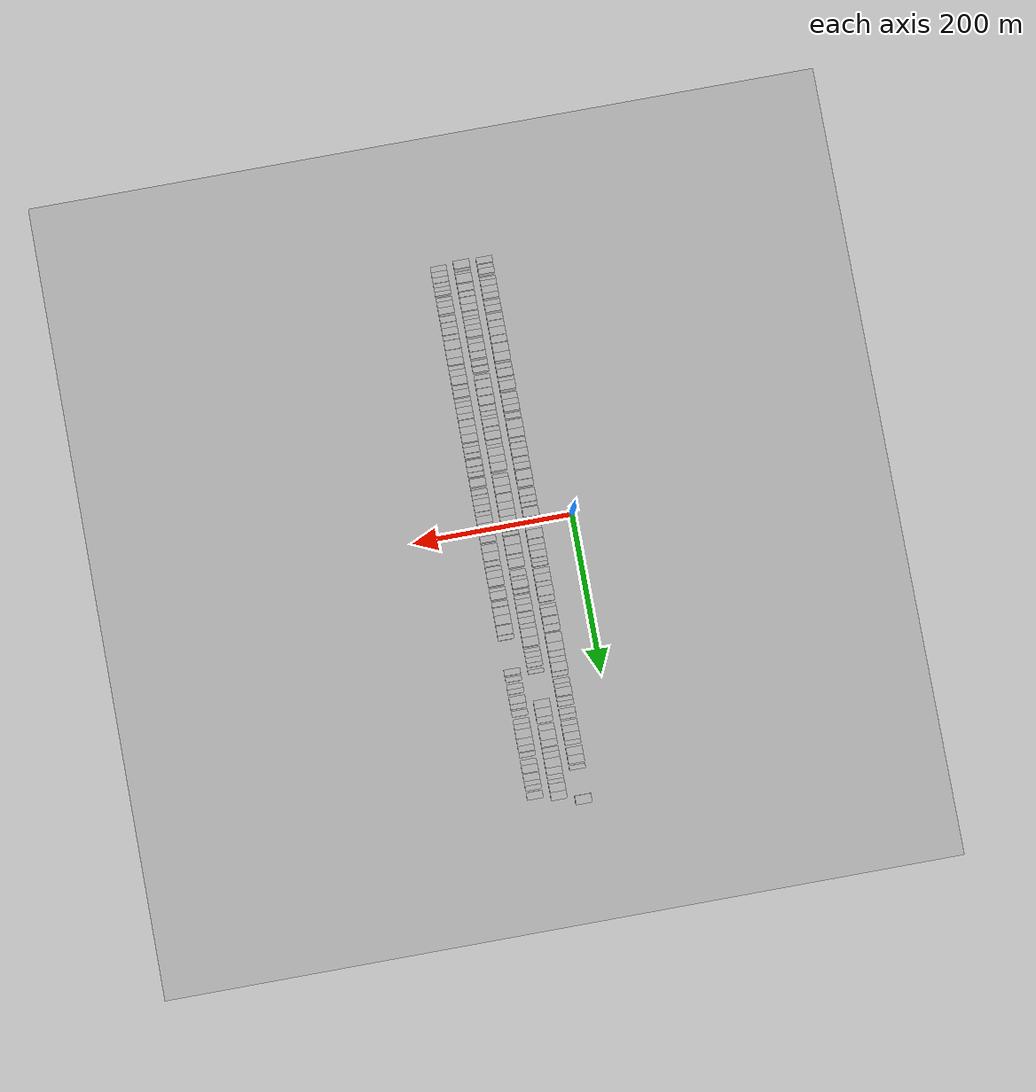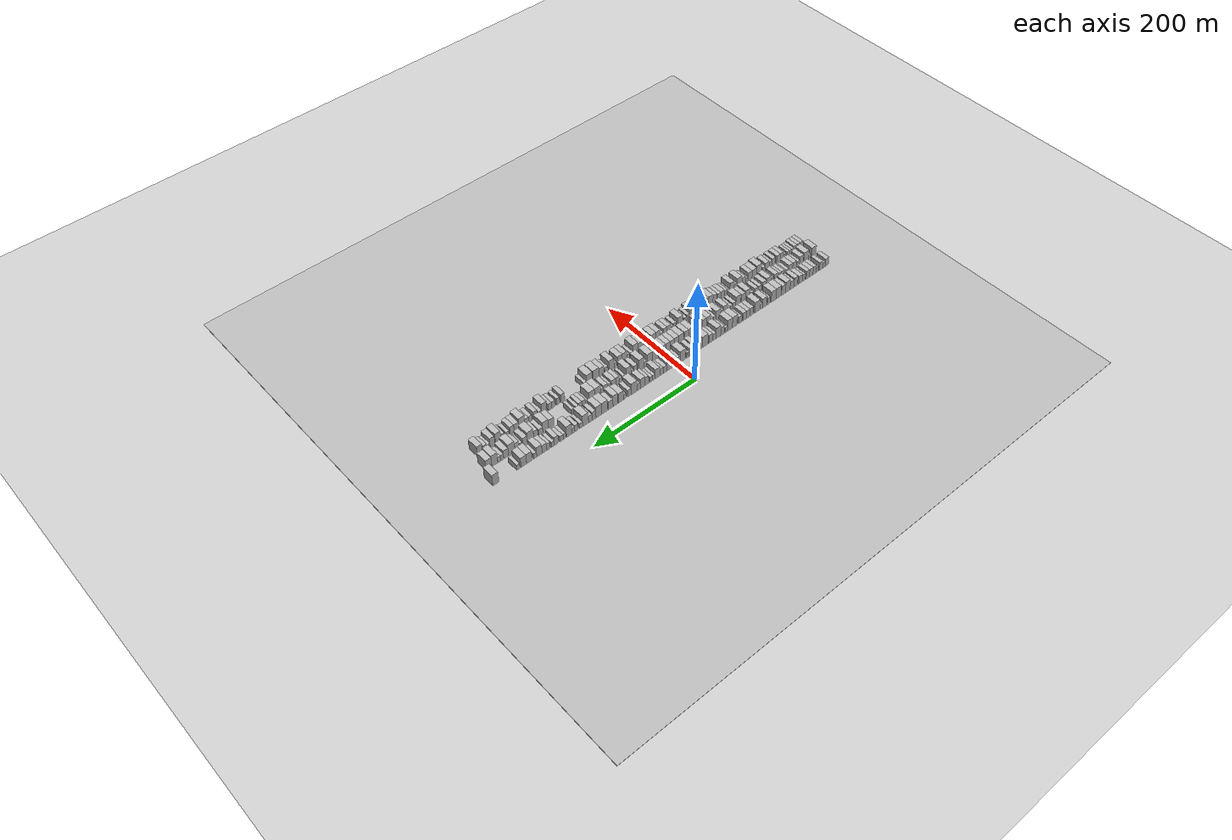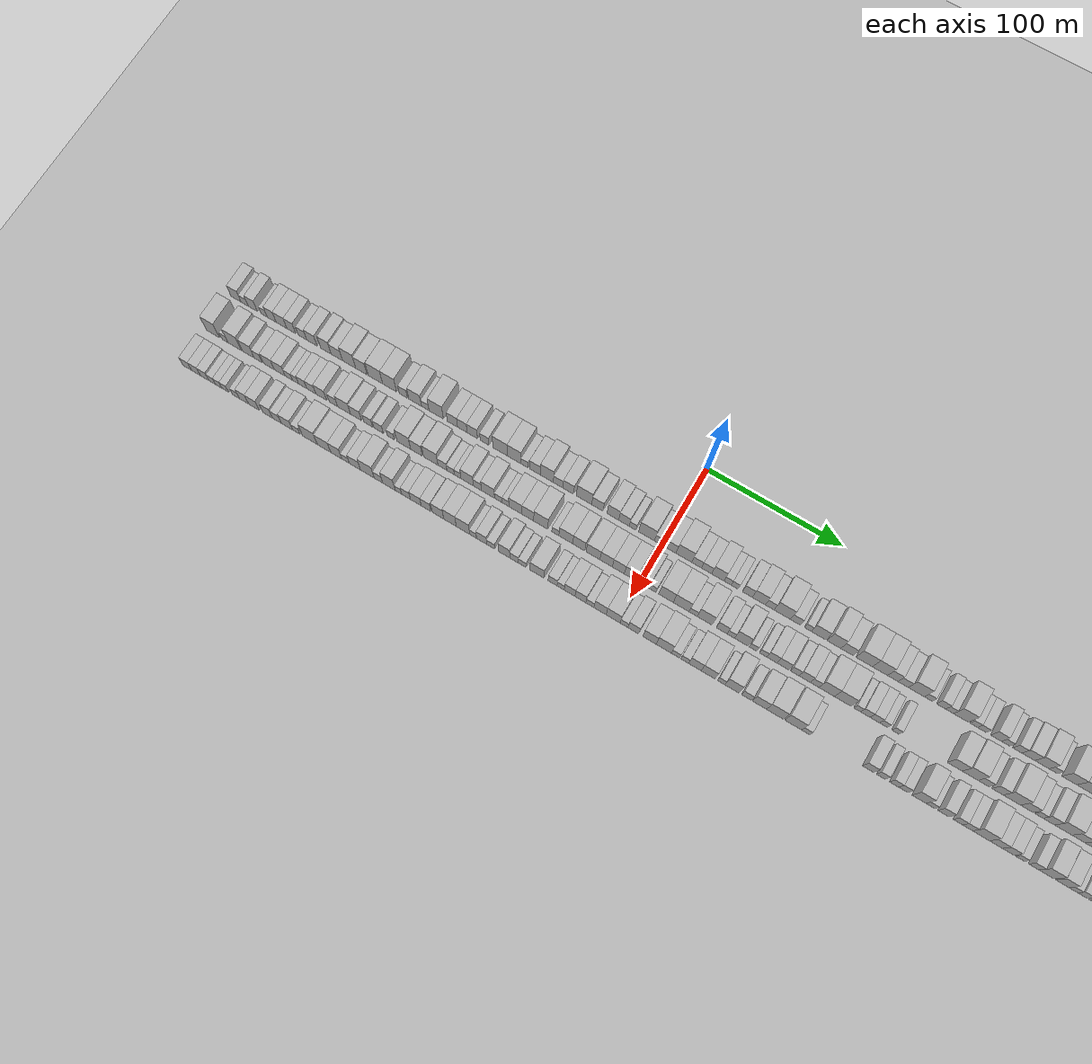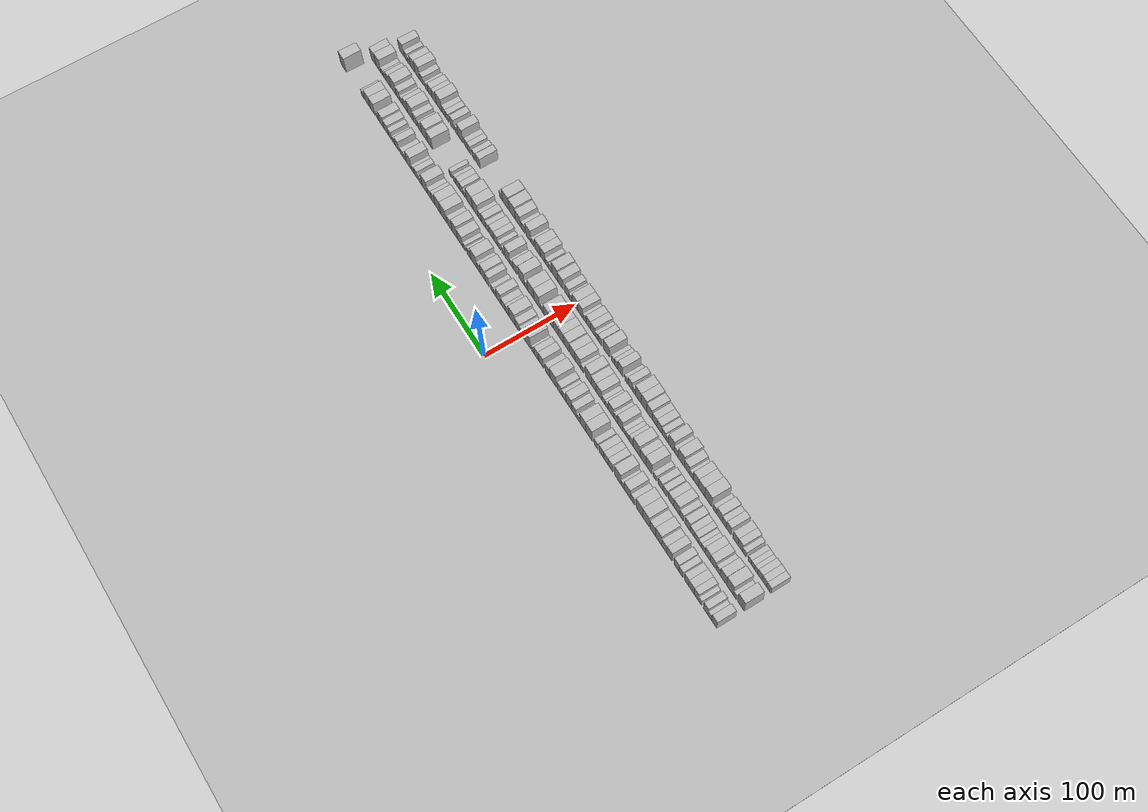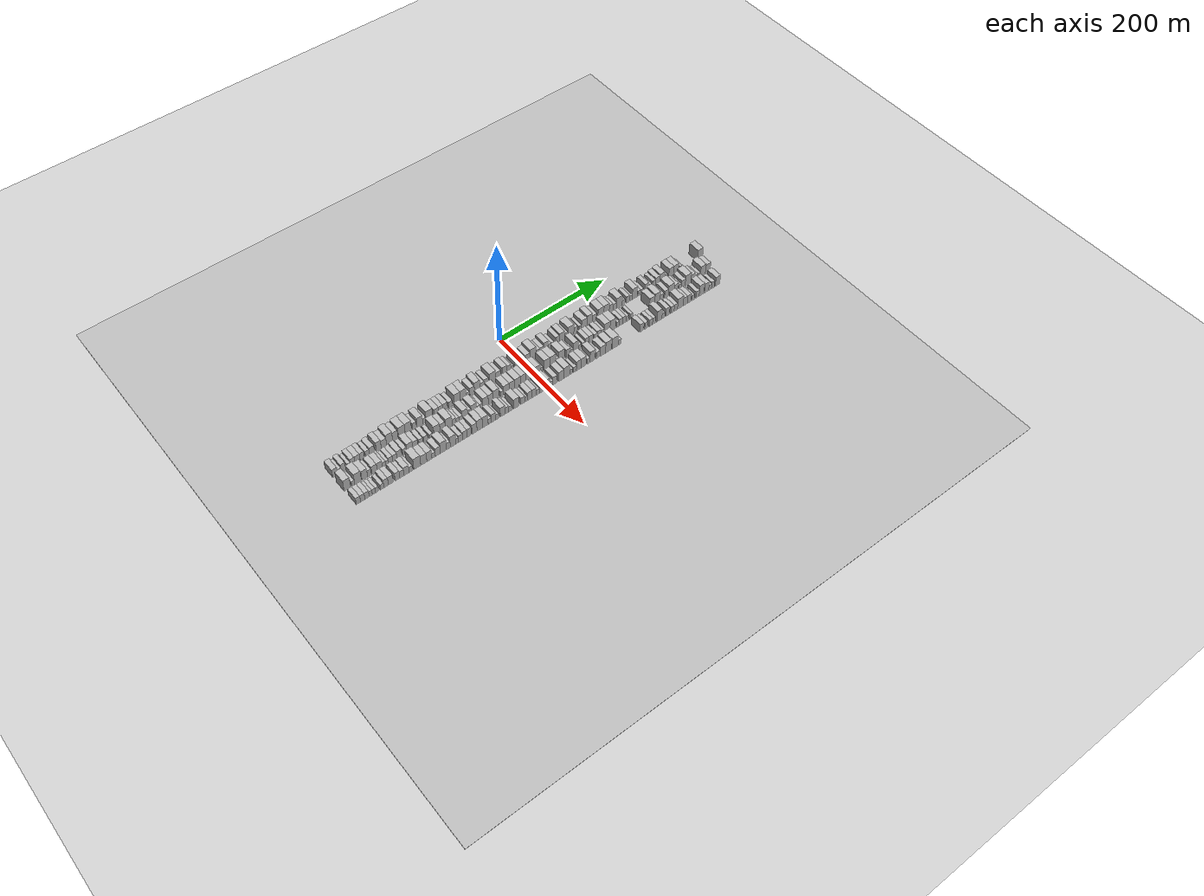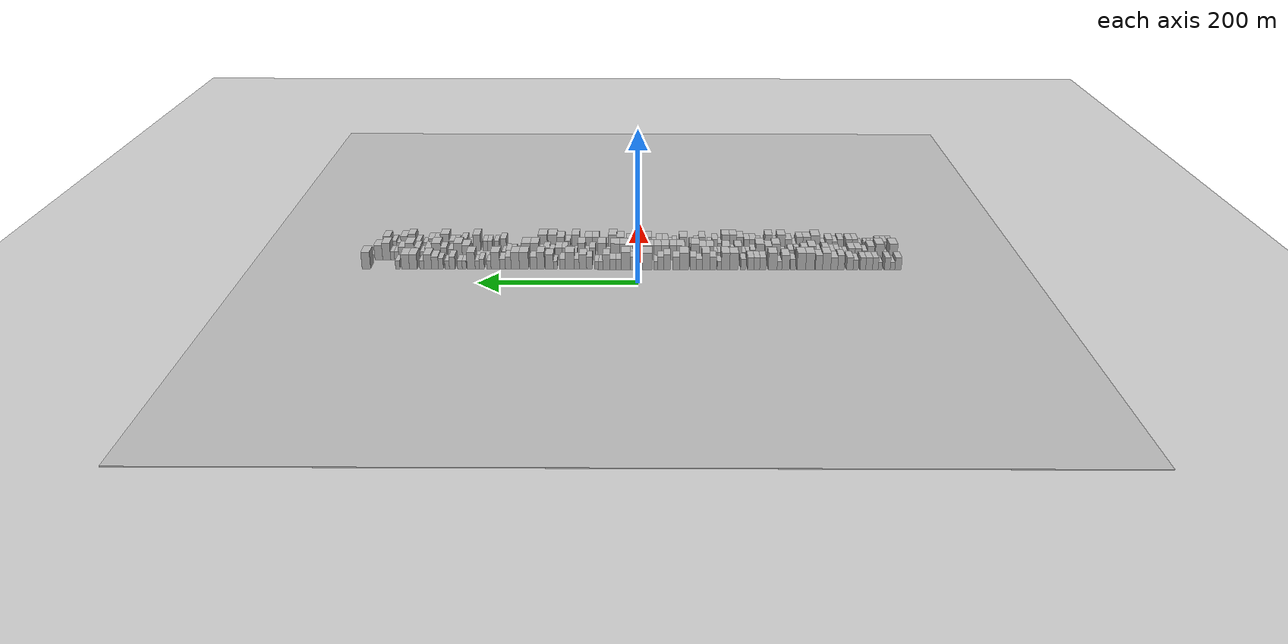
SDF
<?xml version="1.0" encoding="utf-8"?>

<sdf version="1.6">

   <world name="default">

      <gui fullscreen="0">

         <camera name="user_camera">

            <pose>-15 0 4.57585 0 0 0</pose>

            <view_controller>orbit</view_controller>

         </camera>

      </gui>

      <scene>

         <sky>

           <clouds>

             <speed>12</speed>

           </clouds>

         </sky>

         <ambient>0.4 0.4 0.4 1</ambient>

         <background>0.7 0.7 0.7 1</background>

         <shadows>1</shadows>

      </scene>

      <gravity>0 0 -9.8066</gravity>

      <magnetic_field>6e-06 2.3e-05 -4.2e-05</magnetic_field>

      <physics default="0" name="default_physics" type="ode">

         <ode>

            <solver>

               <type>quick</type>

               <iters>10</iters>

               <sor>1.0</sor>

               <use_dynamic_moi_rescaling>0</use_dynamic_moi_rescaling>

            </solver>

            <constraints>

               <cfm>0</cfm>

               <erp>0.2</erp>

               <contact_max_correcting_vel>100</contact_max_correcting_vel>

               <contact_surface_layer>0.001</contact_surface_layer>

            </constraints>

         </ode>

         <max_step_size>0.004</max_step_size>

         <real_time_factor>1</real_time_factor>

         <real_time_update_rate>250</real_time_update_rate>

      </physics>

      <light name="sun" type="directional">

         <cast_shadows>1</cast_shadows>

         <pose>0 0 10 0 0 0</pose>

         <diffuse>0.8 0.8 0.8 1</diffuse>

         <specular>0.2 0.2 0.2 1</specular>

         <attenuation>

            <range>1000</range>

            <constant>0.9</constant>

            <linear>0.01</linear>

            <quadratic>0.001</quadratic>

         </attenuation>

         <direction>-0.5 0.1 -0.9</direction>

      </light>

      <include>

         <name>ground_plane_1</name>

         <uri>model://HANNAS_ground_plane</uri>

         <pose>0 0 0  0 0 0</pose>

      </include>

      <include>

         <name>ground_plane_2</name>

         <uri>model://HANNAS_ground_plane</uri>

         <pose>100 0 0  0 0 0</pose>

      </include>

      <model name="building_1">

         <static>1</static>

         <pose frame="">50.0000 -331.8723 0 0.000000 0.000000 0.000000</pose>

         <link name="link">

            <pose frame="">0 0 9.00 0 0 0</pose>

            <collision name="collision">

               <geometry>

                  <box>

                     <size>20.0000 8.2555 18.0000</size>

                  </box>

               </geometry>

               <max_contacts>10</max_contacts>

               <surface>

                  <contact>

                     <ode/>

                  </contact>

                  <bounce/>

                  <friction>

                     <torsional>

                        <ode/>

                     </torsional>

                     <ode/>

                  </friction>

               </surface>

            </collision>

            <visual name="visual">

               <cast_shadows>0</cast_shadows>

               <geometry>

                  <box>

                     <size>20.0000 8.2555 18.0000</size>

                  </box>

               </geometry>

               <material>

                  <script>

                     <uri>model://HANNAS_wall/materials/scripts</uri>

                     <uri>model://HANNAS_wall/materials/textures</uri>

                     <name>vrc/HANNAS_wall</name>

                  </script>

               </material>

            </visual>

            <self_collide>0</self_collide>

            <enable_wind>0</enable_wind>

            <kinematic>0</kinematic>

         </link>

      </model>

      <model name="building_2">

         <static>1</static>

         <pose frame="">50.0000 -324.7991 0 0.000000 0.000000 0.000000</pose>

         <link name="link">

            <pose frame="">0 0 6.00 0 0 0</pose>

            <collision name="collision">

               <geometry>

                  <box>

                     <size>20.0000 5.8909 12.0000</size>

                  </box>

               </geometry>

               <max_contacts>10</max_contacts>

               <surface>

                  <contact>

                     <ode/>

                  </contact>

                  <bounce/>

                  <friction>

                     <torsional>

                        <ode/>

                     </torsional>

                     <ode/>

                  </friction>

               </surface>

            </collision>

            <visual name="visual">

               <cast_shadows>0</cast_shadows>

               <geometry>

                  <box>

                     <size>20.0000 5.8909 12.0000</size>

                  </box>

               </geometry>

               <material>

                  <script>

                     <uri>model://HANNAS_wall/materials/scripts</uri>

                     <uri>model://HANNAS_wall/materials/textures</uri>

                     <name>vrc/HANNAS_wall</name>

                  </script>

               </material>

            </visual>

            <self_collide>0</self_collide>

            <enable_wind>0</enable_wind>

            <kinematic>0</kinematic>

         </link>

      </model>

      <model name="building_3">

         <static>1</static>

         <pose frame="">50.0000 -318.1477 0 0.000000 0.000000 0.000000</pose>

         <link name="link">

            <pose frame="">0 0 9.00 0 0 0</pose>

            <collision name="collision">

               <geometry>

                  <box>

                     <size>20.0000 7.4118 18.0000</size>

                  </box>

               </geometry>

               <max_contacts>10</max_contacts>

               <surface>

                  <contact>

                     <ode/>

                  </contact>

                  <bounce/>

                  <friction>

                     <torsional>

                        <ode/>

                     </torsional>

                     <ode/>

                  </friction>

               </surface>

            </collision>

            <visual name="visual">

               <cast_shadows>0</cast_shadows>

               <geometry>

                  <box>

                     <size>20.0000 7.4118 18.0000</size>

                  </box>

               </geometry>

               <material>

                  <script>

                     <uri>model://HANNAS_wall/materials/scripts</uri>

                     <uri>model://HANNAS_wall/materials/textures</uri>

                     <name>vrc/HANNAS_wall</name>

                  </script>

               </material>

            </visual>

            <self_collide>0</self_collide>

            <enable_wind>0</enable_wind>

            <kinematic>0</kinematic>

         </link>

      </model>

      <model name="building_4">

         <static>1</static>

         <pose frame="">50.0000 -308.9618 0 0.000000 0.000000 0.000000</pose>

         <link name="link">

            <pose frame="">0 0 6.00 0 0 0</pose>

            <collision name="collision">

               <geometry>

                  <box>

                     <size>20.0000 4.9599 12.0000</size>

                  </box>

               </geometry>

               <max_contacts>10</max_contacts>

               <surface>

                  <contact>

                     <ode/>

                  </contact>

                  <bounce/>

                  <friction>

                     <torsional>

                        <ode/>

                     </torsional>

                     <ode/>

                  </friction>

               </surface>

            </collision>

            <visual name="visual">

               <cast_shadows>0</cast_shadows>

               <geometry>

                  <box>

                     <size>20.0000 4.9599 12.0000</size>

                  </box>

               </geometry>

               <material>

                  <script>

                     <uri>model://HANNAS_wall/materials/scripts</uri>

                     <uri>model://HANNAS_wall/materials/textures</uri>

                     <name>vrc/HANNAS_wall</name>

                  </script>

               </material>

            </visual>

            <self_collide>0</self_collide>

            <enable_wind>0</enable_wind>

            <kinematic>0</kinematic>

         </link>

      </model>

      <model name="building_5">

         <static>1</static>

         <pose frame="">50.0000 -302.8142 0 0.000000 0.000000 0.000000</pose>

         <link name="link">

            <pose frame="">0 0 9.00 0 0 0</pose>

            <collision name="collision">

               <geometry>

                  <box>

                     <size>20.0000 7.3353 18.0000</size>

                  </box>

               </geometry>

               <max_contacts>10</max_contacts>

               <surface>

                  <contact>

                     <ode/>

                  </contact>

                  <bounce/>

                  <friction>

                     <torsional>

                        <ode/>

                     </torsional>

                     <ode/>

                  </friction>

               </surface>

            </collision>

            <visual name="visual">

               <cast_shadows>0</cast_shadows>

               <geometry>

                  <box>

                     <size>20.0000 7.3353 18.0000</size>

                  </box>

               </geometry>

               <material>

                  <script>

                     <uri>model://HANNAS_wall/materials/scripts</uri>

                     <uri>model://HANNAS_wall/materials/textures</uri>

                     <name>vrc/HANNAS_wall</name>

                  </script>

               </material>

            </visual>

            <self_collide>0</self_collide>

            <enable_wind>0</enable_wind>

            <kinematic>0</kinematic>

         </link>

      </model>

      <model name="building_6">

         <static>1</static>

         <pose frame="">50.0000 -294.8184 0 0.000000 0.000000 0.000000</pose>

         <link name="link">

            <pose frame="">0 0 9.00 0 0 0</pose>

            <collision name="collision">

               <geometry>

                  <box>

                     <size>20.0000 8.6562 18.0000</size>

                  </box>

               </geometry>

               <max_contacts>10</max_contacts>

               <surface>

                  <contact>

                     <ode/>

                  </contact>

                  <bounce/>

                  <friction>

                     <torsional>

                        <ode/>

                     </torsional>

                     <ode/>

                  </friction>

               </surface>

            </collision>

            <visual name="visual">

               <cast_shadows>0</cast_shadows>

               <geometry>

                  <box>

                     <size>20.0000 8.6562 18.0000</size>

                  </box>

               </geometry>

               <material>

                  <script>

                     <uri>model://HANNAS_wall/materials/scripts</uri>

                     <uri>model://HANNAS_wall/materials/textures</uri>

                     <name>vrc/HANNAS_wall</name>

                  </script>

               </material>

            </visual>

            <self_collide>0</self_collide>

            <enable_wind>0</enable_wind>

            <kinematic>0</kinematic>

         </link>

      </model>

      <model name="building_7">

         <static>1</static>

         <pose frame="">50.0000 -286.8759 0 0.000000 0.000000 0.000000</pose>

         <link name="link">

            <pose frame="">0 0 9.00 0 0 0</pose>

            <collision name="collision">

               <geometry>

                  <box>

                     <size>20.0000 7.2289 18.0000</size>

                  </box>

               </geometry>

               <max_contacts>10</max_contacts>

               <surface>

                  <contact>

                     <ode/>

                  </contact>

                  <bounce/>

                  <friction>

                     <torsional>

                        <ode/>

                     </torsional>

                     <ode/>

                  </friction>

               </surface>

            </collision>

            <visual name="visual">

               <cast_shadows>0</cast_shadows>

               <geometry>

                  <box>

                     <size>20.0000 7.2289 18.0000</size>

                  </box>

               </geometry>

               <material>

                  <script>

                     <uri>model://HANNAS_wall/materials/scripts</uri>

                     <uri>model://HANNAS_wall/materials/textures</uri>

                     <name>vrc/HANNAS_wall</name>

                  </script>

               </material>

            </visual>

            <self_collide>0</self_collide>

            <enable_wind>0</enable_wind>

            <kinematic>0</kinematic>

         </link>

      </model>

      <model name="building_8">

         <static>1</static>

         <pose frame="">50.0000 -277.8663 0 0.000000 0.000000 0.000000</pose>

         <link name="link">

            <pose frame="">0 0 7.50 0 0 0</pose>

            <collision name="collision">

               <geometry>

                  <box>

                     <size>20.0000 6.7901 15.0000</size>

                  </box>

               </geometry>

               <max_contacts>10</max_contacts>

               <surface>

                  <contact>

                     <ode/>

                  </contact>

                  <bounce/>

                  <friction>

                     <torsional>

                        <ode/>

                     </torsional>

                     <ode/>

                  </friction>

               </surface>

            </collision>

            <visual name="visual">

               <cast_shadows>0</cast_shadows>

               <geometry>

                  <box>

                     <size>20.0000 6.7901 15.0000</size>

                  </box>

               </geometry>

               <material>

                  <script>

                     <uri>model://HANNAS_wall/materials/scripts</uri>

                     <uri>model://HANNAS_wall/materials/textures</uri>

                     <name>vrc/HANNAS_wall</name>

                  </script>

               </material>

            </visual>

            <self_collide>0</self_collide>

            <enable_wind>0</enable_wind>

            <kinematic>0</kinematic>

         </link>

      </model>

      <model name="building_9">

         <static>1</static>

         <pose frame="">50.0000 -270.3307 0 0.000000 0.000000 0.000000</pose>

         <link name="link">

            <pose frame="">0 0 9.00 0 0 0</pose>

            <collision name="collision">

               <geometry>

                  <box>

                     <size>20.0000 8.2811 18.0000</size>

                  </box>

               </geometry>

               <max_contacts>10</max_contacts>

               <surface>

                  <contact>

                     <ode/>

                  </contact>

                  <bounce/>

                  <friction>

                     <torsional>

                        <ode/>

                     </torsional>

                     <ode/>

                  </friction>

               </surface>

            </collision>

            <visual name="visual">

               <cast_shadows>0</cast_shadows>

               <geometry>

                  <box>

                     <size>20.0000 8.2811 18.0000</size>

                  </box>

               </geometry>

               <material>

                  <script>

                     <uri>model://HANNAS_wall/materials/scripts</uri>

                     <uri>model://HANNAS_wall/materials/textures</uri>

                     <name>vrc/HANNAS_wall</name>

                  </script>

               </material>

            </visual>

            <self_collide>0</self_collide>

            <enable_wind>0</enable_wind>

            <kinematic>0</kinematic>

         </link>

      </model>

      <model name="building_10">

         <static>1</static>

         <pose frame="">50.0000 -258.9902 0 0.000000 0.000000 0.000000</pose>

         <link name="link">

            <pose frame="">0 0 10.50 0 0 0</pose>

            <collision name="collision">

               <geometry>

                  <box>

                     <size>20.0000 8.4001 21.0000</size>

                  </box>

               </geometry>

               <max_contacts>10</max_contacts>

               <surface>

                  <contact>

                     <ode/>

                  </contact>

                  <bounce/>

                  <friction>

                     <torsional>

                        <ode/>

                     </torsional>

                     <ode/>

                  </friction>

               </surface>

            </collision>

            <visual name="visual">

               <cast_shadows>0</cast_shadows>

               <geometry>

                  <box>

                     <size>20.0000 8.4001 21.0000</size>

                  </box>

               </geometry>

               <material>

                  <script>

                     <uri>model://HANNAS_wall/materials/scripts</uri>

                     <uri>model://HANNAS_wall/materials/textures</uri>

                     <name>vrc/HANNAS_wall</name>

                  </script>

               </material>

            </visual>

            <self_collide>0</self_collide>

            <enable_wind>0</enable_wind>

            <kinematic>0</kinematic>

         </link>

      </model>

      <model name="building_11">

         <static>1</static>

         <pose frame="">50.0000 -250.2972 0 0.000000 0.000000 0.000000</pose>

         <link name="link">

            <pose frame="">0 0 9.00 0 0 0</pose>

            <collision name="collision">

               <geometry>

                  <box>

                     <size>20.0000 8.9858 18.0000</size>

                  </box>

               </geometry>

               <max_contacts>10</max_contacts>

               <surface>

                  <contact>

                     <ode/>

                  </contact>

                  <bounce/>

                  <friction>

                     <torsional>

                        <ode/>

                     </torsional>

                     <ode/>

                  </friction>

               </surface>

            </collision>

            <visual name="visual">

               <cast_shadows>0</cast_shadows>

               <geometry>

                  <box>

                     <size>20.0000 8.9858 18.0000</size>

                  </box>

               </geometry>

               <material>

                  <script>

                     <uri>model://HANNAS_wall/materials/scripts</uri>

                     <uri>model://HANNAS_wall/materials/textures</uri>

                     <name>vrc/HANNAS_wall</name>

                  </script>

               </material>

            </visual>

            <self_collide>0</self_collide>

            <enable_wind>0</enable_wind>

            <kinematic>0</kinematic>

         </link>

      </model>

      <model name="building_12">

         <static>1</static>

         <pose frame="">50.0000 -240.5236 0 0.000000 0.000000 0.000000</pose>

         <link name="link">

            <pose frame="">0 0 12.00 0 0 0</pose>

            <collision name="collision">

               <geometry>

                  <box>

                     <size>20.0000 10.5614 24.0000</size>

                  </box>

               </geometry>

               <max_contacts>10</max_contacts>

               <surface>

                  <contact>

                     <ode/>

                  </contact>

                  <bounce/>

                  <friction>

                     <torsional>

                        <ode/>

                     </torsional>

                     <ode/>

                  </friction>

               </surface>

            </collision>

            <visual name="visual">

               <cast_shadows>0</cast_shadows>

               <geometry>

                  <box>

                     <size>20.0000 10.5614 24.0000</size>

                  </box>

               </geometry>

               <material>

                  <script>

                     <uri>model://HANNAS_wall/materials/scripts</uri>

                     <uri>model://HANNAS_wall/materials/textures</uri>

                     <name>vrc/HANNAS_wall</name>

                  </script>

               </material>

            </visual>

            <self_collide>0</self_collide>

            <enable_wind>0</enable_wind>

            <kinematic>0</kinematic>

         </link>

      </model>

      <model name="building_13">

         <static>1</static>

         <pose frame="">50.0000 -230.7263 0 0.000000 0.000000 0.000000</pose>

         <link name="link">

            <pose frame="">0 0 10.50 0 0 0</pose>

            <collision name="collision">

               <geometry>

                  <box>

                     <size>20.0000 9.0333 21.0000</size>

                  </box>

               </geometry>

               <max_contacts>10</max_contacts>

               <surface>

                  <contact>

                     <ode/>

                  </contact>

                  <bounce/>

                  <friction>

                     <torsional>

                        <ode/>

                     </torsional>

                     <ode/>

                  </friction>

               </surface>

            </collision>

            <visual name="visual">

               <cast_shadows>0</cast_shadows>

               <geometry>

                  <box>

                     <size>20.0000 9.0333 21.0000</size>

                  </box>

               </geometry>

               <material>

                  <script>

                     <uri>model://HANNAS_wall/materials/scripts</uri>

                     <uri>model://HANNAS_wall/materials/textures</uri>

                     <name>vrc/HANNAS_wall</name>

                  </script>

               </material>

            </visual>

            <self_collide>0</self_collide>

            <enable_wind>0</enable_wind>

            <kinematic>0</kinematic>

         </link>

      </model>

      <model name="building_14">

         <static>1</static>

         <pose frame="">50.0000 -219.5225 0 0.000000 0.000000 0.000000</pose>

         <link name="link">

            <pose frame="">0 0 12.00 0 0 0</pose>

            <collision name="collision">

               <geometry>

                  <box>

                     <size>20.0000 11.3742 24.0000</size>

                  </box>

               </geometry>

               <max_contacts>10</max_contacts>

               <surface>

                  <contact>

                     <ode/>

                  </contact>

                  <bounce/>

                  <friction>

                     <torsional>

                        <ode/>

                     </torsional>

                     <ode/>

                  </friction>

               </surface>

            </collision>

            <visual name="visual">

               <cast_shadows>0</cast_shadows>

               <geometry>

                  <box>

                     <size>20.0000 11.3742 24.0000</size>

                  </box>

               </geometry>

               <material>

                  <script>

                     <uri>model://HANNAS_wall/materials/scripts</uri>

                     <uri>model://HANNAS_wall/materials/textures</uri>

                     <name>vrc/HANNAS_wall</name>

                  </script>

               </material>

            </visual>

            <self_collide>0</self_collide>

            <enable_wind>0</enable_wind>

            <kinematic>0</kinematic>

         </link>

      </model>

      <model name="building_15">

         <static>1</static>

         <pose frame="">50.0000 -208.3464 0 0.000000 0.000000 0.000000</pose>

         <link name="link">

            <pose frame="">0 0 12.00 0 0 0</pose>

            <collision name="collision">

               <geometry>

                  <box>

                     <size>20.0000 10.9780 24.0000</size>

                  </box>

               </geometry>

               <max_contacts>10</max_contacts>

               <surface>

                  <contact>

                     <ode/>

                  </contact>

                  <bounce/>

                  <friction>

                     <torsional>

                        <ode/>

                     </torsional>

                     <ode/>

                  </friction>

               </surface>

            </collision>

            <visual name="visual">

               <cast_shadows>0</cast_shadows>

               <geometry>

                  <box>

                     <size>20.0000 10.9780 24.0000</size>

                  </box>

               </geometry>

               <material>

                  <script>

                     <uri>model://HANNAS_wall/materials/scripts</uri>

                     <uri>model://HANNAS_wall/materials/textures</uri>

                     <name>vrc/HANNAS_wall</name>

                  </script>

               </material>

            </visual>

            <self_collide>0</self_collide>

            <enable_wind>0</enable_wind>

            <kinematic>0</kinematic>

         </link>

      </model>

      <model name="building_16">

         <static>1</static>

         <pose frame="">50.0000 -197.5580 0 0.000000 0.000000 0.000000</pose>

         <link name="link">

            <pose frame="">0 0 7.50 0 0 0</pose>

            <collision name="collision">

               <geometry>

                  <box>

                     <size>20.0000 6.5987 15.0000</size>

                  </box>

               </geometry>

               <max_contacts>10</max_contacts>

               <surface>

                  <contact>

                     <ode/>

                  </contact>

                  <bounce/>

                  <friction>

                     <torsional>

                        <ode/>

                     </torsional>

                     <ode/>

                  </friction>

               </surface>

            </collision>

            <visual name="visual">

               <cast_shadows>0</cast_shadows>

               <geometry>

                  <box>

                     <size>20.0000 6.5987 15.0000</size>

                  </box>

               </geometry>

               <material>

                  <script>

                     <uri>model://HANNAS_wall/materials/scripts</uri>

                     <uri>model://HANNAS_wall/materials/textures</uri>

                     <name>vrc/HANNAS_wall</name>

                  </script>

               </material>

            </visual>

            <self_collide>0</self_collide>

            <enable_wind>0</enable_wind>

            <kinematic>0</kinematic>

         </link>

      </model>

      <model name="building_17">

         <static>1</static>

         <pose frame="">50.0000 -188.2668 0 0.000000 0.000000 0.000000</pose>

         <link name="link">

            <pose frame="">0 0 10.50 0 0 0</pose>

            <collision name="collision">

               <geometry>

                  <box>

                     <size>20.0000 9.9837 21.0000</size>

                  </box>

               </geometry>

               <max_contacts>10</max_contacts>

               <surface>

                  <contact>

                     <ode/>

                  </contact>

                  <bounce/>

                  <friction>

                     <torsional>

                        <ode/>

                     </torsional>

                     <ode/>

                  </friction>

               </surface>

            </collision>

            <visual name="visual">

               <cast_shadows>0</cast_shadows>

               <geometry>

                  <box>

                     <size>20.0000 9.9837 21.0000</size>

                  </box>

               </geometry>

               <material>

                  <script>

                     <uri>model://HANNAS_wall/materials/scripts</uri>

                     <uri>model://HANNAS_wall/materials/textures</uri>

                     <name>vrc/HANNAS_wall</name>

                  </script>

               </material>

            </visual>

            <self_collide>0</self_collide>

            <enable_wind>0</enable_wind>

            <kinematic>0</kinematic>

         </link>

      </model>

      <model name="building_18">

         <static>1</static>

         <pose frame="">50.0000 -180.3005 0 0.000000 0.000000 0.000000</pose>

         <link name="link">

            <pose frame="">0 0 6.00 0 0 0</pose>

            <collision name="collision">

               <geometry>

                  <box>

                     <size>20.0000 5.9488 12.0000</size>

                  </box>

               </geometry>

               <max_contacts>10</max_contacts>

               <surface>

                  <contact>

                     <ode/>

                  </contact>

                  <bounce/>

                  <friction>

                     <torsional>

                        <ode/>

                     </torsional>

                     <ode/>

                  </friction>

               </surface>

            </collision>

            <visual name="visual">

               <cast_shadows>0</cast_shadows>

               <geometry>

                  <box>

                     <size>20.0000 5.9488 12.0000</size>

                  </box>

               </geometry>

               <material>

                  <script>

                     <uri>model://HANNAS_wall/materials/scripts</uri>

                     <uri>model://HANNAS_wall/materials/textures</uri>

                     <name>vrc/HANNAS_wall</name>

                  </script>

               </material>

            </visual>

            <self_collide>0</self_collide>

            <enable_wind>0</enable_wind>

            <kinematic>0</kinematic>

         </link>

      </model>

      <model name="building_19">

         <static>1</static>

         <pose frame="">50.0000 -171.7092 0 0.000000 0.000000 0.000000</pose>

         <link name="link">

            <pose frame="">0 0 12.00 0 0 0</pose>

            <collision name="collision">

               <geometry>

                  <box>

                     <size>20.0000 11.2336 24.0000</size>

                  </box>

               </geometry>

               <max_contacts>10</max_contacts>

               <surface>

                  <contact>

                     <ode/>

                  </contact>

                  <bounce/>

                  <friction>

                     <torsional>

                        <ode/>

                     </torsional>

                     <ode/>

                  </friction>

               </surface>

            </collision>

            <visual name="visual">

               <cast_shadows>0</cast_shadows>

               <geometry>

                  <box>

                     <size>20.0000 11.2336 24.0000</size>

                  </box>

               </geometry>

               <material>

                  <script>

                     <uri>model://HANNAS_wall/materials/scripts</uri>

                     <uri>model://HANNAS_wall/materials/textures</uri>

                     <name>vrc/HANNAS_wall</name>

                  </script>

               </material>

            </visual>

            <self_collide>0</self_collide>

            <enable_wind>0</enable_wind>

            <kinematic>0</kinematic>

         </link>

      </model>

      <model name="building_20">

         <static>1</static>

         <pose frame="">50.0000 -159.1138 0 0.000000 0.000000 0.000000</pose>

         <link name="link">

            <pose frame="">0 0 9.00 0 0 0</pose>

            <collision name="collision">

               <geometry>

                  <box>

                     <size>20.0000 7.9572 18.0000</size>

                  </box>

               </geometry>

               <max_contacts>10</max_contacts>

               <surface>

                  <contact>

                     <ode/>

                  </contact>

                  <bounce/>

                  <friction>

                     <torsional>

                        <ode/>

                     </torsional>

                     <ode/>

                  </friction>

               </surface>

            </collision>

            <visual name="visual">

               <cast_shadows>0</cast_shadows>

               <geometry>

                  <box>

                     <size>20.0000 7.9572 18.0000</size>

                  </box>

               </geometry>

               <material>

                  <script>

                     <uri>model://HANNAS_wall/materials/scripts</uri>

                     <uri>model://HANNAS_wall/materials/textures</uri>

                     <name>vrc/HANNAS_wall</name>

                  </script>

               </material>

            </visual>

            <self_collide>0</self_collide>

            <enable_wind>0</enable_wind>

            <kinematic>0</kinematic>

         </link>

      </model>

      <model name="building_21">

         <static>1</static>

         <pose frame="">50.0000 -151.4212 0 0.000000 0.000000 0.000000</pose>

         <link name="link">

            <pose frame="">0 0 9.00 0 0 0</pose>

            <collision name="collision">

               <geometry>

                  <box>

                     <size>20.0000 7.4280 18.0000</size>

                  </box>

               </geometry>

               <max_contacts>10</max_contacts>

               <surface>

                  <contact>

                     <ode/>

                  </contact>

                  <bounce/>

                  <friction>

                     <torsional>

                        <ode/>

                     </torsional>

                     <ode/>

                  </friction>

               </surface>

            </collision>

            <visual name="visual">

               <cast_shadows>0</cast_shadows>

               <geometry>

                  <box>

                     <size>20.0000 7.4280 18.0000</size>

                  </box>

               </geometry>

               <material>

                  <script>

                     <uri>model://HANNAS_wall/materials/scripts</uri>

                     <uri>model://HANNAS_wall/materials/textures</uri>

                     <name>vrc/HANNAS_wall</name>

                  </script>

               </material>

            </visual>

            <self_collide>0</self_collide>

            <enable_wind>0</enable_wind>

            <kinematic>0</kinematic>

         </link>

      </model>

      <model name="building_22">

         <static>1</static>

         <pose frame="">50.0000 -143.6685 0 0.000000 0.000000 0.000000</pose>

         <link name="link">

            <pose frame="">0 0 9.00 0 0 0</pose>

            <collision name="collision">

               <geometry>

                  <box>

                     <size>20.0000 8.0774 18.0000</size>

                  </box>

               </geometry>

               <max_contacts>10</max_contacts>

               <surface>

                  <contact>

                     <ode/>

                  </contact>

                  <bounce/>

                  <friction>

                     <torsional>

                        <ode/>

                     </torsional>

                     <ode/>

                  </friction>

               </surface>

            </collision>

            <visual name="visual">

               <cast_shadows>0</cast_shadows>

               <geometry>

                  <box>

                     <size>20.0000 8.0774 18.0000</size>

                  </box>

               </geometry>

               <material>

                  <script>

                     <uri>model://HANNAS_wall/materials/scripts</uri>

                     <uri>model://HANNAS_wall/materials/textures</uri>

                     <name>vrc/HANNAS_wall</name>

                  </script>

               </material>

            </visual>

            <self_collide>0</self_collide>

            <enable_wind>0</enable_wind>

            <kinematic>0</kinematic>

         </link>

      </model>

      <model name="building_23">

         <static>1</static>

         <pose frame="">50.0000 -134.2291 0 0.000000 0.000000 0.000000</pose>

         <link name="link">

            <pose frame="">0 0 7.50 0 0 0</pose>

            <collision name="collision">

               <geometry>

                  <box>

                     <size>20.0000 6.8014 15.0000</size>

                  </box>

               </geometry>

               <max_contacts>10</max_contacts>

               <surface>

                  <contact>

                     <ode/>

                  </contact>

                  <bounce/>

                  <friction>

                     <torsional>

                        <ode/>

                     </torsional>

                     <ode/>

                  </friction>

               </surface>

            </collision>

            <visual name="visual">

               <cast_shadows>0</cast_shadows>

               <geometry>

                  <box>

                     <size>20.0000 6.8014 15.0000</size>

                  </box>

               </geometry>

               <material>

                  <script>

                     <uri>model://HANNAS_wall/materials/scripts</uri>

                     <uri>model://HANNAS_wall/materials/textures</uri>

                     <name>vrc/HANNAS_wall</name>

                  </script>

               </material>

            </visual>

            <self_collide>0</self_collide>

            <enable_wind>0</enable_wind>

            <kinematic>0</kinematic>

         </link>

      </model>

      <model name="building_24">

         <static>1</static>

         <pose frame="">50.0000 -122.2531 0 0.000000 0.000000 0.000000</pose>

         <link name="link">

            <pose frame="">0 0 12.00 0 0 0</pose>

            <collision name="collision">

               <geometry>

                  <box>

                     <size>20.0000 11.1506 24.0000</size>

                  </box>

               </geometry>

               <max_contacts>10</max_contacts>

               <surface>

                  <contact>

                     <ode/>

                  </contact>

                  <bounce/>

                  <friction>

                     <torsional>

                        <ode/>

                     </torsional>

                     <ode/>

                  </friction>

               </surface>

            </collision>

            <visual name="visual">

               <cast_shadows>0</cast_shadows>

               <geometry>

                  <box>

                     <size>20.0000 11.1506 24.0000</size>

                  </box>

               </geometry>

               <material>

                  <script>

                     <uri>model://HANNAS_wall/materials/scripts</uri>

                     <uri>model://HANNAS_wall/materials/textures</uri>

                     <name>vrc/HANNAS_wall</name>

                  </script>

               </material>

            </visual>

            <self_collide>0</self_collide>

            <enable_wind>0</enable_wind>

            <kinematic>0</kinematic>

         </link>

      </model>

      <model name="building_25">

         <static>1</static>

         <pose frame="">50.0000 -111.4234 0 0.000000 0.000000 0.000000</pose>

         <link name="link">

            <pose frame="">0 0 12.00 0 0 0</pose>

            <collision name="collision">

               <geometry>

                  <box>

                     <size>20.0000 10.5088 24.0000</size>

                  </box>

               </geometry>

               <max_contacts>10</max_contacts>

               <surface>

                  <contact>

                     <ode/>

                  </contact>

                  <bounce/>

                  <friction>

                     <torsional>

                        <ode/>

                     </torsional>

                     <ode/>

                  </friction>

               </surface>

            </collision>

            <visual name="visual">

               <cast_shadows>0</cast_shadows>

               <geometry>

                  <box>

                     <size>20.0000 10.5088 24.0000</size>

                  </box>

               </geometry>

               <material>

                  <script>

                     <uri>model://HANNAS_wall/materials/scripts</uri>

                     <uri>model://HANNAS_wall/materials/textures</uri>

                     <name>vrc/HANNAS_wall</name>

                  </script>

               </material>

            </visual>

            <self_collide>0</self_collide>

            <enable_wind>0</enable_wind>

            <kinematic>0</kinematic>

         </link>

      </model>

      <model name="building_26">

         <static>1</static>

         <pose frame="">50.0000 -103.4471 0 0.000000 0.000000 0.000000</pose>

         <link name="link">

            <pose frame="">0 0 6.00 0 0 0</pose>

            <collision name="collision">

               <geometry>

                  <box>

                     <size>20.0000 5.4438 12.0000</size>

                  </box>

               </geometry>

               <max_contacts>10</max_contacts>

               <surface>

                  <contact>

                     <ode/>

                  </contact>

                  <bounce/>

                  <friction>

                     <torsional>

                        <ode/>

                     </torsional>

                     <ode/>

                  </friction>

               </surface>

            </collision>

            <visual name="visual">

               <cast_shadows>0</cast_shadows>

               <geometry>

                  <box>

                     <size>20.0000 5.4438 12.0000</size>

                  </box>

               </geometry>

               <material>

                  <script>

                     <uri>model://HANNAS_wall/materials/scripts</uri>

                     <uri>model://HANNAS_wall/materials/textures</uri>

                     <name>vrc/HANNAS_wall</name>

                  </script>

               </material>

            </visual>

            <self_collide>0</self_collide>

            <enable_wind>0</enable_wind>

            <kinematic>0</kinematic>

         </link>

      </model>

      <model name="building_27">

         <static>1</static>

         <pose frame="">50.0000 -95.6076 0 0.000000 0.000000 0.000000</pose>

         <link name="link">

            <pose frame="">0 0 9.00 0 0 0</pose>

            <collision name="collision">

               <geometry>

                  <box>

                     <size>20.0000 8.2350 18.0000</size>

                  </box>

               </geometry>

               <max_contacts>10</max_contacts>

               <surface>

                  <contact>

                     <ode/>

                  </contact>

                  <bounce/>

                  <friction>

                     <torsional>

                        <ode/>

                     </torsional>

                     <ode/>

                  </friction>

               </surface>

            </collision>

            <visual name="visual">

               <cast_shadows>0</cast_shadows>

               <geometry>

                  <box>

                     <size>20.0000 8.2350 18.0000</size>

                  </box>

               </geometry>

               <material>

                  <script>

                     <uri>model://HANNAS_wall/materials/scripts</uri>

                     <uri>model://HANNAS_wall/materials/textures</uri>

                     <name>vrc/HANNAS_wall</name>

                  </script>

               </material>

            </visual>

            <self_collide>0</self_collide>

            <enable_wind>0</enable_wind>

            <kinematic>0</kinematic>

         </link>

      </model>

      <model name="building_28">

         <static>1</static>

         <pose frame="">50.0000 -86.5173 0 0.000000 0.000000 0.000000</pose>

         <link name="link">

            <pose frame="">0 0 12.00 0 0 0</pose>

            <collision name="collision">

               <geometry>

                  <box>

                     <size>20.0000 9.9456 24.0000</size>

                  </box>

               </geometry>

               <max_contacts>10</max_contacts>

               <surface>

                  <contact>

                     <ode/>

                  </contact>

                  <bounce/>

                  <friction>

                     <torsional>

                        <ode/>

                     </torsional>

                     <ode/>

                  </friction>

               </surface>

            </collision>

            <visual name="visual">

               <cast_shadows>0</cast_shadows>

               <geometry>

                  <box>

                     <size>20.0000 9.9456 24.0000</size>

                  </box>

               </geometry>

               <material>

                  <script>

                     <uri>model://HANNAS_wall/materials/scripts</uri>

                     <uri>model://HANNAS_wall/materials/textures</uri>

                     <name>vrc/HANNAS_wall</name>

                  </script>

               </material>

            </visual>

            <self_collide>0</self_collide>

            <enable_wind>0</enable_wind>

            <kinematic>0</kinematic>

         </link>

      </model>

      <model name="building_29">

         <static>1</static>

         <pose frame="">50.0000 -77.8846 0 0.000000 0.000000 0.000000</pose>

         <link name="link">

            <pose frame="">0 0 7.50 0 0 0</pose>

            <collision name="collision">

               <geometry>

                  <box>

                     <size>20.0000 7.3198 15.0000</size>

                  </box>

               </geometry>

               <max_contacts>10</max_contacts>

               <surface>

                  <contact>

                     <ode/>

                  </contact>

                  <bounce/>

                  <friction>

                     <torsional>

                        <ode/>

                     </torsional>

                     <ode/>

                  </friction>

               </surface>

            </collision>

            <visual name="visual">

               <cast_shadows>0</cast_shadows>

               <geometry>

                  <box>

                     <size>20.0000 7.3198 15.0000</size>

                  </box>

               </geometry>

               <material>

                  <script>

                     <uri>model://HANNAS_wall/materials/scripts</uri>

                     <uri>model://HANNAS_wall/materials/textures</uri>

                     <name>vrc/HANNAS_wall</name>

                  </script>

               </material>

            </visual>

            <self_collide>0</self_collide>

            <enable_wind>0</enable_wind>

            <kinematic>0</kinematic>

         </link>

      </model>

      <model name="building_30">

         <static>1</static>

         <pose frame="">50.0000 -70.1955 0 0.000000 0.000000 0.000000</pose>

         <link name="link">

            <pose frame="">0 0 9.00 0 0 0</pose>

            <collision name="collision">

               <geometry>

                  <box>

                     <size>20.0000 8.0583 18.0000</size>

                  </box>

               </geometry>

               <max_contacts>10</max_contacts>

               <surface>

                  <contact>

                     <ode/>

                  </contact>

                  <bounce/>

                  <friction>

                     <torsional>

                        <ode/>

                     </torsional>

                     <ode/>

                  </friction>

               </surface>

            </collision>

            <visual name="visual">

               <cast_shadows>0</cast_shadows>

               <geometry>

                  <box>

                     <size>20.0000 8.0583 18.0000</size>

                  </box>

               </geometry>

               <material>

                  <script>

                     <uri>model://HANNAS_wall/materials/scripts</uri>

                     <uri>model://HANNAS_wall/materials/textures</uri>

                     <name>vrc/HANNAS_wall</name>

                  </script>

               </material>

            </visual>

            <self_collide>0</self_collide>

            <enable_wind>0</enable_wind>

            <kinematic>0</kinematic>

         </link>

      </model>

      <model name="building_31">

         <static>1</static>

         <pose frame="">50.0000 -58.3696 0 0.000000 0.000000 0.000000</pose>

         <link name="link">

            <pose frame="">0 0 12.00 0 0 0</pose>

            <collision name="collision">

               <geometry>

                  <box>

                     <size>20.0000 11.5935 24.0000</size>

                  </box>

               </geometry>

               <max_contacts>10</max_contacts>

               <surface>

                  <contact>

                     <ode/>

                  </contact>

                  <bounce/>

                  <friction>

                     <torsional>

                        <ode/>

                     </torsional>

                     <ode/>

                  </friction>

               </surface>

            </collision>

            <visual name="visual">

               <cast_shadows>0</cast_shadows>

               <geometry>

                  <box>

                     <size>20.0000 11.5935 24.0000</size>

                  </box>

               </geometry>

               <material>

                  <script>

                     <uri>model://HANNAS_wall/materials/scripts</uri>

                     <uri>model://HANNAS_wall/materials/textures</uri>

                     <name>vrc/HANNAS_wall</name>

                  </script>

               </material>

            </visual>

            <self_collide>0</self_collide>

            <enable_wind>0</enable_wind>

            <kinematic>0</kinematic>

         </link>

      </model>

      <model name="building_32">

         <static>1</static>

         <pose frame="">50.0000 -48.3083 0 0.000000 0.000000 0.000000</pose>

         <link name="link">

            <pose frame="">0 0 9.00 0 0 0</pose>

            <collision name="collision">

               <geometry>

                  <box>

                     <size>20.0000 8.5291 18.0000</size>

                  </box>

               </geometry>

               <max_contacts>10</max_contacts>

               <surface>

                  <contact>

                     <ode/>

                  </contact>

                  <bounce/>

                  <friction>

                     <torsional>

                        <ode/>

                     </torsional>

                     <ode/>

                  </friction>

               </surface>

            </collision>

            <visual name="visual">

               <cast_shadows>0</cast_shadows>

               <geometry>

                  <box>

                     <size>20.0000 8.5291 18.0000</size>

                  </box>

               </geometry>

               <material>

                  <script>

                     <uri>model://HANNAS_wall/materials/scripts</uri>

                     <uri>model://HANNAS_wall/materials/textures</uri>

                     <name>vrc/HANNAS_wall</name>

                  </script>

               </material>

            </visual>

            <self_collide>0</self_collide>

            <enable_wind>0</enable_wind>

            <kinematic>0</kinematic>

         </link>

      </model>

      <model name="building_33">

         <static>1</static>

         <pose frame="">50.0000 -36.6462 0 0.000000 0.000000 0.000000</pose>

         <link name="link">

            <pose frame="">0 0 10.50 0 0 0</pose>

            <collision name="collision">

               <geometry>

                  <box>

                     <size>20.0000 8.7952 21.0000</size>

                  </box>

               </geometry>

               <max_contacts>10</max_contacts>

               <surface>

                  <contact>

                     <ode/>

                  </contact>

                  <bounce/>

                  <friction>

                     <torsional>

                        <ode/>

                     </torsional>

                     <ode/>

                  </friction>

               </surface>

            </collision>

            <visual name="visual">

               <cast_shadows>0</cast_shadows>

               <geometry>

                  <box>

                     <size>20.0000 8.7952 21.0000</size>

                  </box>

               </geometry>

               <material>

                  <script>

                     <uri>model://HANNAS_wall/materials/scripts</uri>

                     <uri>model://HANNAS_wall/materials/textures</uri>

                     <name>vrc/HANNAS_wall</name>

                  </script>

               </material>

            </visual>

            <self_collide>0</self_collide>

            <enable_wind>0</enable_wind>

            <kinematic>0</kinematic>

         </link>

      </model>

      <model name="building_34">

         <static>1</static>

         <pose frame="">50.0000 -28.3335 0 0.000000 0.000000 0.000000</pose>

         <link name="link">

            <pose frame="">0 0 9.00 0 0 0</pose>

            <collision name="collision">

               <geometry>

                  <box>

                     <size>20.0000 7.8303 18.0000</size>

                  </box>

               </geometry>

               <max_contacts>10</max_contacts>

               <surface>

                  <contact>

                     <ode/>

                  </contact>

                  <bounce/>

                  <friction>

                     <torsional>

                        <ode/>

                     </torsional>

                     <ode/>

                  </friction>

               </surface>

            </collision>

            <visual name="visual">

               <cast_shadows>0</cast_shadows>

               <geometry>

                  <box>

                     <size>20.0000 7.8303 18.0000</size>

                  </box>

               </geometry>

               <material>

                  <script>

                     <uri>model://HANNAS_wall/materials/scripts</uri>

                     <uri>model://HANNAS_wall/materials/textures</uri>

                     <name>vrc/HANNAS_wall</name>

                  </script>

               </material>

            </visual>

            <self_collide>0</self_collide>

            <enable_wind>0</enable_wind>

            <kinematic>0</kinematic>

         </link>

      </model>

      <model name="building_35">

         <static>1</static>

         <pose frame="">50.0000 -21.9060 0 0.000000 0.000000 0.000000</pose>

         <link name="link">

            <pose frame="">0 0 6.00 0 0 0</pose>

            <collision name="collision">

               <geometry>

                  <box>

                     <size>20.0000 5.0245 12.0000</size>

                  </box>

               </geometry>

               <max_contacts>10</max_contacts>

               <surface>

                  <contact>

                     <ode/>

                  </contact>

                  <bounce/>

                  <friction>

                     <torsional>

                        <ode/>

                     </torsional>

                     <ode/>

                  </friction>

               </surface>

            </collision>

            <visual name="visual">

               <cast_shadows>0</cast_shadows>

               <geometry>

                  <box>

                     <size>20.0000 5.0245 12.0000</size>

                  </box>

               </geometry>

               <material>

                  <script>

                     <uri>model://HANNAS_wall/materials/scripts</uri>

                     <uri>model://HANNAS_wall/materials/textures</uri>

                     <name>vrc/HANNAS_wall</name>

                  </script>

               </material>

            </visual>

            <self_collide>0</self_collide>

            <enable_wind>0</enable_wind>

            <kinematic>0</kinematic>

         </link>

      </model>

      <model name="building_36">

         <static>1</static>

         <pose frame="">50.0000 -11.4566 0 0.000000 0.000000 0.000000</pose>

         <link name="link">

            <pose frame="">0 0 12.00 0 0 0</pose>

            <collision name="collision">

               <geometry>

                  <box>

                     <size>20.0000 11.8743 24.0000</size>

                  </box>

               </geometry>

               <max_contacts>10</max_contacts>

               <surface>

                  <contact>

                     <ode/>

                  </contact>

                  <bounce/>

                  <friction>

                     <torsional>

                        <ode/>

                     </torsional>

                     <ode/>

                  </friction>

               </surface>

            </collision>

            <visual name="visual">

               <cast_shadows>0</cast_shadows>

               <geometry>

                  <box>

                     <size>20.0000 11.8743 24.0000</size>

                  </box>

               </geometry>

               <material>

                  <script>

                     <uri>model://HANNAS_wall/materials/scripts</uri>

                     <uri>model://HANNAS_wall/materials/textures</uri>

                     <name>vrc/HANNAS_wall</name>

                  </script>

               </material>

            </visual>

            <self_collide>0</self_collide>

            <enable_wind>0</enable_wind>

            <kinematic>0</kinematic>

         </link>

      </model>

      <model name="building_37">

         <static>1</static>

         <pose frame="">50.0000 -1.7803 0 0.000000 0.000000 0.000000</pose>

         <link name="link">

            <pose frame="">0 0 7.50 0 0 0</pose>

            <collision name="collision">

               <geometry>

                  <box>

                     <size>20.0000 7.4783 15.0000</size>

                  </box>

               </geometry>

               <max_contacts>10</max_contacts>

               <surface>

                  <contact>

                     <ode/>

                  </contact>

                  <bounce/>

                  <friction>

                     <torsional>

                        <ode/>

                     </torsional>

                     <ode/>

                  </friction>

               </surface>

            </collision>

            <visual name="visual">

               <cast_shadows>0</cast_shadows>

               <geometry>

                  <box>

                     <size>20.0000 7.4783 15.0000</size>

                  </box>

               </geometry>

               <material>

                  <script>

                     <uri>model://HANNAS_wall/materials/scripts</uri>

                     <uri>model://HANNAS_wall/materials/textures</uri>

                     <name>vrc/HANNAS_wall</name>

                  </script>

               </material>

            </visual>

            <self_collide>0</self_collide>

            <enable_wind>0</enable_wind>

            <kinematic>0</kinematic>

         </link>

      </model>

      <model name="building_38">

         <static>1</static>

         <pose frame="">50.0000 6.1895 0 0.000000 0.000000 0.000000</pose>

         <link name="link">

            <pose frame="">0 0 9.00 0 0 0</pose>

            <collision name="collision">

               <geometry>

                  <box>

                     <size>20.0000 8.4613 18.0000</size>

                  </box>

               </geometry>

               <max_contacts>10</max_contacts>

               <surface>

                  <contact>

                     <ode/>

                  </contact>

                  <bounce/>

                  <friction>

                     <torsional>

                        <ode/>

                     </torsional>

                     <ode/>

                  </friction>

               </surface>

            </collision>

            <visual name="visual">

               <cast_shadows>0</cast_shadows>

               <geometry>

                  <box>

                     <size>20.0000 8.4613 18.0000</size>

                  </box>

               </geometry>

               <material>

                  <script>

                     <uri>model://HANNAS_wall/materials/scripts</uri>

                     <uri>model://HANNAS_wall/materials/textures</uri>

                     <name>vrc/HANNAS_wall</name>

                  </script>

               </material>

            </visual>

            <self_collide>0</self_collide>

            <enable_wind>0</enable_wind>

            <kinematic>0</kinematic>

         </link>

      </model>

      <model name="building_39">

         <static>1</static>

         <pose frame="">50.0000 16.2375 0 0.000000 0.000000 0.000000</pose>

         <link name="link">

            <pose frame="">0 0 12.00 0 0 0</pose>

            <collision name="collision">

               <geometry>

                  <box>

                     <size>20.0000 11.6348 24.0000</size>

                  </box>

               </geometry>

               <max_contacts>10</max_contacts>

               <surface>

                  <contact>

                     <ode/>

                  </contact>

                  <bounce/>

                  <friction>

                     <torsional>

                        <ode/>

                     </torsional>

                     <ode/>

                  </friction>

               </surface>

            </collision>

            <visual name="visual">

               <cast_shadows>0</cast_shadows>

               <geometry>

                  <box>

                     <size>20.0000 11.6348 24.0000</size>

                  </box>

               </geometry>

               <material>

                  <script>

                     <uri>model://HANNAS_wall/materials/scripts</uri>

                     <uri>model://HANNAS_wall/materials/textures</uri>

                     <name>vrc/HANNAS_wall</name>

                  </script>

               </material>

            </visual>

            <self_collide>0</self_collide>

            <enable_wind>0</enable_wind>

            <kinematic>0</kinematic>

         </link>

      </model>

      <model name="building_40">

         <static>1</static>

         <pose frame="">50.0000 25.6012 0 0.000000 0.000000 0.000000</pose>

         <link name="link">

            <pose frame="">0 0 7.50 0 0 0</pose>

            <collision name="collision">

               <geometry>

                  <box>

                     <size>20.0000 7.0926 15.0000</size>

                  </box>

               </geometry>

               <max_contacts>10</max_contacts>

               <surface>

                  <contact>

                     <ode/>

                  </contact>

                  <bounce/>

                  <friction>

                     <torsional>

                        <ode/>

                     </torsional>

                     <ode/>

                  </friction>

               </surface>

            </collision>

            <visual name="visual">

               <cast_shadows>0</cast_shadows>

               <geometry>

                  <box>

                     <size>20.0000 7.0926 15.0000</size>

                  </box>

               </geometry>

               <material>

                  <script>

                     <uri>model://HANNAS_wall/materials/scripts</uri>

                     <uri>model://HANNAS_wall/materials/textures</uri>

                     <name>vrc/HANNAS_wall</name>

                  </script>

               </material>

            </visual>

            <self_collide>0</self_collide>

            <enable_wind>0</enable_wind>

            <kinematic>0</kinematic>

         </link>

      </model>

      <model name="building_41">

         <static>1</static>

         <pose frame="">50.0000 32.8756 0 0.000000 0.000000 0.000000</pose>

         <link name="link">

            <pose frame="">0 0 7.50 0 0 0</pose>

            <collision name="collision">

               <geometry>

                  <box>

                     <size>20.0000 7.4560 15.0000</size>

                  </box>

               </geometry>

               <max_contacts>10</max_contacts>

               <surface>

                  <contact>

                     <ode/>

                  </contact>

                  <bounce/>

                  <friction>

                     <torsional>

                        <ode/>

                     </torsional>

                     <ode/>

                  </friction>

               </surface>

            </collision>

            <visual name="visual">

               <cast_shadows>0</cast_shadows>

               <geometry>

                  <box>

                     <size>20.0000 7.4560 15.0000</size>

                  </box>

               </geometry>

               <material>

                  <script>

                     <uri>model://HANNAS_wall/materials/scripts</uri>

                     <uri>model://HANNAS_wall/materials/textures</uri>

                     <name>vrc/HANNAS_wall</name>

                  </script>

               </material>

            </visual>

            <self_collide>0</self_collide>

            <enable_wind>0</enable_wind>

            <kinematic>0</kinematic>

         </link>

      </model>

      <model name="building_42">

         <static>1</static>

         <pose frame="">50.0000 41.1588 0 0.000000 0.000000 0.000000</pose>

         <link name="link">

            <pose frame="">0 0 10.50 0 0 0</pose>

            <collision name="collision">

               <geometry>

                  <box>

                     <size>20.0000 9.1105 21.0000</size>

                  </box>

               </geometry>

               <max_contacts>10</max_contacts>

               <surface>

                  <contact>

                     <ode/>

                  </contact>

                  <bounce/>

                  <friction>

                     <torsional>

                        <ode/>

                     </torsional>

                     <ode/>

                  </friction>

               </surface>

            </collision>

            <visual name="visual">

               <cast_shadows>0</cast_shadows>

               <geometry>

                  <box>

                     <size>20.0000 9.1105 21.0000</size>

                  </box>

               </geometry>

               <material>

                  <script>

                     <uri>model://HANNAS_wall/materials/scripts</uri>

                     <uri>model://HANNAS_wall/materials/textures</uri>

                     <name>vrc/HANNAS_wall</name>

                  </script>

               </material>

            </visual>

            <self_collide>0</self_collide>

            <enable_wind>0</enable_wind>

            <kinematic>0</kinematic>

         </link>

      </model>

      <model name="building_43">

         <static>1</static>

         <pose frame="">50.0000 48.3113 0 0.000000 0.000000 0.000000</pose>

         <link name="link">

            <pose frame="">0 0 6.00 0 0 0</pose>

            <collision name="collision">

               <geometry>

                  <box>

                     <size>20.0000 5.1945 12.0000</size>

                  </box>

               </geometry>

               <max_contacts>10</max_contacts>

               <surface>

                  <contact>

                     <ode/>

                  </contact>

                  <bounce/>

                  <friction>

                     <torsional>

                        <ode/>

                     </torsional>

                     <ode/>

                  </friction>

               </surface>

            </collision>

            <visual name="visual">

               <cast_shadows>0</cast_shadows>

               <geometry>

                  <box>

                     <size>20.0000 5.1945 12.0000</size>

                  </box>

               </geometry>

               <material>

                  <script>

                     <uri>model://HANNAS_wall/materials/scripts</uri>

                     <uri>model://HANNAS_wall/materials/textures</uri>

                     <name>vrc/HANNAS_wall</name>

                  </script>

               </material>

            </visual>

            <self_collide>0</self_collide>

            <enable_wind>0</enable_wind>

            <kinematic>0</kinematic>

         </link>

      </model>

      <model name="building_44">

         <static>1</static>

         <pose frame="">50.0000 53.4789 0 0.000000 0.000000 0.000000</pose>

         <link name="link">

            <pose frame="">0 0 6.00 0 0 0</pose>

            <collision name="collision">

               <geometry>

                  <box>

                     <size>20.0000 5.1407 12.0000</size>

                  </box>

               </geometry>

               <max_contacts>10</max_contacts>

               <surface>

                  <contact>

                     <ode/>

                  </contact>

                  <bounce/>

                  <friction>

                     <torsional>

                        <ode/>

                     </torsional>

                     <ode/>

                  </friction>

               </surface>

            </collision>

            <visual name="visual">

               <cast_shadows>0</cast_shadows>

               <geometry>

                  <box>

                     <size>20.0000 5.1407 12.0000</size>

                  </box>

               </geometry>

               <material>

                  <script>

                     <uri>model://HANNAS_wall/materials/scripts</uri>

                     <uri>model://HANNAS_wall/materials/textures</uri>

                     <name>vrc/HANNAS_wall</name>

                  </script>

               </material>

            </visual>

            <self_collide>0</self_collide>

            <enable_wind>0</enable_wind>

            <kinematic>0</kinematic>

         </link>

      </model>

      <model name="building_45">

         <static>1</static>

         <pose frame="">50.0000 62.6525 0 0.000000 0.000000 0.000000</pose>

         <link name="link">

            <pose frame="">0 0 9.00 0 0 0</pose>

            <collision name="collision">

               <geometry>

                  <box>

                     <size>20.0000 7.2066 18.0000</size>

                  </box>

               </geometry>

               <max_contacts>10</max_contacts>

               <surface>

                  <contact>

                     <ode/>

                  </contact>

                  <bounce/>

                  <friction>

                     <torsional>

                        <ode/>

                     </torsional>

                     <ode/>

                  </friction>

               </surface>

            </collision>

            <visual name="visual">

               <cast_shadows>0</cast_shadows>

               <geometry>

                  <box>

                     <size>20.0000 7.2066 18.0000</size>

                  </box>

               </geometry>

               <material>

                  <script>

                     <uri>model://HANNAS_wall/materials/scripts</uri>

                     <uri>model://HANNAS_wall/materials/textures</uri>

                     <name>vrc/HANNAS_wall</name>

                  </script>

               </material>

            </visual>

            <self_collide>0</self_collide>

            <enable_wind>0</enable_wind>

            <kinematic>0</kinematic>

         </link>

      </model>

      <model name="building_46">

         <static>1</static>

         <pose frame="">50.0000 71.0401 0 0.000000 0.000000 0.000000</pose>

         <link name="link">

            <pose frame="">0 0 10.50 0 0 0</pose>

            <collision name="collision">

               <geometry>

                  <box>

                     <size>20.0000 9.5687 21.0000</size>

                  </box>

               </geometry>

               <max_contacts>10</max_contacts>

               <surface>

                  <contact>

                     <ode/>

                  </contact>

                  <bounce/>

                  <friction>

                     <torsional>

                        <ode/>

                     </torsional>

                     <ode/>

                  </friction>

               </surface>

            </collision>

            <visual name="visual">

               <cast_shadows>0</cast_shadows>

               <geometry>

                  <box>

                     <size>20.0000 9.5687 21.0000</size>

                  </box>

               </geometry>

               <material>

                  <script>

                     <uri>model://HANNAS_wall/materials/scripts</uri>

                     <uri>model://HANNAS_wall/materials/textures</uri>

                     <name>vrc/HANNAS_wall</name>

                  </script>

               </material>

            </visual>

            <self_collide>0</self_collide>

            <enable_wind>0</enable_wind>

            <kinematic>0</kinematic>

         </link>

      </model>

      <model name="building_47">

         <static>1</static>

         <pose frame="">50.0000 78.9659 0 0.000000 0.000000 0.000000</pose>

         <link name="link">

            <pose frame="">0 0 7.50 0 0 0</pose>

            <collision name="collision">

               <geometry>

                  <box>

                     <size>20.0000 6.2827 15.0000</size>

                  </box>

               </geometry>

               <max_contacts>10</max_contacts>

               <surface>

                  <contact>

                     <ode/>

                  </contact>

                  <bounce/>

                  <friction>

                     <torsional>

                        <ode/>

                     </torsional>

                     <ode/>

                  </friction>

               </surface>

            </collision>

            <visual name="visual">

               <cast_shadows>0</cast_shadows>

               <geometry>

                  <box>

                     <size>20.0000 6.2827 15.0000</size>

                  </box>

               </geometry>

               <material>

                  <script>

                     <uri>model://HANNAS_wall/materials/scripts</uri>

                     <uri>model://HANNAS_wall/materials/textures</uri>

                     <name>vrc/HANNAS_wall</name>

                  </script>

               </material>

            </visual>

            <self_collide>0</self_collide>

            <enable_wind>0</enable_wind>

            <kinematic>0</kinematic>

         </link>

      </model>

      <model name="building_48">

         <static>1</static>

         <pose frame="">50.0000 87.9736 0 0.000000 0.000000 0.000000</pose>

         <link name="link">

            <pose frame="">0 0 12.00 0 0 0</pose>

            <collision name="collision">

               <geometry>

                  <box>

                     <size>20.0000 11.7327 24.0000</size>

                  </box>

               </geometry>

               <max_contacts>10</max_contacts>

               <surface>

                  <contact>

                     <ode/>

                  </contact>

                  <bounce/>

                  <friction>

                     <torsional>

                        <ode/>

                     </torsional>

                     <ode/>

                  </friction>

               </surface>

            </collision>

            <visual name="visual">

               <cast_shadows>0</cast_shadows>

               <geometry>

                  <box>

                     <size>20.0000 11.7327 24.0000</size>

                  </box>

               </geometry>

               <material>

                  <script>

                     <uri>model://HANNAS_wall/materials/scripts</uri>

                     <uri>model://HANNAS_wall/materials/textures</uri>

                     <name>vrc/HANNAS_wall</name>

                  </script>

               </material>

            </visual>

            <self_collide>0</self_collide>

            <enable_wind>0</enable_wind>

            <kinematic>0</kinematic>

         </link>

      </model>

      <model name="building_49">

         <static>1</static>

         <pose frame="">50.0000 97.3768 0 0.000000 0.000000 0.000000</pose>

         <link name="link">

            <pose frame="">0 0 7.50 0 0 0</pose>

            <collision name="collision">

               <geometry>

                  <box>

                     <size>20.0000 7.0737 15.0000</size>

                  </box>

               </geometry>

               <max_contacts>10</max_contacts>

               <surface>

                  <contact>

                     <ode/>

                  </contact>

                  <bounce/>

                  <friction>

                     <torsional>

                        <ode/>

                     </torsional>

                     <ode/>

                  </friction>

               </surface>

            </collision>

            <visual name="visual">

               <cast_shadows>0</cast_shadows>

               <geometry>

                  <box>

                     <size>20.0000 7.0737 15.0000</size>

                  </box>

               </geometry>

               <material>

                  <script>

                     <uri>model://HANNAS_wall/materials/scripts</uri>

                     <uri>model://HANNAS_wall/materials/textures</uri>

                     <name>vrc/HANNAS_wall</name>

                  </script>

               </material>

            </visual>

            <self_collide>0</self_collide>

            <enable_wind>0</enable_wind>

            <kinematic>0</kinematic>

         </link>

      </model>

      <model name="building_50">

         <static>1</static>

         <pose frame="">50.0000 106.3409 0 0.000000 0.000000 0.000000</pose>

         <link name="link">

            <pose frame="">0 0 6.00 0 0 0</pose>

            <collision name="collision">

               <geometry>

                  <box>

                     <size>20.0000 4.8545 12.0000</size>

                  </box>

               </geometry>

               <max_contacts>10</max_contacts>

               <surface>

                  <contact>

                     <ode/>

                  </contact>

                  <bounce/>

                  <friction>

                     <torsional>

                        <ode/>

                     </torsional>

                     <ode/>

                  </friction>

               </surface>

            </collision>

            <visual name="visual">

               <cast_shadows>0</cast_shadows>

               <geometry>

                  <box>

                     <size>20.0000 4.8545 12.0000</size>

                  </box>

               </geometry>

               <material>

                  <script>

                     <uri>model://HANNAS_wall/materials/scripts</uri>

                     <uri>model://HANNAS_wall/materials/textures</uri>

                     <name>vrc/HANNAS_wall</name>

                  </script>

               </material>

            </visual>

            <self_collide>0</self_collide>

            <enable_wind>0</enable_wind>

            <kinematic>0</kinematic>

         </link>

      </model>

      <model name="building_51">

         <static>1</static>

         <pose frame="">50.0000 113.9751 0 0.000000 0.000000 0.000000</pose>

         <link name="link">

            <pose frame="">0 0 10.50 0 0 0</pose>

            <collision name="collision">

               <geometry>

                  <box>

                     <size>20.0000 10.4141 21.0000</size>

                  </box>

               </geometry>

               <max_contacts>10</max_contacts>

               <surface>

                  <contact>

                     <ode/>

                  </contact>

                  <bounce/>

                  <friction>

                     <torsional>

                        <ode/>

                     </torsional>

                     <ode/>

                  </friction>

               </surface>

            </collision>

            <visual name="visual">

               <cast_shadows>0</cast_shadows>

               <geometry>

                  <box>

                     <size>20.0000 10.4141 21.0000</size>

                  </box>

               </geometry>

               <material>

                  <script>

                     <uri>model://HANNAS_wall/materials/scripts</uri>

                     <uri>model://HANNAS_wall/materials/textures</uri>

                     <name>vrc/HANNAS_wall</name>

                  </script>

               </material>

            </visual>

            <self_collide>0</self_collide>

            <enable_wind>0</enable_wind>

            <kinematic>0</kinematic>

         </link>

      </model>

      <model name="building_52">

         <static>1</static>

         <pose frame="">50.0000 125.0453 0 0.000000 0.000000 0.000000</pose>

         <link name="link">

            <pose frame="">0 0 12.00 0 0 0</pose>

            <collision name="collision">

               <geometry>

                  <box>

                     <size>20.0000 9.7262 24.0000</size>

                  </box>

               </geometry>

               <max_contacts>10</max_contacts>

               <surface>

                  <contact>

                     <ode/>

                  </contact>

                  <bounce/>

                  <friction>

                     <torsional>

                        <ode/>

                     </torsional>

                     <ode/>

                  </friction>

               </surface>

            </collision>

            <visual name="visual">

               <cast_shadows>0</cast_shadows>

               <geometry>

                  <box>

                     <size>20.0000 9.7262 24.0000</size>

                  </box>

               </geometry>

               <material>

                  <script>

                     <uri>model://HANNAS_wall/materials/scripts</uri>

                     <uri>model://HANNAS_wall/materials/textures</uri>

                     <name>vrc/HANNAS_wall</name>

                  </script>

               </material>

            </visual>

            <self_collide>0</self_collide>

            <enable_wind>0</enable_wind>

            <kinematic>0</kinematic>

         </link>

      </model>

      <model name="building_53">

         <static>1</static>

         <pose frame="">50.0000 134.2618 0 0.000000 0.000000 0.000000</pose>

         <link name="link">

            <pose frame="">0 0 9.00 0 0 0</pose>

            <collision name="collision">

               <geometry>

                  <box>

                     <size>20.0000 8.7068 18.0000</size>

                  </box>

               </geometry>

               <max_contacts>10</max_contacts>

               <surface>

                  <contact>

                     <ode/>

                  </contact>

                  <bounce/>

                  <friction>

                     <torsional>

                        <ode/>

                     </torsional>

                     <ode/>

                  </friction>

               </surface>

            </collision>

            <visual name="visual">

               <cast_shadows>0</cast_shadows>

               <geometry>

                  <box>

                     <size>20.0000 8.7068 18.0000</size>

                  </box>

               </geometry>

               <material>

                  <script>

                     <uri>model://HANNAS_wall/materials/scripts</uri>

                     <uri>model://HANNAS_wall/materials/textures</uri>

                     <name>vrc/HANNAS_wall</name>

                  </script>

               </material>

            </visual>

            <self_collide>0</self_collide>

            <enable_wind>0</enable_wind>

            <kinematic>0</kinematic>

         </link>

      </model>

      <model name="building_54">

         <static>1</static>

         <pose frame="">50.0000 146.4818 0 0.000000 0.000000 0.000000</pose>

         <link name="link">

            <pose frame="">0 0 12.00 0 0 0</pose>

            <collision name="collision">

               <geometry>

                  <box>

                     <size>20.0000 11.7331 24.0000</size>

                  </box>

               </geometry>

               <max_contacts>10</max_contacts>

               <surface>

                  <contact>

                     <ode/>

                  </contact>

                  <bounce/>

                  <friction>

                     <torsional>

                        <ode/>

                     </torsional>

                     <ode/>

                  </friction>

               </surface>

            </collision>

            <visual name="visual">

               <cast_shadows>0</cast_shadows>

               <geometry>

                  <box>

                     <size>20.0000 11.7331 24.0000</size>

                  </box>

               </geometry>

               <material>

                  <script>

                     <uri>model://HANNAS_wall/materials/scripts</uri>

                     <uri>model://HANNAS_wall/materials/textures</uri>

                     <name>vrc/HANNAS_wall</name>

                  </script>

               </material>

            </visual>

            <self_collide>0</self_collide>

            <enable_wind>0</enable_wind>

            <kinematic>0</kinematic>

         </link>

      </model>

      <model name="building_55">

         <static>1</static>

         <pose frame="">50.0000 157.6588 0 0.000000 0.000000 0.000000</pose>

         <link name="link">

            <pose frame="">0 0 12.00 0 0 0</pose>

            <collision name="collision">

               <geometry>

                  <box>

                     <size>20.0000 10.6210 24.0000</size>

                  </box>

               </geometry>

               <max_contacts>10</max_contacts>

               <surface>

                  <contact>

                     <ode/>

                  </contact>

                  <bounce/>

                  <friction>

                     <torsional>

                        <ode/>

                     </torsional>

                     <ode/>

                  </friction>

               </surface>

            </collision>

            <visual name="visual">

               <cast_shadows>0</cast_shadows>

               <geometry>

                  <box>

                     <size>20.0000 10.6210 24.0000</size>

                  </box>

               </geometry>

               <material>

                  <script>

                     <uri>model://HANNAS_wall/materials/scripts</uri>

                     <uri>model://HANNAS_wall/materials/textures</uri>

                     <name>vrc/HANNAS_wall</name>

                  </script>

               </material>

            </visual>

            <self_collide>0</self_collide>

            <enable_wind>0</enable_wind>

            <kinematic>0</kinematic>

         </link>

      </model>

      <model name="building_56">

         <static>1</static>

         <pose frame="">50.0000 166.6477 0 0.000000 0.000000 0.000000</pose>

         <link name="link">

            <pose frame="">0 0 9.00 0 0 0</pose>

            <collision name="collision">

               <geometry>

                  <box>

                     <size>20.0000 7.3567 18.0000</size>

                  </box>

               </geometry>

               <max_contacts>10</max_contacts>

               <surface>

                  <contact>

                     <ode/>

                  </contact>

                  <bounce/>

                  <friction>

                     <torsional>

                        <ode/>

                     </torsional>

                     <ode/>

                  </friction>

               </surface>

            </collision>

            <visual name="visual">

               <cast_shadows>0</cast_shadows>

               <geometry>

                  <box>

                     <size>20.0000 7.3567 18.0000</size>

                  </box>

               </geometry>

               <material>

                  <script>

                     <uri>model://HANNAS_wall/materials/scripts</uri>

                     <uri>model://HANNAS_wall/materials/textures</uri>

                     <name>vrc/HANNAS_wall</name>

                  </script>

               </material>

            </visual>

            <self_collide>0</self_collide>

            <enable_wind>0</enable_wind>

            <kinematic>0</kinematic>

         </link>

      </model>

      <model name="building_57">

         <static>1</static>

         <pose frame="">50.0000 173.9100 0 0.000000 0.000000 0.000000</pose>

         <link name="link">

            <pose frame="">0 0 7.50 0 0 0</pose>

            <collision name="collision">

               <geometry>

                  <box>

                     <size>20.0000 7.1679 15.0000</size>

                  </box>

               </geometry>

               <max_contacts>10</max_contacts>

               <surface>

                  <contact>

                     <ode/>

                  </contact>

                  <bounce/>

                  <friction>

                     <torsional>

                        <ode/>

                     </torsional>

                     <ode/>

                  </friction>

               </surface>

            </collision>

            <visual name="visual">

               <cast_shadows>0</cast_shadows>

               <geometry>

                  <box>

                     <size>20.0000 7.1679 15.0000</size>

                  </box>

               </geometry>

               <material>

                  <script>

                     <uri>model://HANNAS_wall/materials/scripts</uri>

                     <uri>model://HANNAS_wall/materials/textures</uri>

                     <name>vrc/HANNAS_wall</name>

                  </script>

               </material>

            </visual>

            <self_collide>0</self_collide>

            <enable_wind>0</enable_wind>

            <kinematic>0</kinematic>

         </link>

      </model>

      <model name="building_58">

         <static>1</static>

         <pose frame="">50.0000 183.1012 0 0.000000 0.000000 0.000000</pose>

         <link name="link">

            <pose frame="">0 0 12.00 0 0 0</pose>

            <collision name="collision">

               <geometry>

                  <box>

                     <size>20.0000 11.2146 24.0000</size>

                  </box>

               </geometry>

               <max_contacts>10</max_contacts>

               <surface>

                  <contact>

                     <ode/>

                  </contact>

                  <bounce/>

                  <friction>

                     <torsional>

                        <ode/>

                     </torsional>

                     <ode/>

                  </friction>

               </surface>

            </collision>

            <visual name="visual">

               <cast_shadows>0</cast_shadows>

               <geometry>

                  <box>

                     <size>20.0000 11.2146 24.0000</size>

                  </box>

               </geometry>

               <material>

                  <script>

                     <uri>model://HANNAS_wall/materials/scripts</uri>

                     <uri>model://HANNAS_wall/materials/textures</uri>

                     <name>vrc/HANNAS_wall</name>

                  </script>

               </material>

            </visual>

            <self_collide>0</self_collide>

            <enable_wind>0</enable_wind>

            <kinematic>0</kinematic>

         </link>

      </model>

      <model name="building_59">

         <static>1</static>

         <pose frame="">50.0000 191.4912 0 0.000000 0.000000 0.000000</pose>

         <link name="link">

            <pose frame="">0 0 6.00 0 0 0</pose>

            <collision name="collision">

               <geometry>

                  <box>

                     <size>20.0000 5.5652 12.0000</size>

                  </box>

               </geometry>

               <max_contacts>10</max_contacts>

               <surface>

                  <contact>

                     <ode/>

                  </contact>

                  <bounce/>

                  <friction>

                     <torsional>

                        <ode/>

                     </torsional>

                     <ode/>

                  </friction>

               </surface>

            </collision>

            <visual name="visual">

               <cast_shadows>0</cast_shadows>

               <geometry>

                  <box>

                     <size>20.0000 5.5652 12.0000</size>

                  </box>

               </geometry>

               <material>

                  <script>

                     <uri>model://HANNAS_wall/materials/scripts</uri>

                     <uri>model://HANNAS_wall/materials/textures</uri>

                     <name>vrc/HANNAS_wall</name>

                  </script>

               </material>

            </visual>

            <self_collide>0</self_collide>

            <enable_wind>0</enable_wind>

            <kinematic>0</kinematic>

         </link>

      </model>

      <model name="building_60">

         <static>1</static>

         <pose frame="">50.0000 200.4604 0 0.000000 0.000000 0.000000</pose>

         <link name="link">

            <pose frame="">0 0 7.50 0 0 0</pose>

            <collision name="collision">

               <geometry>

                  <box>

                     <size>20.0000 6.3732 15.0000</size>

                  </box>

               </geometry>

               <max_contacts>10</max_contacts>

               <surface>

                  <contact>

                     <ode/>

                  </contact>

                  <bounce/>

                  <friction>

                     <torsional>

                        <ode/>

                     </torsional>

                     <ode/>

                  </friction>

               </surface>

            </collision>

            <visual name="visual">

               <cast_shadows>0</cast_shadows>

               <geometry>

                  <box>

                     <size>20.0000 6.3732 15.0000</size>

                  </box>

               </geometry>

               <material>

                  <script>

                     <uri>model://HANNAS_wall/materials/scripts</uri>

                     <uri>model://HANNAS_wall/materials/textures</uri>

                     <name>vrc/HANNAS_wall</name>

                  </script>

               </material>

            </visual>

            <self_collide>0</self_collide>

            <enable_wind>0</enable_wind>

            <kinematic>0</kinematic>

         </link>

      </model>

      <model name="building_61">

         <static>1</static>

         <pose frame="">50.0000 206.3600 0 0.000000 0.000000 0.000000</pose>

         <link name="link">

            <pose frame="">0 0 6.00 0 0 0</pose>

            <collision name="collision">

               <geometry>

                  <box>

                     <size>20.0000 5.4259 12.0000</size>

                  </box>

               </geometry>

               <max_contacts>10</max_contacts>

               <surface>

                  <contact>

                     <ode/>

                  </contact>

                  <bounce/>

                  <friction>

                     <torsional>

                        <ode/>

                     </torsional>

                     <ode/>

                  </friction>

               </surface>

            </collision>

            <visual name="visual">

               <cast_shadows>0</cast_shadows>

               <geometry>

                  <box>

                     <size>20.0000 5.4259 12.0000</size>

                  </box>

               </geometry>

               <material>

                  <script>

                     <uri>model://HANNAS_wall/materials/scripts</uri>

                     <uri>model://HANNAS_wall/materials/textures</uri>

                     <name>vrc/HANNAS_wall</name>

                  </script>

               </material>

            </visual>

            <self_collide>0</self_collide>

            <enable_wind>0</enable_wind>

            <kinematic>0</kinematic>

         </link>

      </model>

      <model name="building_62">

         <static>1</static>

         <pose frame="">50.0000 214.2156 0 0.000000 0.000000 0.000000</pose>

         <link name="link">

            <pose frame="">0 0 12.00 0 0 0</pose>

            <collision name="collision">

               <geometry>

                  <box>

                     <size>20.0000 10.2854 24.0000</size>

                  </box>

               </geometry>

               <max_contacts>10</max_contacts>

               <surface>

                  <contact>

                     <ode/>

                  </contact>

                  <bounce/>

                  <friction>

                     <torsional>

                        <ode/>

                     </torsional>

                     <ode/>

                  </friction>

               </surface>

            </collision>

            <visual name="visual">

               <cast_shadows>0</cast_shadows>

               <geometry>

                  <box>

                     <size>20.0000 10.2854 24.0000</size>

                  </box>

               </geometry>

               <material>

                  <script>

                     <uri>model://HANNAS_wall/materials/scripts</uri>

                     <uri>model://HANNAS_wall/materials/textures</uri>

                     <name>vrc/HANNAS_wall</name>

                  </script>

               </material>

            </visual>

            <self_collide>0</self_collide>

            <enable_wind>0</enable_wind>

            <kinematic>0</kinematic>

         </link>

      </model>

      <model name="building_63">

         <static>1</static>

         <pose frame="">50.0000 222.9986 0 0.000000 0.000000 0.000000</pose>

         <link name="link">

            <pose frame="">0 0 6.00 0 0 0</pose>

            <collision name="collision">

               <geometry>

                  <box>

                     <size>20.0000 5.2804 12.0000</size>

                  </box>

               </geometry>

               <max_contacts>10</max_contacts>

               <surface>

                  <contact>

                     <ode/>

                  </contact>

                  <bounce/>

                  <friction>

                     <torsional>

                        <ode/>

                     </torsional>

                     <ode/>

                  </friction>

               </surface>

            </collision>

            <visual name="visual">

               <cast_shadows>0</cast_shadows>

               <geometry>

                  <box>

                     <size>20.0000 5.2804 12.0000</size>

                  </box>

               </geometry>

               <material>

                  <script>

                     <uri>model://HANNAS_wall/materials/scripts</uri>

                     <uri>model://HANNAS_wall/materials/textures</uri>

                     <name>vrc/HANNAS_wall</name>

                  </script>

               </material>

            </visual>

            <self_collide>0</self_collide>

            <enable_wind>0</enable_wind>

            <kinematic>0</kinematic>

         </link>

      </model>

      <model name="building_64">

         <static>1</static>

         <pose frame="">50.0000 228.6378 0 0.000000 0.000000 0.000000</pose>

         <link name="link">

            <pose frame="">0 0 6.00 0 0 0</pose>

            <collision name="collision">

               <geometry>

                  <box>

                     <size>20.0000 5.9982 12.0000</size>

                  </box>

               </geometry>

               <max_contacts>10</max_contacts>

               <surface>

                  <contact>

                     <ode/>

                  </contact>

                  <bounce/>

                  <friction>

                     <torsional>

                        <ode/>

                     </torsional>

                     <ode/>

                  </friction>

               </surface>

            </collision>

            <visual name="visual">

               <cast_shadows>0</cast_shadows>

               <geometry>

                  <box>

                     <size>20.0000 5.9982 12.0000</size>

                  </box>

               </geometry>

               <material>

                  <script>

                     <uri>model://HANNAS_wall/materials/scripts</uri>

                     <uri>model://HANNAS_wall/materials/textures</uri>

                     <name>vrc/HANNAS_wall</name>

                  </script>

               </material>

            </visual>

            <self_collide>0</self_collide>

            <enable_wind>0</enable_wind>

            <kinematic>0</kinematic>

         </link>

      </model>

      <model name="building_65">

         <static>1</static>

         <pose frame="">50.0000 238.3654 0 0.000000 0.000000 0.000000</pose>

         <link name="link">

            <pose frame="">0 0 9.00 0 0 0</pose>

            <collision name="collision">

               <geometry>

                  <box>

                     <size>20.0000 7.4569 18.0000</size>

                  </box>

               </geometry>

               <max_contacts>10</max_contacts>

               <surface>

                  <contact>

                     <ode/>

                  </contact>

                  <bounce/>

                  <friction>

                     <torsional>

                        <ode/>

                     </torsional>

                     <ode/>

                  </friction>

               </surface>

            </collision>

            <visual name="visual">

               <cast_shadows>0</cast_shadows>

               <geometry>

                  <box>

                     <size>20.0000 7.4569 18.0000</size>

                  </box>

               </geometry>

               <material>

                  <script>

                     <uri>model://HANNAS_wall/materials/scripts</uri>

                     <uri>model://HANNAS_wall/materials/textures</uri>

                     <name>vrc/HANNAS_wall</name>

                  </script>

               </material>

            </visual>

            <self_collide>0</self_collide>

            <enable_wind>0</enable_wind>

            <kinematic>0</kinematic>

         </link>

      </model>

      <model name="building_66">

         <static>1</static>

         <pose frame="">50.0000 244.9169 0 0.000000 0.000000 0.000000</pose>

         <link name="link">

            <pose frame="">0 0 6.00 0 0 0</pose>

            <collision name="collision">

               <geometry>

                  <box>

                     <size>20.0000 5.6462 12.0000</size>

                  </box>

               </geometry>

               <max_contacts>10</max_contacts>

               <surface>

                  <contact>

                     <ode/>

                  </contact>

                  <bounce/>

                  <friction>

                     <torsional>

                        <ode/>

                     </torsional>

                     <ode/>

                  </friction>

               </surface>

            </collision>

            <visual name="visual">

               <cast_shadows>0</cast_shadows>

               <geometry>

                  <box>

                     <size>20.0000 5.6462 12.0000</size>

                  </box>

               </geometry>

               <material>

                  <script>

                     <uri>model://HANNAS_wall/materials/scripts</uri>

                     <uri>model://HANNAS_wall/materials/textures</uri>

                     <name>vrc/HANNAS_wall</name>

                  </script>

               </material>

            </visual>

            <self_collide>0</self_collide>

            <enable_wind>0</enable_wind>

            <kinematic>0</kinematic>

         </link>

      </model>

      <model name="building_67">

         <static>1</static>

         <pose frame="">50.0000 252.8970 0 0.000000 0.000000 0.000000</pose>

         <link name="link">

            <pose frame="">0 0 7.50 0 0 0</pose>

            <collision name="collision">

               <geometry>

                  <box>

                     <size>20.0000 6.3140 15.0000</size>

                  </box>

               </geometry>

               <max_contacts>10</max_contacts>

               <surface>

                  <contact>

                     <ode/>

                  </contact>

                  <bounce/>

                  <friction>

                     <torsional>

                        <ode/>

                     </torsional>

                     <ode/>

                  </friction>

               </surface>

            </collision>

            <visual name="visual">

               <cast_shadows>0</cast_shadows>

               <geometry>

                  <box>

                     <size>20.0000 6.3140 15.0000</size>

                  </box>

               </geometry>

               <material>

                  <script>

                     <uri>model://HANNAS_wall/materials/scripts</uri>

                     <uri>model://HANNAS_wall/materials/textures</uri>

                     <name>vrc/HANNAS_wall</name>

                  </script>

               </material>

            </visual>

            <self_collide>0</self_collide>

            <enable_wind>0</enable_wind>

            <kinematic>0</kinematic>

         </link>

      </model>

      <model name="building_68">

         <static>1</static>

         <pose frame="">50.0000 260.4261 0 0.000000 0.000000 0.000000</pose>

         <link name="link">

            <pose frame="">0 0 9.00 0 0 0</pose>

            <collision name="collision">

               <geometry>

                  <box>

                     <size>20.0000 8.7442 18.0000</size>

                  </box>

               </geometry>

               <max_contacts>10</max_contacts>

               <surface>

                  <contact>

                     <ode/>

                  </contact>

                  <bounce/>

                  <friction>

                     <torsional>

                        <ode/>

                     </torsional>

                     <ode/>

                  </friction>

               </surface>

            </collision>

            <visual name="visual">

               <cast_shadows>0</cast_shadows>

               <geometry>

                  <box>

                     <size>20.0000 8.7442 18.0000</size>

                  </box>

               </geometry>

               <material>

                  <script>

                     <uri>model://HANNAS_wall/materials/scripts</uri>

                     <uri>model://HANNAS_wall/materials/textures</uri>

                     <name>vrc/HANNAS_wall</name>

                  </script>

               </material>

            </visual>

            <self_collide>0</self_collide>

            <enable_wind>0</enable_wind>

            <kinematic>0</kinematic>

         </link>

      </model>

      <model name="building_69">

         <static>1</static>

         <pose frame="">50.0000 269.7042 0 0.000000 0.000000 0.000000</pose>

         <link name="link">

            <pose frame="">0 0 10.50 0 0 0</pose>

            <collision name="collision">

               <geometry>

                  <box>

                     <size>20.0000 9.8119 21.0000</size>

                  </box>

               </geometry>

               <max_contacts>10</max_contacts>

               <surface>

                  <contact>

                     <ode/>

                  </contact>

                  <bounce/>

                  <friction>

                     <torsional>

                        <ode/>

                     </torsional>

                     <ode/>

                  </friction>

               </surface>

            </collision>

            <visual name="visual">

               <cast_shadows>0</cast_shadows>

               <geometry>

                  <box>

                     <size>20.0000 9.8119 21.0000</size>

                  </box>

               </geometry>

               <material>

                  <script>

                     <uri>model://HANNAS_wall/materials/scripts</uri>

                     <uri>model://HANNAS_wall/materials/textures</uri>

                     <name>vrc/HANNAS_wall</name>

                  </script>

               </material>

            </visual>

            <self_collide>0</self_collide>

            <enable_wind>0</enable_wind>

            <kinematic>0</kinematic>

         </link>

      </model>

      <model name="building_70">

         <static>1</static>

         <pose frame="">50.0000 277.4177 0 0.000000 0.000000 0.000000</pose>

         <link name="link">

            <pose frame="">0 0 6.00 0 0 0</pose>

            <collision name="collision">

               <geometry>

                  <box>

                     <size>20.0000 5.6151 12.0000</size>

                  </box>

               </geometry>

               <max_contacts>10</max_contacts>

               <surface>

                  <contact>

                     <ode/>

                  </contact>

                  <bounce/>

                  <friction>

                     <torsional>

                        <ode/>

                     </torsional>

                     <ode/>

                  </friction>

               </surface>

            </collision>

            <visual name="visual">

               <cast_shadows>0</cast_shadows>

               <geometry>

                  <box>

                     <size>20.0000 5.6151 12.0000</size>

                  </box>

               </geometry>

               <material>

                  <script>

                     <uri>model://HANNAS_wall/materials/scripts</uri>

                     <uri>model://HANNAS_wall/materials/textures</uri>

                     <name>vrc/HANNAS_wall</name>

                  </script>

               </material>

            </visual>

            <self_collide>0</self_collide>

            <enable_wind>0</enable_wind>

            <kinematic>0</kinematic>

         </link>

      </model>

      <model name="building_71">

         <static>1</static>

         <pose frame="">50.0000 288.2781 0 0.000000 0.000000 0.000000</pose>

         <link name="link">

            <pose frame="">0 0 10.50 0 0 0</pose>

            <collision name="collision">

               <geometry>

                  <box>

                     <size>20.0000 10.1058 21.0000</size>

                  </box>

               </geometry>

               <max_contacts>10</max_contacts>

               <surface>

                  <contact>

                     <ode/>

                  </contact>

                  <bounce/>

                  <friction>

                     <torsional>

                        <ode/>

                     </torsional>

                     <ode/>

                  </friction>

               </surface>

            </collision>

            <visual name="visual">

               <cast_shadows>0</cast_shadows>

               <geometry>

                  <box>

                     <size>20.0000 10.1058 21.0000</size>

                  </box>

               </geometry>

               <material>

                  <script>

                     <uri>model://HANNAS_wall/materials/scripts</uri>

                     <uri>model://HANNAS_wall/materials/textures</uri>

                     <name>vrc/HANNAS_wall</name>

                  </script>

               </material>

            </visual>

            <self_collide>0</self_collide>

            <enable_wind>0</enable_wind>

            <kinematic>0</kinematic>

         </link>

      </model>

      <model name="building_72">

         <static>1</static>

         <pose frame="">50.0000 298.3959 0 0.000000 0.000000 0.000000</pose>

         <link name="link">

            <pose frame="">0 0 10.50 0 0 0</pose>

            <collision name="collision">

               <geometry>

                  <box>

                     <size>20.0000 10.1297 21.0000</size>

                  </box>

               </geometry>

               <max_contacts>10</max_contacts>

               <surface>

                  <contact>

                     <ode/>

                  </contact>

                  <bounce/>

                  <friction>

                     <torsional>

                        <ode/>

                     </torsional>

                     <ode/>

                  </friction>

               </surface>

            </collision>

            <visual name="visual">

               <cast_shadows>0</cast_shadows>

               <geometry>

                  <box>

                     <size>20.0000 10.1297 21.0000</size>

                  </box>

               </geometry>

               <material>

                  <script>

                     <uri>model://HANNAS_wall/materials/scripts</uri>

                     <uri>model://HANNAS_wall/materials/textures</uri>

                     <name>vrc/HANNAS_wall</name>

                  </script>

               </material>

            </visual>

            <self_collide>0</self_collide>

            <enable_wind>0</enable_wind>

            <kinematic>0</kinematic>

         </link>

      </model>

      <model name="building_73">

         <static>1</static>

         <pose frame="">50.0000 308.2839 0 0.000000 0.000000 0.000000</pose>

         <link name="link">

            <pose frame="">0 0 6.00 0 0 0</pose>

            <collision name="collision">

               <geometry>

                  <box>

                     <size>20.0000 5.6463 12.0000</size>

                  </box>

               </geometry>

               <max_contacts>10</max_contacts>

               <surface>

                  <contact>

                     <ode/>

                  </contact>

                  <bounce/>

                  <friction>

                     <torsional>

                        <ode/>

                     </torsional>

                     <ode/>

                  </friction>

               </surface>

            </collision>

            <visual name="visual">

               <cast_shadows>0</cast_shadows>

               <geometry>

                  <box>

                     <size>20.0000 5.6463 12.0000</size>

                  </box>

               </geometry>

               <material>

                  <script>

                     <uri>model://HANNAS_wall/materials/scripts</uri>

                     <uri>model://HANNAS_wall/materials/textures</uri>

                     <name>vrc/HANNAS_wall</name>

                  </script>

               </material>

            </visual>

            <self_collide>0</self_collide>

            <enable_wind>0</enable_wind>

            <kinematic>0</kinematic>

         </link>

      </model>

      <model name="building_74">

         <static>1</static>

         <pose frame="">50.0000 348.5858 0 0.000000 0.000000 0.000000</pose>

         <link name="link">

            <pose frame="">0 0 12.00 0 0 0</pose>

            <collision name="collision">

               <geometry>

                  <box>

                     <size>20.0000 10.9858 24.0000</size>

                  </box>

               </geometry>

               <max_contacts>10</max_contacts>

               <surface>

                  <contact>

                     <ode/>

                  </contact>

                  <bounce/>

                  <friction>

                     <torsional>

                        <ode/>

                     </torsional>

                     <ode/>

                  </friction>

               </surface>

            </collision>

            <visual name="visual">

               <cast_shadows>0</cast_shadows>

               <geometry>

                  <box>

                     <size>20.0000 10.9858 24.0000</size>

                  </box>

               </geometry>

               <material>

                  <script>

                     <uri>model://HANNAS_wall/materials/scripts</uri>

                     <uri>model://HANNAS_wall/materials/textures</uri>

                     <name>vrc/HANNAS_wall</name>

                  </script>

               </material>

            </visual>

            <self_collide>0</self_collide>

            <enable_wind>0</enable_wind>

            <kinematic>0</kinematic>

         </link>

      </model>

      <model name="building_75">

         <static>1</static>

         <pose frame="">79.0000 -330.7034 0 0.000000 0.000000 0.000000</pose>

         <link name="link">

            <pose frame="">0 0 12.00 0 0 0</pose>

            <collision name="collision">

               <geometry>

                  <box>

                     <size>20.0000 10.5932 24.0000</size>

                  </box>

               </geometry>

               <max_contacts>10</max_contacts>

               <surface>

                  <contact>

                     <ode/>

                  </contact>

                  <bounce/>

                  <friction>

                     <torsional>

                        <ode/>

                     </torsional>

                     <ode/>

                  </friction>

               </surface>

            </collision>

            <visual name="visual">

               <cast_shadows>0</cast_shadows>

               <geometry>

                  <box>

                     <size>20.0000 10.5932 24.0000</size>

                  </box>

               </geometry>

               <material>

                  <script>

                     <uri>model://HANNAS_wall/materials/scripts</uri>

                     <uri>model://HANNAS_wall/materials/textures</uri>

                     <name>vrc/HANNAS_wall</name>

                  </script>

               </material>

            </visual>

            <self_collide>0</self_collide>

            <enable_wind>0</enable_wind>

            <kinematic>0</kinematic>

         </link>

      </model>

      <model name="building_76">

         <static>1</static>

         <pose frame="">79.0000 -320.9706 0 0.000000 0.000000 0.000000</pose>

         <link name="link">

            <pose frame="">0 0 6.00 0 0 0</pose>

            <collision name="collision">

               <geometry>

                  <box>

                     <size>20.0000 4.8725 12.0000</size>

                  </box>

               </geometry>

               <max_contacts>10</max_contacts>

               <surface>

                  <contact>

                     <ode/>

                  </contact>

                  <bounce/>

                  <friction>

                     <torsional>

                        <ode/>

                     </torsional>

                     <ode/>

                  </friction>

               </surface>

            </collision>

            <visual name="visual">

               <cast_shadows>0</cast_shadows>

               <geometry>

                  <box>

                     <size>20.0000 4.8725 12.0000</size>

                  </box>

               </geometry>

               <material>

                  <script>

                     <uri>model://HANNAS_wall/materials/scripts</uri>

                     <uri>model://HANNAS_wall/materials/textures</uri>

                     <name>vrc/HANNAS_wall</name>

                  </script>

               </material>

            </visual>

            <self_collide>0</self_collide>

            <enable_wind>0</enable_wind>

            <kinematic>0</kinematic>

         </link>

      </model>

      <model name="building_77">

         <static>1</static>

         <pose frame="">79.0000 -312.9926 0 0.000000 0.000000 0.000000</pose>

         <link name="link">

            <pose frame="">0 0 12.00 0 0 0</pose>

            <collision name="collision">

               <geometry>

                  <box>

                     <size>20.0000 11.0833 24.0000</size>

                  </box>

               </geometry>

               <max_contacts>10</max_contacts>

               <surface>

                  <contact>

                     <ode/>

                  </contact>

                  <bounce/>

                  <friction>

                     <torsional>

                        <ode/>

                     </torsional>

                     <ode/>

                  </friction>

               </surface>

            </collision>

            <visual name="visual">

               <cast_shadows>0</cast_shadows>

               <geometry>

                  <box>

                     <size>20.0000 11.0833 24.0000</size>

                  </box>

               </geometry>

               <material>

                  <script>

                     <uri>model://HANNAS_wall/materials/scripts</uri>

                     <uri>model://HANNAS_wall/materials/textures</uri>

                     <name>vrc/HANNAS_wall</name>

                  </script>

               </material>

            </visual>

            <self_collide>0</self_collide>

            <enable_wind>0</enable_wind>

            <kinematic>0</kinematic>

         </link>

      </model>

      <model name="building_78">

         <static>1</static>

         <pose frame="">79.0000 -301.8425 0 0.000000 0.000000 0.000000</pose>

         <link name="link">

            <pose frame="">0 0 10.50 0 0 0</pose>

            <collision name="collision">

               <geometry>

                  <box>

                     <size>20.0000 9.2170 21.0000</size>

                  </box>

               </geometry>

               <max_contacts>10</max_contacts>

               <surface>

                  <contact>

                     <ode/>

                  </contact>

                  <bounce/>

                  <friction>

                     <torsional>

                        <ode/>

                     </torsional>

                     <ode/>

                  </friction>

               </surface>

            </collision>

            <visual name="visual">

               <cast_shadows>0</cast_shadows>

               <geometry>

                  <box>

                     <size>20.0000 9.2170 21.0000</size>

                  </box>

               </geometry>

               <material>

                  <script>

                     <uri>model://HANNAS_wall/materials/scripts</uri>

                     <uri>model://HANNAS_wall/materials/textures</uri>

                     <name>vrc/HANNAS_wall</name>

                  </script>

               </material>

            </visual>

            <self_collide>0</self_collide>

            <enable_wind>0</enable_wind>

            <kinematic>0</kinematic>

         </link>

      </model>

      <model name="building_79">

         <static>1</static>

         <pose frame="">79.0000 -294.0895 0 0.000000 0.000000 0.000000</pose>

         <link name="link">

            <pose frame="">0 0 7.50 0 0 0</pose>

            <collision name="collision">

               <geometry>

                  <box>

                     <size>20.0000 6.2889 15.0000</size>

                  </box>

               </geometry>

               <max_contacts>10</max_contacts>

               <surface>

                  <contact>

                     <ode/>

                  </contact>

                  <bounce/>

                  <friction>

                     <torsional>

                        <ode/>

                     </torsional>

                     <ode/>

                  </friction>

               </surface>

            </collision>

            <visual name="visual">

               <cast_shadows>0</cast_shadows>

               <geometry>

                  <box>

                     <size>20.0000 6.2889 15.0000</size>

                  </box>

               </geometry>

               <material>

                  <script>

                     <uri>model://HANNAS_wall/materials/scripts</uri>

                     <uri>model://HANNAS_wall/materials/textures</uri>

                     <name>vrc/HANNAS_wall</name>

                  </script>

               </material>

            </visual>

            <self_collide>0</self_collide>

            <enable_wind>0</enable_wind>

            <kinematic>0</kinematic>

         </link>

      </model>

      <model name="building_80">

         <static>1</static>

         <pose frame="">79.0000 -285.5408 0 0.000000 0.000000 0.000000</pose>

         <link name="link">

            <pose frame="">0 0 9.00 0 0 0</pose>

            <collision name="collision">

               <geometry>

                  <box>

                     <size>20.0000 8.8086 18.0000</size>

                  </box>

               </geometry>

               <max_contacts>10</max_contacts>

               <surface>

                  <contact>

                     <ode/>

                  </contact>

                  <bounce/>

                  <friction>

                     <torsional>

                        <ode/>

                     </torsional>

                     <ode/>

                  </friction>

               </surface>

            </collision>

            <visual name="visual">

               <cast_shadows>0</cast_shadows>

               <geometry>

                  <box>

                     <size>20.0000 8.8086 18.0000</size>

                  </box>

               </geometry>

               <material>

                  <script>

                     <uri>model://HANNAS_wall/materials/scripts</uri>

                     <uri>model://HANNAS_wall/materials/textures</uri>

                     <name>vrc/HANNAS_wall</name>

                  </script>

               </material>

            </visual>

            <self_collide>0</self_collide>

            <enable_wind>0</enable_wind>

            <kinematic>0</kinematic>

         </link>

      </model>

      <model name="building_81">

         <static>1</static>

         <pose frame="">79.0000 -276.7729 0 0.000000 0.000000 0.000000</pose>

         <link name="link">

            <pose frame="">0 0 9.00 0 0 0</pose>

            <collision name="collision">

               <geometry>

                  <box>

                     <size>20.0000 8.7271 18.0000</size>

                  </box>

               </geometry>

               <max_contacts>10</max_contacts>

               <surface>

                  <contact>

                     <ode/>

                  </contact>

                  <bounce/>

                  <friction>

                     <torsional>

                        <ode/>

                     </torsional>

                     <ode/>

                  </friction>

               </surface>

            </collision>

            <visual name="visual">

               <cast_shadows>0</cast_shadows>

               <geometry>

                  <box>

                     <size>20.0000 8.7271 18.0000</size>

                  </box>

               </geometry>

               <material>

                  <script>

                     <uri>model://HANNAS_wall/materials/scripts</uri>

                     <uri>model://HANNAS_wall/materials/textures</uri>

                     <name>vrc/HANNAS_wall</name>

                  </script>

               </material>

            </visual>

            <self_collide>0</self_collide>

            <enable_wind>0</enable_wind>

            <kinematic>0</kinematic>

         </link>

      </model>

      <model name="building_82">

         <static>1</static>

         <pose frame="">79.0000 -269.4587 0 0.000000 0.000000 0.000000</pose>

         <link name="link">

            <pose frame="">0 0 6.00 0 0 0</pose>

            <collision name="collision">

               <geometry>

                  <box>

                     <size>20.0000 5.9014 12.0000</size>

                  </box>

               </geometry>

               <max_contacts>10</max_contacts>

               <surface>

                  <contact>

                     <ode/>

                  </contact>

                  <bounce/>

                  <friction>

                     <torsional>

                        <ode/>

                     </torsional>

                     <ode/>

                  </friction>

               </surface>

            </collision>

            <visual name="visual">

               <cast_shadows>0</cast_shadows>

               <geometry>

                  <box>

                     <size>20.0000 5.9014 12.0000</size>

                  </box>

               </geometry>

               <material>

                  <script>

                     <uri>model://HANNAS_wall/materials/scripts</uri>

                     <uri>model://HANNAS_wall/materials/textures</uri>

                     <name>vrc/HANNAS_wall</name>

                  </script>

               </material>

            </visual>

            <self_collide>0</self_collide>

            <enable_wind>0</enable_wind>

            <kinematic>0</kinematic>

         </link>

      </model>

      <model name="building_83">

         <static>1</static>

         <pose frame="">79.0000 -264.1017 0 0.000000 0.000000 0.000000</pose>

         <link name="link">

            <pose frame="">0 0 6.00 0 0 0</pose>

            <collision name="collision">

               <geometry>

                  <box>

                     <size>20.0000 4.8125 12.0000</size>

                  </box>

               </geometry>

               <max_contacts>10</max_contacts>

               <surface>

                  <contact>

                     <ode/>

                  </contact>

                  <bounce/>

                  <friction>

                     <torsional>

                        <ode/>

                     </torsional>

                     <ode/>

                  </friction>

               </surface>

            </collision>

            <visual name="visual">

               <cast_shadows>0</cast_shadows>

               <geometry>

                  <box>

                     <size>20.0000 4.8125 12.0000</size>

                  </box>

               </geometry>

               <material>

                  <script>

                     <uri>model://HANNAS_wall/materials/scripts</uri>

                     <uri>model://HANNAS_wall/materials/textures</uri>

                     <name>vrc/HANNAS_wall</name>

                  </script>

               </material>

            </visual>

            <self_collide>0</self_collide>

            <enable_wind>0</enable_wind>

            <kinematic>0</kinematic>

         </link>

      </model>

      <model name="building_84">

         <static>1</static>

         <pose frame="">79.0000 -258.3861 0 0.000000 0.000000 0.000000</pose>

         <link name="link">

            <pose frame="">0 0 7.50 0 0 0</pose>

            <collision name="collision">

               <geometry>

                  <box>

                     <size>20.0000 6.6188 15.0000</size>

                  </box>

               </geometry>

               <max_contacts>10</max_contacts>

               <surface>

                  <contact>

                     <ode/>

                  </contact>

                  <bounce/>

                  <friction>

                     <torsional>

                        <ode/>

                     </torsional>

                     <ode/>

                  </friction>

               </surface>

            </collision>

            <visual name="visual">

               <cast_shadows>0</cast_shadows>

               <geometry>

                  <box>

                     <size>20.0000 6.6188 15.0000</size>

                  </box>

               </geometry>

               <material>

                  <script>

                     <uri>model://HANNAS_wall/materials/scripts</uri>

                     <uri>model://HANNAS_wall/materials/textures</uri>

                     <name>vrc/HANNAS_wall</name>

                  </script>

               </material>

            </visual>

            <self_collide>0</self_collide>

            <enable_wind>0</enable_wind>

            <kinematic>0</kinematic>

         </link>

      </model>

      <model name="building_85">

         <static>1</static>

         <pose frame="">79.0000 -251.4478 0 0.000000 0.000000 0.000000</pose>

         <link name="link">

            <pose frame="">0 0 7.50 0 0 0</pose>

            <collision name="collision">

               <geometry>

                  <box>

                     <size>20.0000 7.2578 15.0000</size>

                  </box>

               </geometry>

               <max_contacts>10</max_contacts>

               <surface>

                  <contact>

                     <ode/>

                  </contact>

                  <bounce/>

                  <friction>

                     <torsional>

                        <ode/>

                     </torsional>

                     <ode/>

                  </friction>

               </surface>

            </collision>

            <visual name="visual">

               <cast_shadows>0</cast_shadows>

               <geometry>

                  <box>

                     <size>20.0000 7.2578 15.0000</size>

                  </box>

               </geometry>

               <material>

                  <script>

                     <uri>model://HANNAS_wall/materials/scripts</uri>

                     <uri>model://HANNAS_wall/materials/textures</uri>

                     <name>vrc/HANNAS_wall</name>

                  </script>

               </material>

            </visual>

            <self_collide>0</self_collide>

            <enable_wind>0</enable_wind>

            <kinematic>0</kinematic>

         </link>

      </model>

      <model name="building_86">

         <static>1</static>

         <pose frame="">79.0000 -243.5681 0 0.000000 0.000000 0.000000</pose>

         <link name="link">

            <pose frame="">0 0 9.00 0 0 0</pose>

            <collision name="collision">

               <geometry>

                  <box>

                     <size>20.0000 8.5016 18.0000</size>

                  </box>

               </geometry>

               <max_contacts>10</max_contacts>

               <surface>

                  <contact>

                     <ode/>

                  </contact>

                  <bounce/>

                  <friction>

                     <torsional>

                        <ode/>

                     </torsional>

                     <ode/>

                  </friction>

               </surface>

            </collision>

            <visual name="visual">

               <cast_shadows>0</cast_shadows>

               <geometry>

                  <box>

                     <size>20.0000 8.5016 18.0000</size>

                  </box>

               </geometry>

               <material>

                  <script>

                     <uri>model://HANNAS_wall/materials/scripts</uri>

                     <uri>model://HANNAS_wall/materials/textures</uri>

                     <name>vrc/HANNAS_wall</name>

                  </script>

               </material>

            </visual>

            <self_collide>0</self_collide>

            <enable_wind>0</enable_wind>

            <kinematic>0</kinematic>

         </link>

      </model>

      <model name="building_87">

         <static>1</static>

         <pose frame="">79.0000 -233.9221 0 0.000000 0.000000 0.000000</pose>

         <link name="link">

            <pose frame="">0 0 7.50 0 0 0</pose>

            <collision name="collision">

               <geometry>

                  <box>

                     <size>20.0000 6.7903 15.0000</size>

                  </box>

               </geometry>

               <max_contacts>10</max_contacts>

               <surface>

                  <contact>

                     <ode/>

                  </contact>

                  <bounce/>

                  <friction>

                     <torsional>

                        <ode/>

                     </torsional>

                     <ode/>

                  </friction>

               </surface>

            </collision>

            <visual name="visual">

               <cast_shadows>0</cast_shadows>

               <geometry>

                  <box>

                     <size>20.0000 6.7903 15.0000</size>

                  </box>

               </geometry>

               <material>

                  <script>

                     <uri>model://HANNAS_wall/materials/scripts</uri>

                     <uri>model://HANNAS_wall/materials/textures</uri>

                     <name>vrc/HANNAS_wall</name>

                  </script>

               </material>

            </visual>

            <self_collide>0</self_collide>

            <enable_wind>0</enable_wind>

            <kinematic>0</kinematic>

         </link>

      </model>

      <model name="building_88">

         <static>1</static>

         <pose frame="">79.0000 -225.4877 0 0.000000 0.000000 0.000000</pose>

         <link name="link">

            <pose frame="">0 0 10.50 0 0 0</pose>

            <collision name="collision">

               <geometry>

                  <box>

                     <size>20.0000 10.0786 21.0000</size>

                  </box>

               </geometry>

               <max_contacts>10</max_contacts>

               <surface>

                  <contact>

                     <ode/>

                  </contact>

                  <bounce/>

                  <friction>

                     <torsional>

                        <ode/>

                     </torsional>

                     <ode/>

                  </friction>

               </surface>

            </collision>

            <visual name="visual">

               <cast_shadows>0</cast_shadows>

               <geometry>

                  <box>

                     <size>20.0000 10.0786 21.0000</size>

                  </box>

               </geometry>

               <material>

                  <script>

                     <uri>model://HANNAS_wall/materials/scripts</uri>

                     <uri>model://HANNAS_wall/materials/textures</uri>

                     <name>vrc/HANNAS_wall</name>

                  </script>

               </material>

            </visual>

            <self_collide>0</self_collide>

            <enable_wind>0</enable_wind>

            <kinematic>0</kinematic>

         </link>

      </model>

      <model name="building_89">

         <static>1</static>

         <pose frame="">79.0000 -216.1134 0 0.000000 0.000000 0.000000</pose>

         <link name="link">

            <pose frame="">0 0 9.00 0 0 0</pose>

            <collision name="collision">

               <geometry>

                  <box>

                     <size>20.0000 8.6700 18.0000</size>

                  </box>

               </geometry>

               <max_contacts>10</max_contacts>

               <surface>

                  <contact>

                     <ode/>

                  </contact>

                  <bounce/>

                  <friction>

                     <torsional>

                        <ode/>

                     </torsional>

                     <ode/>

                  </friction>

               </surface>

            </collision>

            <visual name="visual">

               <cast_shadows>0</cast_shadows>

               <geometry>

                  <box>

                     <size>20.0000 8.6700 18.0000</size>

                  </box>

               </geometry>

               <material>

                  <script>

                     <uri>model://HANNAS_wall/materials/scripts</uri>

                     <uri>model://HANNAS_wall/materials/textures</uri>

                     <name>vrc/HANNAS_wall</name>

                  </script>

               </material>

            </visual>

            <self_collide>0</self_collide>

            <enable_wind>0</enable_wind>

            <kinematic>0</kinematic>

         </link>

      </model>

      <model name="building_90">

         <static>1</static>

         <pose frame="">79.0000 -206.3821 0 0.000000 0.000000 0.000000</pose>

         <link name="link">

            <pose frame="">0 0 7.50 0 0 0</pose>

            <collision name="collision">

               <geometry>

                  <box>

                     <size>20.0000 6.7925 15.0000</size>

                  </box>

               </geometry>

               <max_contacts>10</max_contacts>

               <surface>

                  <contact>

                     <ode/>

                  </contact>

                  <bounce/>

                  <friction>

                     <torsional>

                        <ode/>

                     </torsional>

                     <ode/>

                  </friction>

               </surface>

            </collision>

            <visual name="visual">

               <cast_shadows>0</cast_shadows>

               <geometry>

                  <box>

                     <size>20.0000 6.7925 15.0000</size>

                  </box>

               </geometry>

               <material>

                  <script>

                     <uri>model://HANNAS_wall/materials/scripts</uri>

                     <uri>model://HANNAS_wall/materials/textures</uri>

                     <name>vrc/HANNAS_wall</name>

                  </script>

               </material>

            </visual>

            <self_collide>0</self_collide>

            <enable_wind>0</enable_wind>

            <kinematic>0</kinematic>

         </link>

      </model>

      <model name="building_91">

         <static>1</static>

         <pose frame="">79.0000 -198.3177 0 0.000000 0.000000 0.000000</pose>

         <link name="link">

            <pose frame="">0 0 7.50 0 0 0</pose>

            <collision name="collision">

               <geometry>

                  <box>

                     <size>20.0000 7.3364 15.0000</size>

                  </box>

               </geometry>

               <max_contacts>10</max_contacts>

               <surface>

                  <contact>

                     <ode/>

                  </contact>

                  <bounce/>

                  <friction>

                     <torsional>

                        <ode/>

                     </torsional>

                     <ode/>

                  </friction>

               </surface>

            </collision>

            <visual name="visual">

               <cast_shadows>0</cast_shadows>

               <geometry>

                  <box>

                     <size>20.0000 7.3364 15.0000</size>

                  </box>

               </geometry>

               <material>

                  <script>

                     <uri>model://HANNAS_wall/materials/scripts</uri>

                     <uri>model://HANNAS_wall/materials/textures</uri>

                     <name>vrc/HANNAS_wall</name>

                  </script>

               </material>

            </visual>

            <self_collide>0</self_collide>

            <enable_wind>0</enable_wind>

            <kinematic>0</kinematic>

         </link>

      </model>

      <model name="building_92">

         <static>1</static>

         <pose frame="">79.0000 -188.7848 0 0.000000 0.000000 0.000000</pose>

         <link name="link">

            <pose frame="">0 0 6.00 0 0 0</pose>

            <collision name="collision">

               <geometry>

                  <box>

                     <size>20.0000 5.7293 12.0000</size>

                  </box>

               </geometry>

               <max_contacts>10</max_contacts>

               <surface>

                  <contact>

                     <ode/>

                  </contact>

                  <bounce/>

                  <friction>

                     <torsional>

                        <ode/>

                     </torsional>

                     <ode/>

                  </friction>

               </surface>

            </collision>

            <visual name="visual">

               <cast_shadows>0</cast_shadows>

               <geometry>

                  <box>

                     <size>20.0000 5.7293 12.0000</size>

                  </box>

               </geometry>

               <material>

                  <script>

                     <uri>model://HANNAS_wall/materials/scripts</uri>

                     <uri>model://HANNAS_wall/materials/textures</uri>

                     <name>vrc/HANNAS_wall</name>

                  </script>

               </material>

            </visual>

            <self_collide>0</self_collide>

            <enable_wind>0</enable_wind>

            <kinematic>0</kinematic>

         </link>

      </model>

      <model name="building_93">

         <static>1</static>

         <pose frame="">79.0000 -178.6036 0 0.000000 0.000000 0.000000</pose>

         <link name="link">

            <pose frame="">0 0 12.00 0 0 0</pose>

            <collision name="collision">

               <geometry>

                  <box>

                     <size>20.0000 10.6331 24.0000</size>

                  </box>

               </geometry>

               <max_contacts>10</max_contacts>

               <surface>

                  <contact>

                     <ode/>

                  </contact>

                  <bounce/>

                  <friction>

                     <torsional>

                        <ode/>

                     </torsional>

                     <ode/>

                  </friction>

               </surface>

            </collision>

            <visual name="visual">

               <cast_shadows>0</cast_shadows>

               <geometry>

                  <box>

                     <size>20.0000 10.6331 24.0000</size>

                  </box>

               </geometry>

               <material>

                  <script>

                     <uri>model://HANNAS_wall/materials/scripts</uri>

                     <uri>model://HANNAS_wall/materials/textures</uri>

                     <name>vrc/HANNAS_wall</name>

                  </script>

               </material>

            </visual>

            <self_collide>0</self_collide>

            <enable_wind>0</enable_wind>

            <kinematic>0</kinematic>

         </link>

      </model>

      <model name="building_94">

         <static>1</static>

         <pose frame="">79.0000 -168.7623 0 0.000000 0.000000 0.000000</pose>

         <link name="link">

            <pose frame="">0 0 10.50 0 0 0</pose>

            <collision name="collision">

               <geometry>

                  <box>

                     <size>20.0000 9.0495 21.0000</size>

                  </box>

               </geometry>

               <max_contacts>10</max_contacts>

               <surface>

                  <contact>

                     <ode/>

                  </contact>

                  <bounce/>

                  <friction>

                     <torsional>

                        <ode/>

                     </torsional>

                     <ode/>

                  </friction>

               </surface>

            </collision>

            <visual name="visual">

               <cast_shadows>0</cast_shadows>

               <geometry>

                  <box>

                     <size>20.0000 9.0495 21.0000</size>

                  </box>

               </geometry>

               <material>

                  <script>

                     <uri>model://HANNAS_wall/materials/scripts</uri>

                     <uri>model://HANNAS_wall/materials/textures</uri>

                     <name>vrc/HANNAS_wall</name>

                  </script>

               </material>

            </visual>

            <self_collide>0</self_collide>

            <enable_wind>0</enable_wind>

            <kinematic>0</kinematic>

         </link>

      </model>

      <model name="building_95">

         <static>1</static>

         <pose frame="">79.0000 -157.7104 0 0.000000 0.000000 0.000000</pose>

         <link name="link">

            <pose frame="">0 0 12.00 0 0 0</pose>

            <collision name="collision">

               <geometry>

                  <box>

                     <size>20.0000 11.0544 24.0000</size>

                  </box>

               </geometry>

               <max_contacts>10</max_contacts>

               <surface>

                  <contact>

                     <ode/>

                  </contact>

                  <bounce/>

                  <friction>

                     <torsional>

                        <ode/>

                     </torsional>

                     <ode/>

                  </friction>

               </surface>

            </collision>

            <visual name="visual">

               <cast_shadows>0</cast_shadows>

               <geometry>

                  <box>

                     <size>20.0000 11.0544 24.0000</size>

                  </box>

               </geometry>

               <material>

                  <script>

                     <uri>model://HANNAS_wall/materials/scripts</uri>

                     <uri>model://HANNAS_wall/materials/textures</uri>

                     <name>vrc/HANNAS_wall</name>

                  </script>

               </material>

            </visual>

            <self_collide>0</self_collide>

            <enable_wind>0</enable_wind>

            <kinematic>0</kinematic>

         </link>

      </model>

      <model name="building_96">

         <static>1</static>

         <pose frame="">79.0000 -148.6943 0 0.000000 0.000000 0.000000</pose>

         <link name="link">

            <pose frame="">0 0 7.50 0 0 0</pose>

            <collision name="collision">

               <geometry>

                  <box>

                     <size>20.0000 6.9778 15.0000</size>

                  </box>

               </geometry>

               <max_contacts>10</max_contacts>

               <surface>

                  <contact>

                     <ode/>

                  </contact>

                  <bounce/>

                  <friction>

                     <torsional>

                        <ode/>

                     </torsional>

                     <ode/>

                  </friction>

               </surface>

            </collision>

            <visual name="visual">

               <cast_shadows>0</cast_shadows>

               <geometry>

                  <box>

                     <size>20.0000 6.9778 15.0000</size>

                  </box>

               </geometry>

               <material>

                  <script>

                     <uri>model://HANNAS_wall/materials/scripts</uri>

                     <uri>model://HANNAS_wall/materials/textures</uri>

                     <name>vrc/HANNAS_wall</name>

                  </script>

               </material>

            </visual>

            <self_collide>0</self_collide>

            <enable_wind>0</enable_wind>

            <kinematic>0</kinematic>

         </link>

      </model>

      <model name="building_97">

         <static>1</static>

         <pose frame="">79.0000 -142.3757 0 0.000000 0.000000 0.000000</pose>

         <link name="link">

            <pose frame="">0 0 6.00 0 0 0</pose>

            <collision name="collision">

               <geometry>

                  <box>

                     <size>20.0000 5.6594 12.0000</size>

                  </box>

               </geometry>

               <max_contacts>10</max_contacts>

               <surface>

                  <contact>

                     <ode/>

                  </contact>

                  <bounce/>

                  <friction>

                     <torsional>

                        <ode/>

                     </torsional>

                     <ode/>

                  </friction>

               </surface>

            </collision>

            <visual name="visual">

               <cast_shadows>0</cast_shadows>

               <geometry>

                  <box>

                     <size>20.0000 5.6594 12.0000</size>

                  </box>

               </geometry>

               <material>

                  <script>

                     <uri>model://HANNAS_wall/materials/scripts</uri>

                     <uri>model://HANNAS_wall/materials/textures</uri>

                     <name>vrc/HANNAS_wall</name>

                  </script>

               </material>

            </visual>

            <self_collide>0</self_collide>

            <enable_wind>0</enable_wind>

            <kinematic>0</kinematic>

         </link>

      </model>

      <model name="building_98">

         <static>1</static>

         <pose frame="">79.0000 -136.9511 0 0.000000 0.000000 0.000000</pose>

         <link name="link">

            <pose frame="">0 0 6.00 0 0 0</pose>

            <collision name="collision">

               <geometry>

                  <box>

                     <size>20.0000 5.1898 12.0000</size>

                  </box>

               </geometry>

               <max_contacts>10</max_contacts>

               <surface>

                  <contact>

                     <ode/>

                  </contact>

                  <bounce/>

                  <friction>

                     <torsional>

                        <ode/>

                     </torsional>

                     <ode/>

                  </friction>

               </surface>

            </collision>

            <visual name="visual">

               <cast_shadows>0</cast_shadows>

               <geometry>

                  <box>

                     <size>20.0000 5.1898 12.0000</size>

                  </box>

               </geometry>

               <material>

                  <script>

                     <uri>model://HANNAS_wall/materials/scripts</uri>

                     <uri>model://HANNAS_wall/materials/textures</uri>

                     <name>vrc/HANNAS_wall</name>

                  </script>

               </material>

            </visual>

            <self_collide>0</self_collide>

            <enable_wind>0</enable_wind>

            <kinematic>0</kinematic>

         </link>

      </model>

      <model name="building_99">

         <static>1</static>

         <pose frame="">79.0000 -129.5886 0 0.000000 0.000000 0.000000</pose>

         <link name="link">

            <pose frame="">0 0 10.50 0 0 0</pose>

            <collision name="collision">

               <geometry>

                  <box>

                     <size>20.0000 9.5352 21.0000</size>

                  </box>

               </geometry>

               <max_contacts>10</max_contacts>

               <surface>

                  <contact>

                     <ode/>

                  </contact>

                  <bounce/>

                  <friction>

                     <torsional>

                        <ode/>

                     </torsional>

                     <ode/>

                  </friction>

               </surface>

            </collision>

            <visual name="visual">

               <cast_shadows>0</cast_shadows>

               <geometry>

                  <box>

                     <size>20.0000 9.5352 21.0000</size>

                  </box>

               </geometry>

               <material>

                  <script>

                     <uri>model://HANNAS_wall/materials/scripts</uri>

                     <uri>model://HANNAS_wall/materials/textures</uri>

                     <name>vrc/HANNAS_wall</name>

                  </script>

               </material>

            </visual>

            <self_collide>0</self_collide>

            <enable_wind>0</enable_wind>

            <kinematic>0</kinematic>

         </link>

      </model>

      <model name="building_100">

         <static>1</static>

         <pose frame="">79.0000 -121.7879 0 0.000000 0.000000 0.000000</pose>

         <link name="link">

            <pose frame="">0 0 7.50 0 0 0</pose>

            <collision name="collision">

               <geometry>

                  <box>

                     <size>20.0000 6.0662 15.0000</size>

                  </box>

               </geometry>

               <max_contacts>10</max_contacts>

               <surface>

                  <contact>

                     <ode/>

                  </contact>

                  <bounce/>

                  <friction>

                     <torsional>

                        <ode/>

                     </torsional>

                     <ode/>

                  </friction>

               </surface>

            </collision>

            <visual name="visual">

               <cast_shadows>0</cast_shadows>

               <geometry>

                  <box>

                     <size>20.0000 6.0662 15.0000</size>

                  </box>

               </geometry>

               <material>

                  <script>

                     <uri>model://HANNAS_wall/materials/scripts</uri>

                     <uri>model://HANNAS_wall/materials/textures</uri>

                     <name>vrc/HANNAS_wall</name>

                  </script>

               </material>

            </visual>

            <self_collide>0</self_collide>

            <enable_wind>0</enable_wind>

            <kinematic>0</kinematic>

         </link>

      </model>

      <model name="building_101">

         <static>1</static>

         <pose frame="">79.0000 -113.7638 0 0.000000 0.000000 0.000000</pose>

         <link name="link">

            <pose frame="">0 0 10.50 0 0 0</pose>

            <collision name="collision">

               <geometry>

                  <box>

                     <size>20.0000 9.9820 21.0000</size>

                  </box>

               </geometry>

               <max_contacts>10</max_contacts>

               <surface>

                  <contact>

                     <ode/>

                  </contact>

                  <bounce/>

                  <friction>

                     <torsional>

                        <ode/>

                     </torsional>

                     <ode/>

                  </friction>

               </surface>

            </collision>

            <visual name="visual">

               <cast_shadows>0</cast_shadows>

               <geometry>

                  <box>

                     <size>20.0000 9.9820 21.0000</size>

                  </box>

               </geometry>

               <material>

                  <script>

                     <uri>model://HANNAS_wall/materials/scripts</uri>

                     <uri>model://HANNAS_wall/materials/textures</uri>

                     <name>vrc/HANNAS_wall</name>

                  </script>

               </material>

            </visual>

            <self_collide>0</self_collide>

            <enable_wind>0</enable_wind>

            <kinematic>0</kinematic>

         </link>

      </model>

      <model name="building_102">

         <static>1</static>

         <pose frame="">79.0000 -105.8177 0 0.000000 0.000000 0.000000</pose>

         <link name="link">

            <pose frame="">0 0 6.00 0 0 0</pose>

            <collision name="collision">

               <geometry>

                  <box>

                     <size>20.0000 5.9101 12.0000</size>

                  </box>

               </geometry>

               <max_contacts>10</max_contacts>

               <surface>

                  <contact>

                     <ode/>

                  </contact>

                  <bounce/>

                  <friction>

                     <torsional>

                        <ode/>

                     </torsional>

                     <ode/>

                  </friction>

               </surface>

            </collision>

            <visual name="visual">

               <cast_shadows>0</cast_shadows>

               <geometry>

                  <box>

                     <size>20.0000 5.9101 12.0000</size>

                  </box>

               </geometry>

               <material>

                  <script>

                     <uri>model://HANNAS_wall/materials/scripts</uri>

                     <uri>model://HANNAS_wall/materials/textures</uri>

                     <name>vrc/HANNAS_wall</name>

                  </script>

               </material>

            </visual>

            <self_collide>0</self_collide>

            <enable_wind>0</enable_wind>

            <kinematic>0</kinematic>

         </link>

      </model>

      <model name="building_103">

         <static>1</static>

         <pose frame="">79.0000 -100.3531 0 0.000000 0.000000 0.000000</pose>

         <link name="link">

            <pose frame="">0 0 6.00 0 0 0</pose>

            <collision name="collision">

               <geometry>

                  <box>

                     <size>20.0000 5.0191 12.0000</size>

                  </box>

               </geometry>

               <max_contacts>10</max_contacts>

               <surface>

                  <contact>

                     <ode/>

                  </contact>

                  <bounce/>

                  <friction>

                     <torsional>

                        <ode/>

                     </torsional>

                     <ode/>

                  </friction>

               </surface>

            </collision>

            <visual name="visual">

               <cast_shadows>0</cast_shadows>

               <geometry>

                  <box>

                     <size>20.0000 5.0191 12.0000</size>

                  </box>

               </geometry>

               <material>

                  <script>

                     <uri>model://HANNAS_wall/materials/scripts</uri>

                     <uri>model://HANNAS_wall/materials/textures</uri>

                     <name>vrc/HANNAS_wall</name>

                  </script>

               </material>

            </visual>

            <self_collide>0</self_collide>

            <enable_wind>0</enable_wind>

            <kinematic>0</kinematic>

         </link>

      </model>

      <model name="building_104">

         <static>1</static>

         <pose frame="">79.0000 -92.8733 0 0.000000 0.000000 0.000000</pose>

         <link name="link">

            <pose frame="">0 0 10.50 0 0 0</pose>

            <collision name="collision">

               <geometry>

                  <box>

                     <size>20.0000 9.9406 21.0000</size>

                  </box>

               </geometry>

               <max_contacts>10</max_contacts>

               <surface>

                  <contact>

                     <ode/>

                  </contact>

                  <bounce/>

                  <friction>

                     <torsional>

                        <ode/>

                     </torsional>

                     <ode/>

                  </friction>

               </surface>

            </collision>

            <visual name="visual">

               <cast_shadows>0</cast_shadows>

               <geometry>

                  <box>

                     <size>20.0000 9.9406 21.0000</size>

                  </box>

               </geometry>

               <material>

                  <script>

                     <uri>model://HANNAS_wall/materials/scripts</uri>

                     <uri>model://HANNAS_wall/materials/textures</uri>

                     <name>vrc/HANNAS_wall</name>

                  </script>

               </material>

            </visual>

            <self_collide>0</self_collide>

            <enable_wind>0</enable_wind>

            <kinematic>0</kinematic>

         </link>

      </model>

      <model name="building_105">

         <static>1</static>

         <pose frame="">79.0000 -83.4567 0 0.000000 0.000000 0.000000</pose>

         <link name="link">

            <pose frame="">0 0 10.50 0 0 0</pose>

            <collision name="collision">

               <geometry>

                  <box>

                     <size>20.0000 8.8926 21.0000</size>

                  </box>

               </geometry>

               <max_contacts>10</max_contacts>

               <surface>

                  <contact>

                     <ode/>

                  </contact>

                  <bounce/>

                  <friction>

                     <torsional>

                        <ode/>

                     </torsional>

                     <ode/>

                  </friction>

               </surface>

            </collision>

            <visual name="visual">

               <cast_shadows>0</cast_shadows>

               <geometry>

                  <box>

                     <size>20.0000 8.8926 21.0000</size>

                  </box>

               </geometry>

               <material>

                  <script>

                     <uri>model://HANNAS_wall/materials/scripts</uri>

                     <uri>model://HANNAS_wall/materials/textures</uri>

                     <name>vrc/HANNAS_wall</name>

                  </script>

               </material>

            </visual>

            <self_collide>0</self_collide>

            <enable_wind>0</enable_wind>

            <kinematic>0</kinematic>

         </link>

      </model>

      <model name="building_106">

         <static>1</static>

         <pose frame="">79.0000 -73.7061 0 0.000000 0.000000 0.000000</pose>

         <link name="link">

            <pose frame="">0 0 12.00 0 0 0</pose>

            <collision name="collision">

               <geometry>

                  <box>

                     <size>20.0000 10.6085 24.0000</size>

                  </box>

               </geometry>

               <max_contacts>10</max_contacts>

               <surface>

                  <contact>

                     <ode/>

                  </contact>

                  <bounce/>

                  <friction>

                     <torsional>

                        <ode/>

                     </torsional>

                     <ode/>

                  </friction>

               </surface>

            </collision>

            <visual name="visual">

               <cast_shadows>0</cast_shadows>

               <geometry>

                  <box>

                     <size>20.0000 10.6085 24.0000</size>

                  </box>

               </geometry>

               <material>

                  <script>

                     <uri>model://HANNAS_wall/materials/scripts</uri>

                     <uri>model://HANNAS_wall/materials/textures</uri>

                     <name>vrc/HANNAS_wall</name>

                  </script>

               </material>

            </visual>

            <self_collide>0</self_collide>

            <enable_wind>0</enable_wind>

            <kinematic>0</kinematic>

         </link>

      </model>

      <model name="building_107">

         <static>1</static>

         <pose frame="">79.0000 -62.7405 0 0.000000 0.000000 0.000000</pose>

         <link name="link">

            <pose frame="">0 0 6.00 0 0 0</pose>

            <collision name="collision">

               <geometry>

                  <box>

                     <size>20.0000 5.3228 12.0000</size>

                  </box>

               </geometry>

               <max_contacts>10</max_contacts>

               <surface>

                  <contact>

                     <ode/>

                  </contact>

                  <bounce/>

                  <friction>

                     <torsional>

                        <ode/>

                     </torsional>

                     <ode/>

                  </friction>

               </surface>

            </collision>

            <visual name="visual">

               <cast_shadows>0</cast_shadows>

               <geometry>

                  <box>

                     <size>20.0000 5.3228 12.0000</size>

                  </box>

               </geometry>

               <material>

                  <script>

                     <uri>model://HANNAS_wall/materials/scripts</uri>

                     <uri>model://HANNAS_wall/materials/textures</uri>

                     <name>vrc/HANNAS_wall</name>

                  </script>

               </material>

            </visual>

            <self_collide>0</self_collide>

            <enable_wind>0</enable_wind>

            <kinematic>0</kinematic>

         </link>

      </model>

      <model name="building_108">

         <static>1</static>

         <pose frame="">79.0000 -54.8743 0 0.000000 0.000000 0.000000</pose>

         <link name="link">

            <pose frame="">0 0 10.50 0 0 0</pose>

            <collision name="collision">

               <geometry>

                  <box>

                     <size>20.0000 10.4095 21.0000</size>

                  </box>

               </geometry>

               <max_contacts>10</max_contacts>

               <surface>

                  <contact>

                     <ode/>

                  </contact>

                  <bounce/>

                  <friction>

                     <torsional>

                        <ode/>

                     </torsional>

                     <ode/>

                  </friction>

               </surface>

            </collision>

            <visual name="visual">

               <cast_shadows>0</cast_shadows>

               <geometry>

                  <box>

                     <size>20.0000 10.4095 21.0000</size>

                  </box>

               </geometry>

               <material>

                  <script>

                     <uri>model://HANNAS_wall/materials/scripts</uri>

                     <uri>model://HANNAS_wall/materials/textures</uri>

                     <name>vrc/HANNAS_wall</name>

                  </script>

               </material>

            </visual>

            <self_collide>0</self_collide>

            <enable_wind>0</enable_wind>

            <kinematic>0</kinematic>

         </link>

      </model>

      <model name="building_109">

         <static>1</static>

         <pose frame="">79.0000 -45.1553 0 0.000000 0.000000 0.000000</pose>

         <link name="link">

            <pose frame="">0 0 10.50 0 0 0</pose>

            <collision name="collision">

               <geometry>

                  <box>

                     <size>20.0000 9.0287 21.0000</size>

                  </box>

               </geometry>

               <max_contacts>10</max_contacts>

               <surface>

                  <contact>

                     <ode/>

                  </contact>

                  <bounce/>

                  <friction>

                     <torsional>

                        <ode/>

                     </torsional>

                     <ode/>

                  </friction>

               </surface>

            </collision>

            <visual name="visual">

               <cast_shadows>0</cast_shadows>

               <geometry>

                  <box>

                     <size>20.0000 9.0287 21.0000</size>

                  </box>

               </geometry>

               <material>

                  <script>

                     <uri>model://HANNAS_wall/materials/scripts</uri>

                     <uri>model://HANNAS_wall/materials/textures</uri>

                     <name>vrc/HANNAS_wall</name>

                  </script>

               </material>

            </visual>

            <self_collide>0</self_collide>

            <enable_wind>0</enable_wind>

            <kinematic>0</kinematic>

         </link>

      </model>

      <model name="building_110">

         <static>1</static>

         <pose frame="">79.0000 -34.4933 0 0.000000 0.000000 0.000000</pose>

         <link name="link">

            <pose frame="">0 0 10.50 0 0 0</pose>

            <collision name="collision">

               <geometry>

                  <box>

                     <size>20.0000 10.2953 21.0000</size>

                  </box>

               </geometry>

               <max_contacts>10</max_contacts>

               <surface>

                  <contact>

                     <ode/>

                  </contact>

                  <bounce/>

                  <friction>

                     <torsional>

                        <ode/>

                     </torsional>

                     <ode/>

                  </friction>

               </surface>

            </collision>

            <visual name="visual">

               <cast_shadows>0</cast_shadows>

               <geometry>

                  <box>

                     <size>20.0000 10.2953 21.0000</size>

                  </box>

               </geometry>

               <material>

                  <script>

                     <uri>model://HANNAS_wall/materials/scripts</uri>

                     <uri>model://HANNAS_wall/materials/textures</uri>

                     <name>vrc/HANNAS_wall</name>

                  </script>

               </material>

            </visual>

            <self_collide>0</self_collide>

            <enable_wind>0</enable_wind>

            <kinematic>0</kinematic>

         </link>

      </model>

      <model name="building_111">

         <static>1</static>

         <pose frame="">79.0000 -24.7550 0 0.000000 0.000000 0.000000</pose>

         <link name="link">

            <pose frame="">0 0 10.50 0 0 0</pose>

            <collision name="collision">

               <geometry>

                  <box>

                     <size>20.0000 9.1813 21.0000</size>

                  </box>

               </geometry>

               <max_contacts>10</max_contacts>

               <surface>

                  <contact>

                     <ode/>

                  </contact>

                  <bounce/>

                  <friction>

                     <torsional>

                        <ode/>

                     </torsional>

                     <ode/>

                  </friction>

               </surface>

            </collision>

            <visual name="visual">

               <cast_shadows>0</cast_shadows>

               <geometry>

                  <box>

                     <size>20.0000 9.1813 21.0000</size>

                  </box>

               </geometry>

               <material>

                  <script>

                     <uri>model://HANNAS_wall/materials/scripts</uri>

                     <uri>model://HANNAS_wall/materials/textures</uri>

                     <name>vrc/HANNAS_wall</name>

                  </script>

               </material>

            </visual>

            <self_collide>0</self_collide>

            <enable_wind>0</enable_wind>

            <kinematic>0</kinematic>

         </link>

      </model>

      <model name="building_112">

         <static>1</static>

         <pose frame="">79.0000 -15.7256 0 0.000000 0.000000 0.000000</pose>

         <link name="link">

            <pose frame="">0 0 10.50 0 0 0</pose>

            <collision name="collision">

               <geometry>

                  <box>

                     <size>20.0000 8.8775 21.0000</size>

                  </box>

               </geometry>

               <max_contacts>10</max_contacts>

               <surface>

                  <contact>

                     <ode/>

                  </contact>

                  <bounce/>

                  <friction>

                     <torsional>

                        <ode/>

                     </torsional>

                     <ode/>

                  </friction>

               </surface>

            </collision>

            <visual name="visual">

               <cast_shadows>0</cast_shadows>

               <geometry>

                  <box>

                     <size>20.0000 8.8775 21.0000</size>

                  </box>

               </geometry>

               <material>

                  <script>

                     <uri>model://HANNAS_wall/materials/scripts</uri>

                     <uri>model://HANNAS_wall/materials/textures</uri>

                     <name>vrc/HANNAS_wall</name>

                  </script>

               </material>

            </visual>

            <self_collide>0</self_collide>

            <enable_wind>0</enable_wind>

            <kinematic>0</kinematic>

         </link>

      </model>

      <model name="building_113">

         <static>1</static>

         <pose frame="">79.0000 -6.7796 0 0.000000 0.000000 0.000000</pose>

         <link name="link">

            <pose frame="">0 0 10.50 0 0 0</pose>

            <collision name="collision">

               <geometry>

                  <box>

                     <size>20.0000 9.0145 21.0000</size>

                  </box>

               </geometry>

               <max_contacts>10</max_contacts>

               <surface>

                  <contact>

                     <ode/>

                  </contact>

                  <bounce/>

                  <friction>

                     <torsional>

                        <ode/>

                     </torsional>

                     <ode/>

                  </friction>

               </surface>

            </collision>

            <visual name="visual">

               <cast_shadows>0</cast_shadows>

               <geometry>

                  <box>

                     <size>20.0000 9.0145 21.0000</size>

                  </box>

               </geometry>

               <material>

                  <script>

                     <uri>model://HANNAS_wall/materials/scripts</uri>

                     <uri>model://HANNAS_wall/materials/textures</uri>

                     <name>vrc/HANNAS_wall</name>

                  </script>

               </material>

            </visual>

            <self_collide>0</self_collide>

            <enable_wind>0</enable_wind>

            <kinematic>0</kinematic>

         </link>

      </model>

      <model name="building_114">

         <static>1</static>

         <pose frame="">79.0000 2.4978 0 0.000000 0.000000 0.000000</pose>

         <link name="link">

            <pose frame="">0 0 10.50 0 0 0</pose>

            <collision name="collision">

               <geometry>

                  <box>

                     <size>20.0000 9.5403 21.0000</size>

                  </box>

               </geometry>

               <max_contacts>10</max_contacts>

               <surface>

                  <contact>

                     <ode/>

                  </contact>

                  <bounce/>

                  <friction>

                     <torsional>

                        <ode/>

                     </torsional>

                     <ode/>

                  </friction>

               </surface>

            </collision>

            <visual name="visual">

               <cast_shadows>0</cast_shadows>

               <geometry>

                  <box>

                     <size>20.0000 9.5403 21.0000</size>

                  </box>

               </geometry>

               <material>

                  <script>

                     <uri>model://HANNAS_wall/materials/scripts</uri>

                     <uri>model://HANNAS_wall/materials/textures</uri>

                     <name>vrc/HANNAS_wall</name>

                  </script>

               </material>

            </visual>

            <self_collide>0</self_collide>

            <enable_wind>0</enable_wind>

            <kinematic>0</kinematic>

         </link>

      </model>

      <model name="building_115">

         <static>1</static>

         <pose frame="">79.0000 9.6954 0 0.000000 0.000000 0.000000</pose>

         <link name="link">

            <pose frame="">0 0 6.00 0 0 0</pose>

            <collision name="collision">

               <geometry>

                  <box>

                     <size>20.0000 4.8549 12.0000</size>

                  </box>

               </geometry>

               <max_contacts>10</max_contacts>

               <surface>

                  <contact>

                     <ode/>

                  </contact>

                  <bounce/>

                  <friction>

                     <torsional>

                        <ode/>

                     </torsional>

                     <ode/>

                  </friction>

               </surface>

            </collision>

            <visual name="visual">

               <cast_shadows>0</cast_shadows>

               <geometry>

                  <box>

                     <size>20.0000 4.8549 12.0000</size>

                  </box>

               </geometry>

               <material>

                  <script>

                     <uri>model://HANNAS_wall/materials/scripts</uri>

                     <uri>model://HANNAS_wall/materials/textures</uri>

                     <name>vrc/HANNAS_wall</name>

                  </script>

               </material>

            </visual>

            <self_collide>0</self_collide>

            <enable_wind>0</enable_wind>

            <kinematic>0</kinematic>

         </link>

      </model>

      <model name="building_116">

         <static>1</static>

         <pose frame="">79.0000 19.4816 0 0.000000 0.000000 0.000000</pose>

         <link name="link">

            <pose frame="">0 0 12.00 0 0 0</pose>

            <collision name="collision">

               <geometry>

                  <box>

                     <size>20.0000 10.7175 24.0000</size>

                  </box>

               </geometry>

               <max_contacts>10</max_contacts>

               <surface>

                  <contact>

                     <ode/>

                  </contact>

                  <bounce/>

                  <friction>

                     <torsional>

                        <ode/>

                     </torsional>

                     <ode/>

                  </friction>

               </surface>

            </collision>

            <visual name="visual">

               <cast_shadows>0</cast_shadows>

               <geometry>

                  <box>

                     <size>20.0000 10.7175 24.0000</size>

                  </box>

               </geometry>

               <material>

                  <script>

                     <uri>model://HANNAS_wall/materials/scripts</uri>

                     <uri>model://HANNAS_wall/materials/textures</uri>

                     <name>vrc/HANNAS_wall</name>

                  </script>

               </material>

            </visual>

            <self_collide>0</self_collide>

            <enable_wind>0</enable_wind>

            <kinematic>0</kinematic>

         </link>

      </model>

      <model name="building_117">

         <static>1</static>

         <pose frame="">79.0000 30.5939 0 0.000000 0.000000 0.000000</pose>

         <link name="link">

            <pose frame="">0 0 12.00 0 0 0</pose>

            <collision name="collision">

               <geometry>

                  <box>

                     <size>20.0000 11.5070 24.0000</size>

                  </box>

               </geometry>

               <max_contacts>10</max_contacts>

               <surface>

                  <contact>

                     <ode/>

                  </contact>

                  <bounce/>

                  <friction>

                     <torsional>

                        <ode/>

                     </torsional>

                     <ode/>

                  </friction>

               </surface>

            </collision>

            <visual name="visual">

               <cast_shadows>0</cast_shadows>

               <geometry>

                  <box>

                     <size>20.0000 11.5070 24.0000</size>

                  </box>

               </geometry>

               <material>

                  <script>

                     <uri>model://HANNAS_wall/materials/scripts</uri>

                     <uri>model://HANNAS_wall/materials/textures</uri>

                     <name>vrc/HANNAS_wall</name>

                  </script>

               </material>

            </visual>

            <self_collide>0</self_collide>

            <enable_wind>0</enable_wind>

            <kinematic>0</kinematic>

         </link>

      </model>

      <model name="building_118">

         <static>1</static>

         <pose frame="">79.0000 39.3029 0 0.000000 0.000000 0.000000</pose>

         <link name="link">

            <pose frame="">0 0 6.00 0 0 0</pose>

            <collision name="collision">

               <geometry>

                  <box>

                     <size>20.0000 5.9110 12.0000</size>

                  </box>

               </geometry>

               <max_contacts>10</max_contacts>

               <surface>

                  <contact>

                     <ode/>

                  </contact>

                  <bounce/>

                  <friction>

                     <torsional>

                        <ode/>

                     </torsional>

                     <ode/>

                  </friction>

               </surface>

            </collision>

            <visual name="visual">

               <cast_shadows>0</cast_shadows>

               <geometry>

                  <box>

                     <size>20.0000 5.9110 12.0000</size>

                  </box>

               </geometry>

               <material>

                  <script>

                     <uri>model://HANNAS_wall/materials/scripts</uri>

                     <uri>model://HANNAS_wall/materials/textures</uri>

                     <name>vrc/HANNAS_wall</name>

                  </script>

               </material>

            </visual>

            <self_collide>0</self_collide>

            <enable_wind>0</enable_wind>

            <kinematic>0</kinematic>

         </link>

      </model>

      <model name="building_119">

         <static>1</static>

         <pose frame="">79.0000 47.6782 0 0.000000 0.000000 0.000000</pose>

         <link name="link">

            <pose frame="">0 0 12.00 0 0 0</pose>

            <collision name="collision">

               <geometry>

                  <box>

                     <size>20.0000 10.8397 24.0000</size>

                  </box>

               </geometry>

               <max_contacts>10</max_contacts>

               <surface>

                  <contact>

                     <ode/>

                  </contact>

                  <bounce/>

                  <friction>

                     <torsional>

                        <ode/>

                     </torsional>

                     <ode/>

                  </friction>

               </surface>

            </collision>

            <visual name="visual">

               <cast_shadows>0</cast_shadows>

               <geometry>

                  <box>

                     <size>20.0000 10.8397 24.0000</size>

                  </box>

               </geometry>

               <material>

                  <script>

                     <uri>model://HANNAS_wall/materials/scripts</uri>

                     <uri>model://HANNAS_wall/materials/textures</uri>

                     <name>vrc/HANNAS_wall</name>

                  </script>

               </material>

            </visual>

            <self_collide>0</self_collide>

            <enable_wind>0</enable_wind>

            <kinematic>0</kinematic>

         </link>

      </model>

      <model name="building_120">

         <static>1</static>

         <pose frame="">79.0000 60.0306 0 0.000000 0.000000 0.000000</pose>

         <link name="link">

            <pose frame="">0 0 9.00 0 0 0</pose>

            <collision name="collision">

               <geometry>

                  <box>

                     <size>20.0000 7.8651 18.0000</size>

                  </box>

               </geometry>

               <max_contacts>10</max_contacts>

               <surface>

                  <contact>

                     <ode/>

                  </contact>

                  <bounce/>

                  <friction>

                     <torsional>

                        <ode/>

                     </torsional>

                     <ode/>

                  </friction>

               </surface>

            </collision>

            <visual name="visual">

               <cast_shadows>0</cast_shadows>

               <geometry>

                  <box>

                     <size>20.0000 7.8651 18.0000</size>

                  </box>

               </geometry>

               <material>

                  <script>

                     <uri>model://HANNAS_wall/materials/scripts</uri>

                     <uri>model://HANNAS_wall/materials/textures</uri>

                     <name>vrc/HANNAS_wall</name>

                  </script>

               </material>

            </visual>

            <self_collide>0</self_collide>

            <enable_wind>0</enable_wind>

            <kinematic>0</kinematic>

         </link>

      </model>

      <model name="building_121">

         <static>1</static>

         <pose frame="">79.0000 66.6410 0 0.000000 0.000000 0.000000</pose>

         <link name="link">

            <pose frame="">0 0 6.00 0 0 0</pose>

            <collision name="collision">

               <geometry>

                  <box>

                     <size>20.0000 5.3556 12.0000</size>

                  </box>

               </geometry>

               <max_contacts>10</max_contacts>

               <surface>

                  <contact>

                     <ode/>

                  </contact>

                  <bounce/>

                  <friction>

                     <torsional>

                        <ode/>

                     </torsional>

                     <ode/>

                  </friction>

               </surface>

            </collision>

            <visual name="visual">

               <cast_shadows>0</cast_shadows>

               <geometry>

                  <box>

                     <size>20.0000 5.3556 12.0000</size>

                  </box>

               </geometry>

               <material>

                  <script>

                     <uri>model://HANNAS_wall/materials/scripts</uri>

                     <uri>model://HANNAS_wall/materials/textures</uri>

                     <name>vrc/HANNAS_wall</name>

                  </script>

               </material>

            </visual>

            <self_collide>0</self_collide>

            <enable_wind>0</enable_wind>

            <kinematic>0</kinematic>

         </link>

      </model>

      <model name="building_122">

         <static>1</static>

         <pose frame="">79.0000 74.1909 0 0.000000 0.000000 0.000000</pose>

         <link name="link">

            <pose frame="">0 0 12.00 0 0 0</pose>

            <collision name="collision">

               <geometry>

                  <box>

                     <size>20.0000 9.7443 24.0000</size>

                  </box>

               </geometry>

               <max_contacts>10</max_contacts>

               <surface>

                  <contact>

                     <ode/>

                  </contact>

                  <bounce/>

                  <friction>

                     <torsional>

                        <ode/>

                     </torsional>

                     <ode/>

                  </friction>

               </surface>

            </collision>

            <visual name="visual">

               <cast_shadows>0</cast_shadows>

               <geometry>

                  <box>

                     <size>20.0000 9.7443 24.0000</size>

                  </box>

               </geometry>

               <material>

                  <script>

                     <uri>model://HANNAS_wall/materials/scripts</uri>

                     <uri>model://HANNAS_wall/materials/textures</uri>

                     <name>vrc/HANNAS_wall</name>

                  </script>

               </material>

            </visual>

            <self_collide>0</self_collide>

            <enable_wind>0</enable_wind>

            <kinematic>0</kinematic>

         </link>

      </model>

      <model name="building_123">

         <static>1</static>

         <pose frame="">79.0000 82.6340 0 0.000000 0.000000 0.000000</pose>

         <link name="link">

            <pose frame="">0 0 6.00 0 0 0</pose>

            <collision name="collision">

               <geometry>

                  <box>

                     <size>20.0000 5.1418 12.0000</size>

                  </box>

               </geometry>

               <max_contacts>10</max_contacts>

               <surface>

                  <contact>

                     <ode/>

                  </contact>

                  <bounce/>

                  <friction>

                     <torsional>

                        <ode/>

                     </torsional>

                     <ode/>

                  </friction>

               </surface>

            </collision>

            <visual name="visual">

               <cast_shadows>0</cast_shadows>

               <geometry>

                  <box>

                     <size>20.0000 5.1418 12.0000</size>

                  </box>

               </geometry>

               <material>

                  <script>

                     <uri>model://HANNAS_wall/materials/scripts</uri>

                     <uri>model://HANNAS_wall/materials/textures</uri>

                     <name>vrc/HANNAS_wall</name>

                  </script>

               </material>

            </visual>

            <self_collide>0</self_collide>

            <enable_wind>0</enable_wind>

            <kinematic>0</kinematic>

         </link>

      </model>

      <model name="building_124">

         <static>1</static>

         <pose frame="">79.0000 89.8592 0 0.000000 0.000000 0.000000</pose>

         <link name="link">

            <pose frame="">0 0 6.00 0 0 0</pose>

            <collision name="collision">

               <geometry>

                  <box>

                     <size>20.0000 5.3085 12.0000</size>

                  </box>

               </geometry>

               <max_contacts>10</max_contacts>

               <surface>

                  <contact>

                     <ode/>

                  </contact>

                  <bounce/>

                  <friction>

                     <torsional>

                        <ode/>

                     </torsional>

                     <ode/>

                  </friction>

               </surface>

            </collision>

            <visual name="visual">

               <cast_shadows>0</cast_shadows>

               <geometry>

                  <box>

                     <size>20.0000 5.3085 12.0000</size>

                  </box>

               </geometry>

               <material>

                  <script>

                     <uri>model://HANNAS_wall/materials/scripts</uri>

                     <uri>model://HANNAS_wall/materials/textures</uri>

                     <name>vrc/HANNAS_wall</name>

                  </script>

               </material>

            </visual>

            <self_collide>0</self_collide>

            <enable_wind>0</enable_wind>

            <kinematic>0</kinematic>

         </link>

      </model>

      <model name="building_125">

         <static>1</static>

         <pose frame="">79.0000 96.1387 0 0.000000 0.000000 0.000000</pose>

         <link name="link">

            <pose frame="">0 0 9.00 0 0 0</pose>

            <collision name="collision">

               <geometry>

                  <box>

                     <size>20.0000 7.2506 18.0000</size>

                  </box>

               </geometry>

               <max_contacts>10</max_contacts>

               <surface>

                  <contact>

                     <ode/>

                  </contact>

                  <bounce/>

                  <friction>

                     <torsional>

                        <ode/>

                     </torsional>

                     <ode/>

                  </friction>

               </surface>

            </collision>

            <visual name="visual">

               <cast_shadows>0</cast_shadows>

               <geometry>

                  <box>

                     <size>20.0000 7.2506 18.0000</size>

                  </box>

               </geometry>

               <material>

                  <script>

                     <uri>model://HANNAS_wall/materials/scripts</uri>

                     <uri>model://HANNAS_wall/materials/textures</uri>

                     <name>vrc/HANNAS_wall</name>

                  </script>

               </material>

            </visual>

            <self_collide>0</self_collide>

            <enable_wind>0</enable_wind>

            <kinematic>0</kinematic>

         </link>

      </model>

      <model name="building_126">

         <static>1</static>

         <pose frame="">79.0000 104.0138 0 0.000000 0.000000 0.000000</pose>

         <link name="link">

            <pose frame="">0 0 9.00 0 0 0</pose>

            <collision name="collision">

               <geometry>

                  <box>

                     <size>20.0000 8.4997 18.0000</size>

                  </box>

               </geometry>

               <max_contacts>10</max_contacts>

               <surface>

                  <contact>

                     <ode/>

                  </contact>

                  <bounce/>

                  <friction>

                     <torsional>

                        <ode/>

                     </torsional>

                     <ode/>

                  </friction>

               </surface>

            </collision>

            <visual name="visual">

               <cast_shadows>0</cast_shadows>

               <geometry>

                  <box>

                     <size>20.0000 8.4997 18.0000</size>

                  </box>

               </geometry>

               <material>

                  <script>

                     <uri>model://HANNAS_wall/materials/scripts</uri>

                     <uri>model://HANNAS_wall/materials/textures</uri>

                     <name>vrc/HANNAS_wall</name>

                  </script>

               </material>

            </visual>

            <self_collide>0</self_collide>

            <enable_wind>0</enable_wind>

            <kinematic>0</kinematic>

         </link>

      </model>

      <model name="building_127">

         <static>1</static>

         <pose frame="">79.0000 112.4171 0 0.000000 0.000000 0.000000</pose>

         <link name="link">

            <pose frame="">0 0 7.50 0 0 0</pose>

            <collision name="collision">

               <geometry>

                  <box>

                     <size>20.0000 6.3067 15.0000</size>

                  </box>

               </geometry>

               <max_contacts>10</max_contacts>

               <surface>

                  <contact>

                     <ode/>

                  </contact>

                  <bounce/>

                  <friction>

                     <torsional>

                        <ode/>

                     </torsional>

                     <ode/>

                  </friction>

               </surface>

            </collision>

            <visual name="visual">

               <cast_shadows>0</cast_shadows>

               <geometry>

                  <box>

                     <size>20.0000 6.3067 15.0000</size>

                  </box>

               </geometry>

               <material>

                  <script>

                     <uri>model://HANNAS_wall/materials/scripts</uri>

                     <uri>model://HANNAS_wall/materials/textures</uri>

                     <name>vrc/HANNAS_wall</name>

                  </script>

               </material>

            </visual>

            <self_collide>0</self_collide>

            <enable_wind>0</enable_wind>

            <kinematic>0</kinematic>

         </link>

      </model>

      <model name="building_128">

         <static>1</static>

         <pose frame="">79.0000 119.5360 0 0.000000 0.000000 0.000000</pose>

         <link name="link">

            <pose frame="">0 0 9.00 0 0 0</pose>

            <collision name="collision">

               <geometry>

                  <box>

                     <size>20.0000 7.9312 18.0000</size>

                  </box>

               </geometry>

               <max_contacts>10</max_contacts>

               <surface>

                  <contact>

                     <ode/>

                  </contact>

                  <bounce/>

                  <friction>

                     <torsional>

                        <ode/>

                     </torsional>

                     <ode/>

                  </friction>

               </surface>

            </collision>

            <visual name="visual">

               <cast_shadows>0</cast_shadows>

               <geometry>

                  <box>

                     <size>20.0000 7.9312 18.0000</size>

                  </box>

               </geometry>

               <material>

                  <script>

                     <uri>model://HANNAS_wall/materials/scripts</uri>

                     <uri>model://HANNAS_wall/materials/textures</uri>

                     <name>vrc/HANNAS_wall</name>

                  </script>

               </material>

            </visual>

            <self_collide>0</self_collide>

            <enable_wind>0</enable_wind>

            <kinematic>0</kinematic>

         </link>

      </model>

      <model name="building_129">

         <static>1</static>

         <pose frame="">79.0000 126.5521 0 0.000000 0.000000 0.000000</pose>

         <link name="link">

            <pose frame="">0 0 7.50 0 0 0</pose>

            <collision name="collision">

               <geometry>

                  <box>

                     <size>20.0000 6.1010 15.0000</size>

                  </box>

               </geometry>

               <max_contacts>10</max_contacts>

               <surface>

                  <contact>

                     <ode/>

                  </contact>

                  <bounce/>

                  <friction>

                     <torsional>

                        <ode/>

                     </torsional>

                     <ode/>

                  </friction>

               </surface>

            </collision>

            <visual name="visual">

               <cast_shadows>0</cast_shadows>

               <geometry>

                  <box>

                     <size>20.0000 6.1010 15.0000</size>

                  </box>

               </geometry>

               <material>

                  <script>

                     <uri>model://HANNAS_wall/materials/scripts</uri>

                     <uri>model://HANNAS_wall/materials/textures</uri>

                     <name>vrc/HANNAS_wall</name>

                  </script>

               </material>

            </visual>

            <self_collide>0</self_collide>

            <enable_wind>0</enable_wind>

            <kinematic>0</kinematic>

         </link>

      </model>

      <model name="building_130">

         <static>1</static>

         <pose frame="">79.0000 135.0654 0 0.000000 0.000000 0.000000</pose>

         <link name="link">

            <pose frame="">0 0 12.00 0 0 0</pose>

            <collision name="collision">

               <geometry>

                  <box>

                     <size>20.0000 10.9256 24.0000</size>

                  </box>

               </geometry>

               <max_contacts>10</max_contacts>

               <surface>

                  <contact>

                     <ode/>

                  </contact>

                  <bounce/>

                  <friction>

                     <torsional>

                        <ode/>

                     </torsional>

                     <ode/>

                  </friction>

               </surface>

            </collision>

            <visual name="visual">

               <cast_shadows>0</cast_shadows>

               <geometry>

                  <box>

                     <size>20.0000 10.9256 24.0000</size>

                  </box>

               </geometry>

               <material>

                  <script>

                     <uri>model://HANNAS_wall/materials/scripts</uri>

                     <uri>model://HANNAS_wall/materials/textures</uri>

                     <name>vrc/HANNAS_wall</name>

                  </script>

               </material>

            </visual>

            <self_collide>0</self_collide>

            <enable_wind>0</enable_wind>

            <kinematic>0</kinematic>

         </link>

      </model>

      <model name="building_131">

         <static>1</static>

         <pose frame="">79.0000 146.3629 0 0.000000 0.000000 0.000000</pose>

         <link name="link">

            <pose frame="">0 0 12.00 0 0 0</pose>

            <collision name="collision">

               <geometry>

                  <box>

                     <size>20.0000 11.6694 24.0000</size>

                  </box>

               </geometry>

               <max_contacts>10</max_contacts>

               <surface>

                  <contact>

                     <ode/>

                  </contact>

                  <bounce/>

                  <friction>

                     <torsional>

                        <ode/>

                     </torsional>

                     <ode/>

                  </friction>

               </surface>

            </collision>

            <visual name="visual">

               <cast_shadows>0</cast_shadows>

               <geometry>

                  <box>

                     <size>20.0000 11.6694 24.0000</size>

                  </box>

               </geometry>

               <material>

                  <script>

                     <uri>model://HANNAS_wall/materials/scripts</uri>

                     <uri>model://HANNAS_wall/materials/textures</uri>

                     <name>vrc/HANNAS_wall</name>

                  </script>

               </material>

            </visual>

            <self_collide>0</self_collide>

            <enable_wind>0</enable_wind>

            <kinematic>0</kinematic>

         </link>

      </model>

      <model name="building_132">

         <static>1</static>

         <pose frame="">79.0000 156.5981 0 0.000000 0.000000 0.000000</pose>

         <link name="link">

            <pose frame="">0 0 6.00 0 0 0</pose>

            <collision name="collision">

               <geometry>

                  <box>

                     <size>20.0000 4.8011 12.0000</size>

                  </box>

               </geometry>

               <max_contacts>10</max_contacts>

               <surface>

                  <contact>

                     <ode/>

                  </contact>

                  <bounce/>

                  <friction>

                     <torsional>

                        <ode/>

                     </torsional>

                     <ode/>

                  </friction>

               </surface>

            </collision>

            <visual name="visual">

               <cast_shadows>0</cast_shadows>

               <geometry>

                  <box>

                     <size>20.0000 4.8011 12.0000</size>

                  </box>

               </geometry>

               <material>

                  <script>

                     <uri>model://HANNAS_wall/materials/scripts</uri>

                     <uri>model://HANNAS_wall/materials/textures</uri>

                     <name>vrc/HANNAS_wall</name>

                  </script>

               </material>

            </visual>

            <self_collide>0</self_collide>

            <enable_wind>0</enable_wind>

            <kinematic>0</kinematic>

         </link>

      </model>

      <model name="building_133">

         <static>1</static>

         <pose frame="">79.0000 162.3231 0 0.000000 0.000000 0.000000</pose>

         <link name="link">

            <pose frame="">0 0 7.50 0 0 0</pose>

            <collision name="collision">

               <geometry>

                  <box>

                     <size>20.0000 6.6489 15.0000</size>

                  </box>

               </geometry>

               <max_contacts>10</max_contacts>

               <surface>

                  <contact>

                     <ode/>

                  </contact>

                  <bounce/>

                  <friction>

                     <torsional>

                        <ode/>

                     </torsional>

                     <ode/>

                  </friction>

               </surface>

            </collision>

            <visual name="visual">

               <cast_shadows>0</cast_shadows>

               <geometry>

                  <box>

                     <size>20.0000 6.6489 15.0000</size>

                  </box>

               </geometry>

               <material>

                  <script>

                     <uri>model://HANNAS_wall/materials/scripts</uri>

                     <uri>model://HANNAS_wall/materials/textures</uri>

                     <name>vrc/HANNAS_wall</name>

                  </script>

               </material>

            </visual>

            <self_collide>0</self_collide>

            <enable_wind>0</enable_wind>

            <kinematic>0</kinematic>

         </link>

      </model>

      <model name="building_134">

         <static>1</static>

         <pose frame="">79.0000 168.9756 0 0.000000 0.000000 0.000000</pose>

         <link name="link">

            <pose frame="">0 0 7.50 0 0 0</pose>

            <collision name="collision">

               <geometry>

                  <box>

                     <size>20.0000 6.6561 15.0000</size>

                  </box>

               </geometry>

               <max_contacts>10</max_contacts>

               <surface>

                  <contact>

                     <ode/>

                  </contact>

                  <bounce/>

                  <friction>

                     <torsional>

                        <ode/>

                     </torsional>

                     <ode/>

                  </friction>

               </surface>

            </collision>

            <visual name="visual">

               <cast_shadows>0</cast_shadows>

               <geometry>

                  <box>

                     <size>20.0000 6.6561 15.0000</size>

                  </box>

               </geometry>

               <material>

                  <script>

                     <uri>model://HANNAS_wall/materials/scripts</uri>

                     <uri>model://HANNAS_wall/materials/textures</uri>

                     <name>vrc/HANNAS_wall</name>

                  </script>

               </material>

            </visual>

            <self_collide>0</self_collide>

            <enable_wind>0</enable_wind>

            <kinematic>0</kinematic>

         </link>

      </model>

      <model name="building_135">

         <static>1</static>

         <pose frame="">79.0000 174.9876 0 0.000000 0.000000 0.000000</pose>

         <link name="link">

            <pose frame="">0 0 6.00 0 0 0</pose>

            <collision name="collision">

               <geometry>

                  <box>

                     <size>20.0000 5.3680 12.0000</size>

                  </box>

               </geometry>

               <max_contacts>10</max_contacts>

               <surface>

                  <contact>

                     <ode/>

                  </contact>

                  <bounce/>

                  <friction>

                     <torsional>

                        <ode/>

                     </torsional>

                     <ode/>

                  </friction>

               </surface>

            </collision>

            <visual name="visual">

               <cast_shadows>0</cast_shadows>

               <geometry>

                  <box>

                     <size>20.0000 5.3680 12.0000</size>

                  </box>

               </geometry>

               <material>

                  <script>

                     <uri>model://HANNAS_wall/materials/scripts</uri>

                     <uri>model://HANNAS_wall/materials/textures</uri>

                     <name>vrc/HANNAS_wall</name>

                  </script>

               </material>

            </visual>

            <self_collide>0</self_collide>

            <enable_wind>0</enable_wind>

            <kinematic>0</kinematic>

         </link>

      </model>

      <model name="building_136">

         <static>1</static>

         <pose frame="">79.0000 183.2345 0 0.000000 0.000000 0.000000</pose>

         <link name="link">

            <pose frame="">0 0 6.00 0 0 0</pose>

            <collision name="collision">

               <geometry>

                  <box>

                     <size>20.0000 5.1258 12.0000</size>

                  </box>

               </geometry>

               <max_contacts>10</max_contacts>

               <surface>

                  <contact>

                     <ode/>

                  </contact>

                  <bounce/>

                  <friction>

                     <torsional>

                        <ode/>

                     </torsional>

                     <ode/>

                  </friction>

               </surface>

            </collision>

            <visual name="visual">

               <cast_shadows>0</cast_shadows>

               <geometry>

                  <box>

                     <size>20.0000 5.1258 12.0000</size>

                  </box>

               </geometry>

               <material>

                  <script>

                     <uri>model://HANNAS_wall/materials/scripts</uri>

                     <uri>model://HANNAS_wall/materials/textures</uri>

                     <name>vrc/HANNAS_wall</name>

                  </script>

               </material>

            </visual>

            <self_collide>0</self_collide>

            <enable_wind>0</enable_wind>

            <kinematic>0</kinematic>

         </link>

      </model>

      <model name="building_137">

         <static>1</static>

         <pose frame="">79.0000 224.2897 0 0.000000 0.000000 0.000000</pose>

         <link name="link">

            <pose frame="">0 0 10.50 0 0 0</pose>

            <collision name="collision">

               <geometry>

                  <box>

                     <size>20.0000 10.3282 21.0000</size>

                  </box>

               </geometry>

               <max_contacts>10</max_contacts>

               <surface>

                  <contact>

                     <ode/>

                  </contact>

                  <bounce/>

                  <friction>

                     <torsional>

                        <ode/>

                     </torsional>

                     <ode/>

                  </friction>

               </surface>

            </collision>

            <visual name="visual">

               <cast_shadows>0</cast_shadows>

               <geometry>

                  <box>

                     <size>20.0000 10.3282 21.0000</size>

                  </box>

               </geometry>

               <material>

                  <script>

                     <uri>model://HANNAS_wall/materials/scripts</uri>

                     <uri>model://HANNAS_wall/materials/textures</uri>

                     <name>vrc/HANNAS_wall</name>

                  </script>

               </material>

            </visual>

            <self_collide>0</self_collide>

            <enable_wind>0</enable_wind>

            <kinematic>0</kinematic>

         </link>

      </model>

      <model name="building_138">

         <static>1</static>

         <pose frame="">79.0000 234.8570 0 0.000000 0.000000 0.000000</pose>

         <link name="link">

            <pose frame="">0 0 12.00 0 0 0</pose>

            <collision name="collision">

               <geometry>

                  <box>

                     <size>20.0000 10.8065 24.0000</size>

                  </box>

               </geometry>

               <max_contacts>10</max_contacts>

               <surface>

                  <contact>

                     <ode/>

                  </contact>

                  <bounce/>

                  <friction>

                     <torsional>

                        <ode/>

                     </torsional>

                     <ode/>

                  </friction>

               </surface>

            </collision>

            <visual name="visual">

               <cast_shadows>0</cast_shadows>

               <geometry>

                  <box>

                     <size>20.0000 10.8065 24.0000</size>

                  </box>

               </geometry>

               <material>

                  <script>

                     <uri>model://HANNAS_wall/materials/scripts</uri>

                     <uri>model://HANNAS_wall/materials/textures</uri>

                     <name>vrc/HANNAS_wall</name>

                  </script>

               </material>

            </visual>

            <self_collide>0</self_collide>

            <enable_wind>0</enable_wind>

            <kinematic>0</kinematic>

         </link>

      </model>

      <model name="building_139">

         <static>1</static>

         <pose frame="">79.0000 243.9100 0 0.000000 0.000000 0.000000</pose>

         <link name="link">

            <pose frame="">0 0 7.50 0 0 0</pose>

            <collision name="collision">

               <geometry>

                  <box>

                     <size>20.0000 7.2995 15.0000</size>

                  </box>

               </geometry>

               <max_contacts>10</max_contacts>

               <surface>

                  <contact>

                     <ode/>

                  </contact>

                  <bounce/>

                  <friction>

                     <torsional>

                        <ode/>

                     </torsional>

                     <ode/>

                  </friction>

               </surface>

            </collision>

            <visual name="visual">

               <cast_shadows>0</cast_shadows>

               <geometry>

                  <box>

                     <size>20.0000 7.2995 15.0000</size>

                  </box>

               </geometry>

               <material>

                  <script>

                     <uri>model://HANNAS_wall/materials/scripts</uri>

                     <uri>model://HANNAS_wall/materials/textures</uri>

                     <name>vrc/HANNAS_wall</name>

                  </script>

               </material>

            </visual>

            <self_collide>0</self_collide>

            <enable_wind>0</enable_wind>

            <kinematic>0</kinematic>

         </link>

      </model>

      <model name="building_140">

         <static>1</static>

         <pose frame="">79.0000 253.4357 0 0.000000 0.000000 0.000000</pose>

         <link name="link">

            <pose frame="">0 0 9.00 0 0 0</pose>

            <collision name="collision">

               <geometry>

                  <box>

                     <size>20.0000 7.7518 18.0000</size>

                  </box>

               </geometry>

               <max_contacts>10</max_contacts>

               <surface>

                  <contact>

                     <ode/>

                  </contact>

                  <bounce/>

                  <friction>

                     <torsional>

                        <ode/>

                     </torsional>

                     <ode/>

                  </friction>

               </surface>

            </collision>

            <visual name="visual">

               <cast_shadows>0</cast_shadows>

               <geometry>

                  <box>

                     <size>20.0000 7.7518 18.0000</size>

                  </box>

               </geometry>

               <material>

                  <script>

                     <uri>model://HANNAS_wall/materials/scripts</uri>

                     <uri>model://HANNAS_wall/materials/textures</uri>

                     <name>vrc/HANNAS_wall</name>

                  </script>

               </material>

            </visual>

            <self_collide>0</self_collide>

            <enable_wind>0</enable_wind>

            <kinematic>0</kinematic>

         </link>

      </model>

      <model name="building_141">

         <static>1</static>

         <pose frame="">79.0000 263.1864 0 0.000000 0.000000 0.000000</pose>

         <link name="link">

            <pose frame="">0 0 12.00 0 0 0</pose>

            <collision name="collision">

               <geometry>

                  <box>

                     <size>20.0000 11.7497 24.0000</size>

                  </box>

               </geometry>

               <max_contacts>10</max_contacts>

               <surface>

                  <contact>

                     <ode/>

                  </contact>

                  <bounce/>

                  <friction>

                     <torsional>

                        <ode/>

                     </torsional>

                     <ode/>

                  </friction>

               </surface>

            </collision>

            <visual name="visual">

               <cast_shadows>0</cast_shadows>

               <geometry>

                  <box>

                     <size>20.0000 11.7497 24.0000</size>

                  </box>

               </geometry>

               <material>

                  <script>

                     <uri>model://HANNAS_wall/materials/scripts</uri>

                     <uri>model://HANNAS_wall/materials/textures</uri>

                     <name>vrc/HANNAS_wall</name>

                  </script>

               </material>

            </visual>

            <self_collide>0</self_collide>

            <enable_wind>0</enable_wind>

            <kinematic>0</kinematic>

         </link>

      </model>

      <model name="building_142">

         <static>1</static>

         <pose frame="">79.0000 273.2965 0 0.000000 0.000000 0.000000</pose>

         <link name="link">

            <pose frame="">0 0 9.00 0 0 0</pose>

            <collision name="collision">

               <geometry>

                  <box>

                     <size>20.0000 8.4703 18.0000</size>

                  </box>

               </geometry>

               <max_contacts>10</max_contacts>

               <surface>

                  <contact>

                     <ode/>

                  </contact>

                  <bounce/>

                  <friction>

                     <torsional>

                        <ode/>

                     </torsional>

                     <ode/>

                  </friction>

               </surface>

            </collision>

            <visual name="visual">

               <cast_shadows>0</cast_shadows>

               <geometry>

                  <box>

                     <size>20.0000 8.4703 18.0000</size>

                  </box>

               </geometry>

               <material>

                  <script>

                     <uri>model://HANNAS_wall/materials/scripts</uri>

                     <uri>model://HANNAS_wall/materials/textures</uri>

                     <name>vrc/HANNAS_wall</name>

                  </script>

               </material>

            </visual>

            <self_collide>0</self_collide>

            <enable_wind>0</enable_wind>

            <kinematic>0</kinematic>

         </link>

      </model>

      <model name="building_143">

         <static>1</static>

         <pose frame="">79.0000 281.3172 0 0.000000 0.000000 0.000000</pose>

         <link name="link">

            <pose frame="">0 0 6.00 0 0 0</pose>

            <collision name="collision">

               <geometry>

                  <box>

                     <size>20.0000 5.5711 12.0000</size>

                  </box>

               </geometry>

               <max_contacts>10</max_contacts>

               <surface>

                  <contact>

                     <ode/>

                  </contact>

                  <bounce/>

                  <friction>

                     <torsional>

                        <ode/>

                     </torsional>

                     <ode/>

                  </friction>

               </surface>

            </collision>

            <visual name="visual">

               <cast_shadows>0</cast_shadows>

               <geometry>

                  <box>

                     <size>20.0000 5.5711 12.0000</size>

                  </box>

               </geometry>

               <material>

                  <script>

                     <uri>model://HANNAS_wall/materials/scripts</uri>

                     <uri>model://HANNAS_wall/materials/textures</uri>

                     <name>vrc/HANNAS_wall</name>

                  </script>

               </material>

            </visual>

            <self_collide>0</self_collide>

            <enable_wind>0</enable_wind>

            <kinematic>0</kinematic>

         </link>

      </model>

      <model name="building_144">

         <static>1</static>

         <pose frame="">79.0000 287.9850 0 0.000000 0.000000 0.000000</pose>

         <link name="link">

            <pose frame="">0 0 9.00 0 0 0</pose>

            <collision name="collision">

               <geometry>

                  <box>

                     <size>20.0000 7.7645 18.0000</size>

                  </box>

               </geometry>

               <max_contacts>10</max_contacts>

               <surface>

                  <contact>

                     <ode/>

                  </contact>

                  <bounce/>

                  <friction>

                     <torsional>

                        <ode/>

                     </torsional>

                     <ode/>

                  </friction>

               </surface>

            </collision>

            <visual name="visual">

               <cast_shadows>0</cast_shadows>

               <geometry>

                  <box>

                     <size>20.0000 7.7645 18.0000</size>

                  </box>

               </geometry>

               <material>

                  <script>

                     <uri>model://HANNAS_wall/materials/scripts</uri>

                     <uri>model://HANNAS_wall/materials/textures</uri>

                     <name>vrc/HANNAS_wall</name>

                  </script>

               </material>

            </visual>

            <self_collide>0</self_collide>

            <enable_wind>0</enable_wind>

            <kinematic>0</kinematic>

         </link>

      </model>

      <model name="building_145">

         <static>1</static>

         <pose frame="">79.0000 297.7089 0 0.000000 0.000000 0.000000</pose>

         <link name="link">

            <pose frame="">0 0 12.00 0 0 0</pose>

            <collision name="collision">

               <geometry>

                  <box>

                     <size>20.0000 11.6833 24.0000</size>

                  </box>

               </geometry>

               <max_contacts>10</max_contacts>

               <surface>

                  <contact>

                     <ode/>

                  </contact>

                  <bounce/>

                  <friction>

                     <torsional>

                        <ode/>

                     </torsional>

                     <ode/>

                  </friction>

               </surface>

            </collision>

            <visual name="visual">

               <cast_shadows>0</cast_shadows>

               <geometry>

                  <box>

                     <size>20.0000 11.6833 24.0000</size>

                  </box>

               </geometry>

               <material>

                  <script>

                     <uri>model://HANNAS_wall/materials/scripts</uri>

                     <uri>model://HANNAS_wall/materials/textures</uri>

                     <name>vrc/HANNAS_wall</name>

                  </script>

               </material>

            </visual>

            <self_collide>0</self_collide>

            <enable_wind>0</enable_wind>

            <kinematic>0</kinematic>

         </link>

      </model>

      <model name="building_146">

         <static>1</static>

         <pose frame="">79.0000 307.9580 0 0.000000 0.000000 0.000000</pose>

         <link name="link">

            <pose frame="">0 0 9.00 0 0 0</pose>

            <collision name="collision">

               <geometry>

                  <box>

                     <size>20.0000 8.8148 18.0000</size>

                  </box>

               </geometry>

               <max_contacts>10</max_contacts>

               <surface>

                  <contact>

                     <ode/>

                  </contact>

                  <bounce/>

                  <friction>

                     <torsional>

                        <ode/>

                     </torsional>

                     <ode/>

                  </friction>

               </surface>

            </collision>

            <visual name="visual">

               <cast_shadows>0</cast_shadows>

               <geometry>

                  <box>

                     <size>20.0000 8.8148 18.0000</size>

                  </box>

               </geometry>

               <material>

                  <script>

                     <uri>model://HANNAS_wall/materials/scripts</uri>

                     <uri>model://HANNAS_wall/materials/textures</uri>

                     <name>vrc/HANNAS_wall</name>

                  </script>

               </material>

            </visual>

            <self_collide>0</self_collide>

            <enable_wind>0</enable_wind>

            <kinematic>0</kinematic>

         </link>

      </model>

      <model name="building_147">

         <static>1</static>

         <pose frame="">79.0000 315.2713 0 0.000000 0.000000 0.000000</pose>

         <link name="link">

            <pose frame="">0 0 6.00 0 0 0</pose>

            <collision name="collision">

               <geometry>

                  <box>

                     <size>20.0000 5.8119 12.0000</size>

                  </box>

               </geometry>

               <max_contacts>10</max_contacts>

               <surface>

                  <contact>

                     <ode/>

                  </contact>

                  <bounce/>

                  <friction>

                     <torsional>

                        <ode/>

                     </torsional>

                     <ode/>

                  </friction>

               </surface>

            </collision>

            <visual name="visual">

               <cast_shadows>0</cast_shadows>

               <geometry>

                  <box>

                     <size>20.0000 5.8119 12.0000</size>

                  </box>

               </geometry>

               <material>

                  <script>

                     <uri>model://HANNAS_wall/materials/scripts</uri>

                     <uri>model://HANNAS_wall/materials/textures</uri>

                     <name>vrc/HANNAS_wall</name>

                  </script>

               </material>

            </visual>

            <self_collide>0</self_collide>

            <enable_wind>0</enable_wind>

            <kinematic>0</kinematic>

         </link>

      </model>

      <model name="building_148">

         <static>1</static>

         <pose frame="">79.0000 320.7022 0 0.000000 0.000000 0.000000</pose>

         <link name="link">

            <pose frame="">0 0 6.00 0 0 0</pose>

            <collision name="collision">

               <geometry>

                  <box>

                     <size>20.0000 5.0499 12.0000</size>

                  </box>

               </geometry>

               <max_contacts>10</max_contacts>

               <surface>

                  <contact>

                     <ode/>

                  </contact>

                  <bounce/>

                  <friction>

                     <torsional>

                        <ode/>

                     </torsional>

                     <ode/>

                  </friction>

               </surface>

            </collision>

            <visual name="visual">

               <cast_shadows>0</cast_shadows>

               <geometry>

                  <box>

                     <size>20.0000 5.0499 12.0000</size>

                  </box>

               </geometry>

               <material>

                  <script>

                     <uri>model://HANNAS_wall/materials/scripts</uri>

                     <uri>model://HANNAS_wall/materials/textures</uri>

                     <name>vrc/HANNAS_wall</name>

                  </script>

               </material>

            </visual>

            <self_collide>0</self_collide>

            <enable_wind>0</enable_wind>

            <kinematic>0</kinematic>

         </link>

      </model>

      <model name="building_149">

         <static>1</static>

         <pose frame="">79.0000 328.4737 0 0.000000 0.000000 0.000000</pose>

         <link name="link">

            <pose frame="">0 0 12.00 0 0 0</pose>

            <collision name="collision">

               <geometry>

                  <box>

                     <size>20.0000 10.4930 24.0000</size>

                  </box>

               </geometry>

               <max_contacts>10</max_contacts>

               <surface>

                  <contact>

                     <ode/>

                  </contact>

                  <bounce/>

                  <friction>

                     <torsional>

                        <ode/>

                     </torsional>

                     <ode/>

                  </friction>

               </surface>

            </collision>

            <visual name="visual">

               <cast_shadows>0</cast_shadows>

               <geometry>

                  <box>

                     <size>20.0000 10.4930 24.0000</size>

                  </box>

               </geometry>

               <material>

                  <script>

                     <uri>model://HANNAS_wall/materials/scripts</uri>

                     <uri>model://HANNAS_wall/materials/textures</uri>

                     <name>vrc/HANNAS_wall</name>

                  </script>

               </material>

            </visual>

            <self_collide>0</self_collide>

            <enable_wind>0</enable_wind>

            <kinematic>0</kinematic>

         </link>

      </model>

      <model name="building_150">

         <static>1</static>

         <pose frame="">79.0000 338.7914 0 0.000000 0.000000 0.000000</pose>

         <link name="link">

            <pose frame="">0 0 10.50 0 0 0</pose>

            <collision name="collision">

               <geometry>

                  <box>

                     <size>20.0000 10.1424 21.0000</size>

                  </box>

               </geometry>

               <max_contacts>10</max_contacts>

               <surface>

                  <contact>

                     <ode/>

                  </contact>

                  <bounce/>

                  <friction>

                     <torsional>

                        <ode/>

                     </torsional>

                     <ode/>

                  </friction>

               </surface>

            </collision>

            <visual name="visual">

               <cast_shadows>0</cast_shadows>

               <geometry>

                  <box>

                     <size>20.0000 10.1424 21.0000</size>

                  </box>

               </geometry>

               <material>

                  <script>

                     <uri>model://HANNAS_wall/materials/scripts</uri>

                     <uri>model://HANNAS_wall/materials/textures</uri>

                     <name>vrc/HANNAS_wall</name>

                  </script>

               </material>

            </visual>

            <self_collide>0</self_collide>

            <enable_wind>0</enable_wind>

            <kinematic>0</kinematic>

         </link>

      </model>

      <model name="building_151">

         <static>1</static>

         <pose frame="">108.0000 -331.5030 0 0.000000 0.000000 0.000000</pose>

         <link name="link">

            <pose frame="">0 0 7.50 0 0 0</pose>

            <collision name="collision">

               <geometry>

                  <box>

                     <size>20.0000 6.9940 15.0000</size>

                  </box>

               </geometry>

               <max_contacts>10</max_contacts>

               <surface>

                  <contact>

                     <ode/>

                  </contact>

                  <bounce/>

                  <friction>

                     <torsional>

                        <ode/>

                     </torsional>

                     <ode/>

                  </friction>

               </surface>

            </collision>

            <visual name="visual">

               <cast_shadows>0</cast_shadows>

               <geometry>

                  <box>

                     <size>20.0000 6.9940 15.0000</size>

                  </box>

               </geometry>

               <material>

                  <script>

                     <uri>model://HANNAS_wall/materials/scripts</uri>

                     <uri>model://HANNAS_wall/materials/textures</uri>

                     <name>vrc/HANNAS_wall</name>

                  </script>

               </material>

            </visual>

            <self_collide>0</self_collide>

            <enable_wind>0</enable_wind>

            <kinematic>0</kinematic>

         </link>

      </model>

      <model name="building_152">

         <static>1</static>

         <pose frame="">108.0000 -324.4294 0 0.000000 0.000000 0.000000</pose>

         <link name="link">

            <pose frame="">0 0 7.50 0 0 0</pose>

            <collision name="collision">

               <geometry>

                  <box>

                     <size>20.0000 7.1532 15.0000</size>

                  </box>

               </geometry>

               <max_contacts>10</max_contacts>

               <surface>

                  <contact>

                     <ode/>

                  </contact>

                  <bounce/>

                  <friction>

                     <torsional>

                        <ode/>

                     </torsional>

                     <ode/>

                  </friction>

               </surface>

            </collision>

            <visual name="visual">

               <cast_shadows>0</cast_shadows>

               <geometry>

                  <box>

                     <size>20.0000 7.1532 15.0000</size>

                  </box>

               </geometry>

               <material>

                  <script>

                     <uri>model://HANNAS_wall/materials/scripts</uri>

                     <uri>model://HANNAS_wall/materials/textures</uri>

                     <name>vrc/HANNAS_wall</name>

                  </script>

               </material>

            </visual>

            <self_collide>0</self_collide>

            <enable_wind>0</enable_wind>

            <kinematic>0</kinematic>

         </link>

      </model>

      <model name="building_153">

         <static>1</static>

         <pose frame="">108.0000 -317.3427 0 0.000000 0.000000 0.000000</pose>

         <link name="link">

            <pose frame="">0 0 7.50 0 0 0</pose>

            <collision name="collision">

               <geometry>

                  <box>

                     <size>20.0000 7.0202 15.0000</size>

                  </box>

               </geometry>

               <max_contacts>10</max_contacts>

               <surface>

                  <contact>

                     <ode/>

                  </contact>

                  <bounce/>

                  <friction>

                     <torsional>

                        <ode/>

                     </torsional>

                     <ode/>

                  </friction>

               </surface>

            </collision>

            <visual name="visual">

               <cast_shadows>0</cast_shadows>

               <geometry>

                  <box>

                     <size>20.0000 7.0202 15.0000</size>

                  </box>

               </geometry>

               <material>

                  <script>

                     <uri>model://HANNAS_wall/materials/scripts</uri>

                     <uri>model://HANNAS_wall/materials/textures</uri>

                     <name>vrc/HANNAS_wall</name>

                  </script>

               </material>

            </visual>

            <self_collide>0</self_collide>

            <enable_wind>0</enable_wind>

            <kinematic>0</kinematic>

         </link>

      </model>

      <model name="building_154">

         <static>1</static>

         <pose frame="">108.0000 -311.2737 0 0.000000 0.000000 0.000000</pose>

         <link name="link">

            <pose frame="">0 0 6.00 0 0 0</pose>

            <collision name="collision">

               <geometry>

                  <box>

                     <size>20.0000 5.1178 12.0000</size>

                  </box>

               </geometry>

               <max_contacts>10</max_contacts>

               <surface>

                  <contact>

                     <ode/>

                  </contact>

                  <bounce/>

                  <friction>

                     <torsional>

                        <ode/>

                     </torsional>

                     <ode/>

                  </friction>

               </surface>

            </collision>

            <visual name="visual">

               <cast_shadows>0</cast_shadows>

               <geometry>

                  <box>

                     <size>20.0000 5.1178 12.0000</size>

                  </box>

               </geometry>

               <material>

                  <script>

                     <uri>model://HANNAS_wall/materials/scripts</uri>

                     <uri>model://HANNAS_wall/materials/textures</uri>

                     <name>vrc/HANNAS_wall</name>

                  </script>

               </material>

            </visual>

            <self_collide>0</self_collide>

            <enable_wind>0</enable_wind>

            <kinematic>0</kinematic>

         </link>

      </model>

      <model name="building_155">

         <static>1</static>

         <pose frame="">108.0000 -306.1029 0 0.000000 0.000000 0.000000</pose>

         <link name="link">

            <pose frame="">0 0 6.00 0 0 0</pose>

            <collision name="collision">

               <geometry>

                  <box>

                     <size>20.0000 5.2237 12.0000</size>

                  </box>

               </geometry>

               <max_contacts>10</max_contacts>

               <surface>

                  <contact>

                     <ode/>

                  </contact>

                  <bounce/>

                  <friction>

                     <torsional>

                        <ode/>

                     </torsional>

                     <ode/>

                  </friction>

               </surface>

            </collision>

            <visual name="visual">

               <cast_shadows>0</cast_shadows>

               <geometry>

                  <box>

                     <size>20.0000 5.2237 12.0000</size>

                  </box>

               </geometry>

               <material>

                  <script>

                     <uri>model://HANNAS_wall/materials/scripts</uri>

                     <uri>model://HANNAS_wall/materials/textures</uri>

                     <name>vrc/HANNAS_wall</name>

                  </script>

               </material>

            </visual>

            <self_collide>0</self_collide>

            <enable_wind>0</enable_wind>

            <kinematic>0</kinematic>

         </link>

      </model>

      <model name="building_156">

         <static>1</static>

         <pose frame="">108.0000 -300.8334 0 0.000000 0.000000 0.000000</pose>

         <link name="link">

            <pose frame="">0 0 6.00 0 0 0</pose>

            <collision name="collision">

               <geometry>

                  <box>

                     <size>20.0000 5.3154 12.0000</size>

                  </box>

               </geometry>

               <max_contacts>10</max_contacts>

               <surface>

                  <contact>

                     <ode/>

                  </contact>

                  <bounce/>

                  <friction>

                     <torsional>

                        <ode/>

                     </torsional>

                     <ode/>

                  </friction>

               </surface>

            </collision>

            <visual name="visual">

               <cast_shadows>0</cast_shadows>

               <geometry>

                  <box>

                     <size>20.0000 5.3154 12.0000</size>

                  </box>

               </geometry>

               <material>

                  <script>

                     <uri>model://HANNAS_wall/materials/scripts</uri>

                     <uri>model://HANNAS_wall/materials/textures</uri>

                     <name>vrc/HANNAS_wall</name>

                  </script>

               </material>

            </visual>

            <self_collide>0</self_collide>

            <enable_wind>0</enable_wind>

            <kinematic>0</kinematic>

         </link>

      </model>

      <model name="building_157">

         <static>1</static>

         <pose frame="">108.0000 -292.3204 0 0.000000 0.000000 0.000000</pose>

         <link name="link">

            <pose frame="">0 0 6.00 0 0 0</pose>

            <collision name="collision">

               <geometry>

                  <box>

                     <size>20.0000 5.7105 12.0000</size>

                  </box>

               </geometry>

               <max_contacts>10</max_contacts>

               <surface>

                  <contact>

                     <ode/>

                  </contact>

                  <bounce/>

                  <friction>

                     <torsional>

                        <ode/>

                     </torsional>

                     <ode/>

                  </friction>

               </surface>

            </collision>

            <visual name="visual">

               <cast_shadows>0</cast_shadows>

               <geometry>

                  <box>

                     <size>20.0000 5.7105 12.0000</size>

                  </box>

               </geometry>

               <material>

                  <script>

                     <uri>model://HANNAS_wall/materials/scripts</uri>

                     <uri>model://HANNAS_wall/materials/textures</uri>

                     <name>vrc/HANNAS_wall</name>

                  </script>

               </material>

            </visual>

            <self_collide>0</self_collide>

            <enable_wind>0</enable_wind>

            <kinematic>0</kinematic>

         </link>

      </model>

      <model name="building_158">

         <static>1</static>

         <pose frame="">108.0000 -285.7553 0 0.000000 0.000000 0.000000</pose>

         <link name="link">

            <pose frame="">0 0 9.00 0 0 0</pose>

            <collision name="collision">

               <geometry>

                  <box>

                     <size>20.0000 7.4198 18.0000</size>

                  </box>

               </geometry>

               <max_contacts>10</max_contacts>

               <surface>

                  <contact>

                     <ode/>

                  </contact>

                  <bounce/>

                  <friction>

                     <torsional>

                        <ode/>

                     </torsional>

                     <ode/>

                  </friction>

               </surface>

            </collision>

            <visual name="visual">

               <cast_shadows>0</cast_shadows>

               <geometry>

                  <box>

                     <size>20.0000 7.4198 18.0000</size>

                  </box>

               </geometry>

               <material>

                  <script>

                     <uri>model://HANNAS_wall/materials/scripts</uri>

                     <uri>model://HANNAS_wall/materials/textures</uri>

                     <name>vrc/HANNAS_wall</name>

                  </script>

               </material>

            </visual>

            <self_collide>0</self_collide>

            <enable_wind>0</enable_wind>

            <kinematic>0</kinematic>

         </link>

      </model>

      <model name="building_159">

         <static>1</static>

         <pose frame="">108.0000 -277.8091 0 0.000000 0.000000 0.000000</pose>

         <link name="link">

            <pose frame="">0 0 9.00 0 0 0</pose>

            <collision name="collision">

               <geometry>

                  <box>

                     <size>20.0000 8.4726 18.0000</size>

                  </box>

               </geometry>

               <max_contacts>10</max_contacts>

               <surface>

                  <contact>

                     <ode/>

                  </contact>

                  <bounce/>

                  <friction>

                     <torsional>

                        <ode/>

                     </torsional>

                     <ode/>

                  </friction>

               </surface>

            </collision>

            <visual name="visual">

               <cast_shadows>0</cast_shadows>

               <geometry>

                  <box>

                     <size>20.0000 8.4726 18.0000</size>

                  </box>

               </geometry>

               <material>

                  <script>

                     <uri>model://HANNAS_wall/materials/scripts</uri>

                     <uri>model://HANNAS_wall/materials/textures</uri>

                     <name>vrc/HANNAS_wall</name>

                  </script>

               </material>

            </visual>

            <self_collide>0</self_collide>

            <enable_wind>0</enable_wind>

            <kinematic>0</kinematic>

         </link>

      </model>

      <model name="building_160">

         <static>1</static>

         <pose frame="">108.0000 -266.7182 0 0.000000 0.000000 0.000000</pose>

         <link name="link">

            <pose frame="">0 0 9.00 0 0 0</pose>

            <collision name="collision">

               <geometry>

                  <box>

                     <size>20.0000 7.7092 18.0000</size>

                  </box>

               </geometry>

               <max_contacts>10</max_contacts>

               <surface>

                  <contact>

                     <ode/>

                  </contact>

                  <bounce/>

                  <friction>

                     <torsional>

                        <ode/>

                     </torsional>

                     <ode/>

                  </friction>

               </surface>

            </collision>

            <visual name="visual">

               <cast_shadows>0</cast_shadows>

               <geometry>

                  <box>

                     <size>20.0000 7.7092 18.0000</size>

                  </box>

               </geometry>

               <material>

                  <script>

                     <uri>model://HANNAS_wall/materials/scripts</uri>

                     <uri>model://HANNAS_wall/materials/textures</uri>

                     <name>vrc/HANNAS_wall</name>

                  </script>

               </material>

            </visual>

            <self_collide>0</self_collide>

            <enable_wind>0</enable_wind>

            <kinematic>0</kinematic>

         </link>

      </model>

      <model name="building_161">

         <static>1</static>

         <pose frame="">108.0000 -259.4225 0 0.000000 0.000000 0.000000</pose>

         <link name="link">

            <pose frame="">0 0 7.50 0 0 0</pose>

            <collision name="collision">

               <geometry>

                  <box>

                     <size>20.0000 6.8821 15.0000</size>

                  </box>

               </geometry>

               <max_contacts>10</max_contacts>

               <surface>

                  <contact>

                     <ode/>

                  </contact>

                  <bounce/>

                  <friction>

                     <torsional>

                        <ode/>

                     </torsional>

                     <ode/>

                  </friction>

               </surface>

            </collision>

            <visual name="visual">

               <cast_shadows>0</cast_shadows>

               <geometry>

                  <box>

                     <size>20.0000 6.8821 15.0000</size>

                  </box>

               </geometry>

               <material>

                  <script>

                     <uri>model://HANNAS_wall/materials/scripts</uri>

                     <uri>model://HANNAS_wall/materials/textures</uri>

                     <name>vrc/HANNAS_wall</name>

                  </script>

               </material>

            </visual>

            <self_collide>0</self_collide>

            <enable_wind>0</enable_wind>

            <kinematic>0</kinematic>

         </link>

      </model>

      <model name="building_162">

         <static>1</static>

         <pose frame="">108.0000 -251.5320 0 0.000000 0.000000 0.000000</pose>

         <link name="link">

            <pose frame="">0 0 9.00 0 0 0</pose>

            <collision name="collision">

               <geometry>

                  <box>

                     <size>20.0000 8.8990 18.0000</size>

                  </box>

               </geometry>

               <max_contacts>10</max_contacts>

               <surface>

                  <contact>

                     <ode/>

                  </contact>

                  <bounce/>

                  <friction>

                     <torsional>

                        <ode/>

                     </torsional>

                     <ode/>

                  </friction>

               </surface>

            </collision>

            <visual name="visual">

               <cast_shadows>0</cast_shadows>

               <geometry>

                  <box>

                     <size>20.0000 8.8990 18.0000</size>

                  </box>

               </geometry>

               <material>

                  <script>

                     <uri>model://HANNAS_wall/materials/scripts</uri>

                     <uri>model://HANNAS_wall/materials/textures</uri>

                     <name>vrc/HANNAS_wall</name>

                  </script>

               </material>

            </visual>

            <self_collide>0</self_collide>

            <enable_wind>0</enable_wind>

            <kinematic>0</kinematic>

         </link>

      </model>

      <model name="building_163">

         <static>1</static>

         <pose frame="">108.0000 -244.1172 0 0.000000 0.000000 0.000000</pose>

         <link name="link">

            <pose frame="">0 0 6.00 0 0 0</pose>

            <collision name="collision">

               <geometry>

                  <box>

                     <size>20.0000 5.9307 12.0000</size>

                  </box>

               </geometry>

               <max_contacts>10</max_contacts>

               <surface>

                  <contact>

                     <ode/>

                  </contact>

                  <bounce/>

                  <friction>

                     <torsional>

                        <ode/>

                     </torsional>

                     <ode/>

                  </friction>

               </surface>

            </collision>

            <visual name="visual">

               <cast_shadows>0</cast_shadows>

               <geometry>

                  <box>

                     <size>20.0000 5.9307 12.0000</size>

                  </box>

               </geometry>

               <material>

                  <script>

                     <uri>model://HANNAS_wall/materials/scripts</uri>

                     <uri>model://HANNAS_wall/materials/textures</uri>

                     <name>vrc/HANNAS_wall</name>

                  </script>

               </material>

            </visual>

            <self_collide>0</self_collide>

            <enable_wind>0</enable_wind>

            <kinematic>0</kinematic>

         </link>

      </model>

      <model name="building_164">

         <static>1</static>

         <pose frame="">108.0000 -233.2729 0 0.000000 0.000000 0.000000</pose>

         <link name="link">

            <pose frame="">0 0 12.00 0 0 0</pose>

            <collision name="collision">

               <geometry>

                  <box>

                     <size>20.0000 11.7579 24.0000</size>

                  </box>

               </geometry>

               <max_contacts>10</max_contacts>

               <surface>

                  <contact>

                     <ode/>

                  </contact>

                  <bounce/>

                  <friction>

                     <torsional>

                        <ode/>

                     </torsional>

                     <ode/>

                  </friction>

               </surface>

            </collision>

            <visual name="visual">

               <cast_shadows>0</cast_shadows>

               <geometry>

                  <box>

                     <size>20.0000 11.7579 24.0000</size>

                  </box>

               </geometry>

               <material>

                  <script>

                     <uri>model://HANNAS_wall/materials/scripts</uri>

                     <uri>model://HANNAS_wall/materials/textures</uri>

                     <name>vrc/HANNAS_wall</name>

                  </script>

               </material>

            </visual>

            <self_collide>0</self_collide>

            <enable_wind>0</enable_wind>

            <kinematic>0</kinematic>

         </link>

      </model>

      <model name="building_165">

         <static>1</static>

         <pose frame="">108.0000 -222.1537 0 0.000000 0.000000 0.000000</pose>

         <link name="link">

            <pose frame="">0 0 10.50 0 0 0</pose>

            <collision name="collision">

               <geometry>

                  <box>

                     <size>20.0000 10.4803 21.0000</size>

                  </box>

               </geometry>

               <max_contacts>10</max_contacts>

               <surface>

                  <contact>

                     <ode/>

                  </contact>

                  <bounce/>

                  <friction>

                     <torsional>

                        <ode/>

                     </torsional>

                     <ode/>

                  </friction>

               </surface>

            </collision>

            <visual name="visual">

               <cast_shadows>0</cast_shadows>

               <geometry>

                  <box>

                     <size>20.0000 10.4803 21.0000</size>

                  </box>

               </geometry>

               <material>

                  <script>

                     <uri>model://HANNAS_wall/materials/scripts</uri>

                     <uri>model://HANNAS_wall/materials/textures</uri>

                     <name>vrc/HANNAS_wall</name>

                  </script>

               </material>

            </visual>

            <self_collide>0</self_collide>

            <enable_wind>0</enable_wind>

            <kinematic>0</kinematic>

         </link>

      </model>

      <model name="building_166">

         <static>1</static>

         <pose frame="">108.0000 -212.5856 0 0.000000 0.000000 0.000000</pose>

         <link name="link">

            <pose frame="">0 0 10.50 0 0 0</pose>

            <collision name="collision">

               <geometry>

                  <box>

                     <size>20.0000 8.6560 21.0000</size>

                  </box>

               </geometry>

               <max_contacts>10</max_contacts>

               <surface>

                  <contact>

                     <ode/>

                  </contact>

                  <bounce/>

                  <friction>

                     <torsional>

                        <ode/>

                     </torsional>

                     <ode/>

                  </friction>

               </surface>

            </collision>

            <visual name="visual">

               <cast_shadows>0</cast_shadows>

               <geometry>

                  <box>

                     <size>20.0000 8.6560 21.0000</size>

                  </box>

               </geometry>

               <material>

                  <script>

                     <uri>model://HANNAS_wall/materials/scripts</uri>

                     <uri>model://HANNAS_wall/materials/textures</uri>

                     <name>vrc/HANNAS_wall</name>

                  </script>

               </material>

            </visual>

            <self_collide>0</self_collide>

            <enable_wind>0</enable_wind>

            <kinematic>0</kinematic>

         </link>

      </model>

      <model name="building_167">

         <static>1</static>

         <pose frame="">108.0000 -205.3236 0 0.000000 0.000000 0.000000</pose>

         <link name="link">

            <pose frame="">0 0 6.00 0 0 0</pose>

            <collision name="collision">

               <geometry>

                  <box>

                     <size>20.0000 5.8680 12.0000</size>

                  </box>

               </geometry>

               <max_contacts>10</max_contacts>

               <surface>

                  <contact>

                     <ode/>

                  </contact>

                  <bounce/>

                  <friction>

                     <torsional>

                        <ode/>

                     </torsional>

                     <ode/>

                  </friction>

               </surface>

            </collision>

            <visual name="visual">

               <cast_shadows>0</cast_shadows>

               <geometry>

                  <box>

                     <size>20.0000 5.8680 12.0000</size>

                  </box>

               </geometry>

               <material>

                  <script>

                     <uri>model://HANNAS_wall/materials/scripts</uri>

                     <uri>model://HANNAS_wall/materials/textures</uri>

                     <name>vrc/HANNAS_wall</name>

                  </script>

               </material>

            </visual>

            <self_collide>0</self_collide>

            <enable_wind>0</enable_wind>

            <kinematic>0</kinematic>

         </link>

      </model>

      <model name="building_168">

         <static>1</static>

         <pose frame="">108.0000 -198.0302 0 0.000000 0.000000 0.000000</pose>

         <link name="link">

            <pose frame="">0 0 9.00 0 0 0</pose>

            <collision name="collision">

               <geometry>

                  <box>

                     <size>20.0000 8.7187 18.0000</size>

                  </box>

               </geometry>

               <max_contacts>10</max_contacts>

               <surface>

                  <contact>

                     <ode/>

                  </contact>

                  <bounce/>

                  <friction>

                     <torsional>

                        <ode/>

                     </torsional>

                     <ode/>

                  </friction>

               </surface>

            </collision>

            <visual name="visual">

               <cast_shadows>0</cast_shadows>

               <geometry>

                  <box>

                     <size>20.0000 8.7187 18.0000</size>

                  </box>

               </geometry>

               <material>

                  <script>

                     <uri>model://HANNAS_wall/materials/scripts</uri>

                     <uri>model://HANNAS_wall/materials/textures</uri>

                     <name>vrc/HANNAS_wall</name>

                  </script>

               </material>

            </visual>

            <self_collide>0</self_collide>

            <enable_wind>0</enable_wind>

            <kinematic>0</kinematic>

         </link>

      </model>

      <model name="building_169">

         <static>1</static>

         <pose frame="">108.0000 -188.3033 0 0.000000 0.000000 0.000000</pose>

         <link name="link">

            <pose frame="">0 0 12.00 0 0 0</pose>

            <collision name="collision">

               <geometry>

                  <box>

                     <size>20.0000 10.7352 24.0000</size>

                  </box>

               </geometry>

               <max_contacts>10</max_contacts>

               <surface>

                  <contact>

                     <ode/>

                  </contact>

                  <bounce/>

                  <friction>

                     <torsional>

                        <ode/>

                     </torsional>

                     <ode/>

                  </friction>

               </surface>

            </collision>

            <visual name="visual">

               <cast_shadows>0</cast_shadows>

               <geometry>

                  <box>

                     <size>20.0000 10.7352 24.0000</size>

                  </box>

               </geometry>

               <material>

                  <script>

                     <uri>model://HANNAS_wall/materials/scripts</uri>

                     <uri>model://HANNAS_wall/materials/textures</uri>

                     <name>vrc/HANNAS_wall</name>

                  </script>

               </material>

            </visual>

            <self_collide>0</self_collide>

            <enable_wind>0</enable_wind>

            <kinematic>0</kinematic>

         </link>

      </model>

      <model name="building_170">

         <static>1</static>

         <pose frame="">108.0000 -179.6413 0 0.000000 0.000000 0.000000</pose>

         <link name="link">

            <pose frame="">0 0 7.50 0 0 0</pose>

            <collision name="collision">

               <geometry>

                  <box>

                     <size>20.0000 6.5888 15.0000</size>

                  </box>

               </geometry>

               <max_contacts>10</max_contacts>

               <surface>

                  <contact>

                     <ode/>

                  </contact>

                  <bounce/>

                  <friction>

                     <torsional>

                        <ode/>

                     </torsional>

                     <ode/>

                  </friction>

               </surface>

            </collision>

            <visual name="visual">

               <cast_shadows>0</cast_shadows>

               <geometry>

                  <box>

                     <size>20.0000 6.5888 15.0000</size>

                  </box>

               </geometry>

               <material>

                  <script>

                     <uri>model://HANNAS_wall/materials/scripts</uri>

                     <uri>model://HANNAS_wall/materials/textures</uri>

                     <name>vrc/HANNAS_wall</name>

                  </script>

               </material>

            </visual>

            <self_collide>0</self_collide>

            <enable_wind>0</enable_wind>

            <kinematic>0</kinematic>

         </link>

      </model>

      <model name="building_171">

         <static>1</static>

         <pose frame="">108.0000 -171.5350 0 0.000000 0.000000 0.000000</pose>

         <link name="link">

            <pose frame="">0 0 12.00 0 0 0</pose>

            <collision name="collision">

               <geometry>

                  <box>

                     <size>20.0000 9.6240 24.0000</size>

                  </box>

               </geometry>

               <max_contacts>10</max_contacts>

               <surface>

                  <contact>

                     <ode/>

                  </contact>

                  <bounce/>

                  <friction>

                     <torsional>

                        <ode/>

                     </torsional>

                     <ode/>

                  </friction>

               </surface>

            </collision>

            <visual name="visual">

               <cast_shadows>0</cast_shadows>

               <geometry>

                  <box>

                     <size>20.0000 9.6240 24.0000</size>

                  </box>

               </geometry>

               <material>

                  <script>

                     <uri>model://HANNAS_wall/materials/scripts</uri>

                     <uri>model://HANNAS_wall/materials/textures</uri>

                     <name>vrc/HANNAS_wall</name>

                  </script>

               </material>

            </visual>

            <self_collide>0</self_collide>

            <enable_wind>0</enable_wind>

            <kinematic>0</kinematic>

         </link>

      </model>

      <model name="building_172">

         <static>1</static>

         <pose frame="">108.0000 -164.2879 0 0.000000 0.000000 0.000000</pose>

         <link name="link">

            <pose frame="">0 0 6.00 0 0 0</pose>

            <collision name="collision">

               <geometry>

                  <box>

                     <size>20.0000 4.8702 12.0000</size>

                  </box>

               </geometry>

               <max_contacts>10</max_contacts>

               <surface>

                  <contact>

                     <ode/>

                  </contact>

                  <bounce/>

                  <friction>

                     <torsional>

                        <ode/>

                     </torsional>

                     <ode/>

                  </friction>

               </surface>

            </collision>

            <visual name="visual">

               <cast_shadows>0</cast_shadows>

               <geometry>

                  <box>

                     <size>20.0000 4.8702 12.0000</size>

                  </box>

               </geometry>

               <material>

                  <script>

                     <uri>model://HANNAS_wall/materials/scripts</uri>

                     <uri>model://HANNAS_wall/materials/textures</uri>

                     <name>vrc/HANNAS_wall</name>

                  </script>

               </material>

            </visual>

            <self_collide>0</self_collide>

            <enable_wind>0</enable_wind>

            <kinematic>0</kinematic>

         </link>

      </model>

      <model name="building_173">

         <static>1</static>

         <pose frame="">108.0000 -158.4342 0 0.000000 0.000000 0.000000</pose>

         <link name="link">

            <pose frame="">0 0 7.50 0 0 0</pose>

            <collision name="collision">

               <geometry>

                  <box>

                     <size>20.0000 6.8372 15.0000</size>

                  </box>

               </geometry>

               <max_contacts>10</max_contacts>

               <surface>

                  <contact>

                     <ode/>

                  </contact>

                  <bounce/>

                  <friction>

                     <torsional>

                        <ode/>

                     </torsional>

                     <ode/>

                  </friction>

               </surface>

            </collision>

            <visual name="visual">

               <cast_shadows>0</cast_shadows>

               <geometry>

                  <box>

                     <size>20.0000 6.8372 15.0000</size>

                  </box>

               </geometry>

               <material>

                  <script>

                     <uri>model://HANNAS_wall/materials/scripts</uri>

                     <uri>model://HANNAS_wall/materials/textures</uri>

                     <name>vrc/HANNAS_wall</name>

                  </script>

               </material>

            </visual>

            <self_collide>0</self_collide>

            <enable_wind>0</enable_wind>

            <kinematic>0</kinematic>

         </link>

      </model>

      <model name="building_174">

         <static>1</static>

         <pose frame="">108.0000 -150.8537 0 0.000000 0.000000 0.000000</pose>

         <link name="link">

            <pose frame="">0 0 9.00 0 0 0</pose>

            <collision name="collision">

               <geometry>

                  <box>

                     <size>20.0000 8.3237 18.0000</size>

                  </box>

               </geometry>

               <max_contacts>10</max_contacts>

               <surface>

                  <contact>

                     <ode/>

                  </contact>

                  <bounce/>

                  <friction>

                     <torsional>

                        <ode/>

                     </torsional>

                     <ode/>

                  </friction>

               </surface>

            </collision>

            <visual name="visual">

               <cast_shadows>0</cast_shadows>

               <geometry>

                  <box>

                     <size>20.0000 8.3237 18.0000</size>

                  </box>

               </geometry>

               <material>

                  <script>

                     <uri>model://HANNAS_wall/materials/scripts</uri>

                     <uri>model://HANNAS_wall/materials/textures</uri>

                     <name>vrc/HANNAS_wall</name>

                  </script>

               </material>

            </visual>

            <self_collide>0</self_collide>

            <enable_wind>0</enable_wind>

            <kinematic>0</kinematic>

         </link>

      </model>

      <model name="building_175">

         <static>1</static>

         <pose frame="">108.0000 -143.0219 0 0.000000 0.000000 0.000000</pose>

         <link name="link">

            <pose frame="">0 0 9.00 0 0 0</pose>

            <collision name="collision">

               <geometry>

                  <box>

                     <size>20.0000 7.3398 18.0000</size>

                  </box>

               </geometry>

               <max_contacts>10</max_contacts>

               <surface>

                  <contact>

                     <ode/>

                  </contact>

                  <bounce/>

                  <friction>

                     <torsional>

                        <ode/>

                     </torsional>

                     <ode/>

                  </friction>

               </surface>

            </collision>

            <visual name="visual">

               <cast_shadows>0</cast_shadows>

               <geometry>

                  <box>

                     <size>20.0000 7.3398 18.0000</size>

                  </box>

               </geometry>

               <material>

                  <script>

                     <uri>model://HANNAS_wall/materials/scripts</uri>

                     <uri>model://HANNAS_wall/materials/textures</uri>

                     <name>vrc/HANNAS_wall</name>

                  </script>

               </material>

            </visual>

            <self_collide>0</self_collide>

            <enable_wind>0</enable_wind>

            <kinematic>0</kinematic>

         </link>

      </model>

      <model name="building_176">

         <static>1</static>

         <pose frame="">108.0000 -133.9339 0 0.000000 0.000000 0.000000</pose>

         <link name="link">

            <pose frame="">0 0 10.50 0 0 0</pose>

            <collision name="collision">

               <geometry>

                  <box>

                     <size>20.0000 8.8361 21.0000</size>

                  </box>

               </geometry>

               <max_contacts>10</max_contacts>

               <surface>

                  <contact>

                     <ode/>

                  </contact>

                  <bounce/>

                  <friction>

                     <torsional>

                        <ode/>

                     </torsional>

                     <ode/>

                  </friction>

               </surface>

            </collision>

            <visual name="visual">

               <cast_shadows>0</cast_shadows>

               <geometry>

                  <box>

                     <size>20.0000 8.8361 21.0000</size>

                  </box>

               </geometry>

               <material>

                  <script>

                     <uri>model://HANNAS_wall/materials/scripts</uri>

                     <uri>model://HANNAS_wall/materials/textures</uri>

                     <name>vrc/HANNAS_wall</name>

                  </script>

               </material>

            </visual>

            <self_collide>0</self_collide>

            <enable_wind>0</enable_wind>

            <kinematic>0</kinematic>

         </link>

      </model>

      <model name="building_177">

         <static>1</static>

         <pose frame="">108.0000 -124.7144 0 0.000000 0.000000 0.000000</pose>

         <link name="link">

            <pose frame="">0 0 12.00 0 0 0</pose>

            <collision name="collision">

               <geometry>

                  <box>

                     <size>20.0000 9.6029 24.0000</size>

                  </box>

               </geometry>

               <max_contacts>10</max_contacts>

               <surface>

                  <contact>

                     <ode/>

                  </contact>

                  <bounce/>

                  <friction>

                     <torsional>

                        <ode/>

                     </torsional>

                     <ode/>

                  </friction>

               </surface>

            </collision>

            <visual name="visual">

               <cast_shadows>0</cast_shadows>

               <geometry>

                  <box>

                     <size>20.0000 9.6029 24.0000</size>

                  </box>

               </geometry>

               <material>

                  <script>

                     <uri>model://HANNAS_wall/materials/scripts</uri>

                     <uri>model://HANNAS_wall/materials/textures</uri>

                     <name>vrc/HANNAS_wall</name>

                  </script>

               </material>

            </visual>

            <self_collide>0</self_collide>

            <enable_wind>0</enable_wind>

            <kinematic>0</kinematic>

         </link>

      </model>

      <model name="building_178">

         <static>1</static>

         <pose frame="">108.0000 -114.8118 0 0.000000 0.000000 0.000000</pose>

         <link name="link">

            <pose frame="">0 0 12.00 0 0 0</pose>

            <collision name="collision">

               <geometry>

                  <box>

                     <size>20.0000 10.2023 24.0000</size>

                  </box>

               </geometry>

               <max_contacts>10</max_contacts>

               <surface>

                  <contact>

                     <ode/>

                  </contact>

                  <bounce/>

                  <friction>

                     <torsional>

                        <ode/>

                     </torsional>

                     <ode/>

                  </friction>

               </surface>

            </collision>

            <visual name="visual">

               <cast_shadows>0</cast_shadows>

               <geometry>

                  <box>

                     <size>20.0000 10.2023 24.0000</size>

                  </box>

               </geometry>

               <material>

                  <script>

                     <uri>model://HANNAS_wall/materials/scripts</uri>

                     <uri>model://HANNAS_wall/materials/textures</uri>

                     <name>vrc/HANNAS_wall</name>

                  </script>

               </material>

            </visual>

            <self_collide>0</self_collide>

            <enable_wind>0</enable_wind>

            <kinematic>0</kinematic>

         </link>

      </model>

      <model name="building_179">

         <static>1</static>

         <pose frame="">108.0000 -107.1256 0 0.000000 0.000000 0.000000</pose>

         <link name="link">

            <pose frame="">0 0 6.00 0 0 0</pose>

            <collision name="collision">

               <geometry>

                  <box>

                     <size>20.0000 5.1703 12.0000</size>

                  </box>

               </geometry>

               <max_contacts>10</max_contacts>

               <surface>

                  <contact>

                     <ode/>

                  </contact>

                  <bounce/>

                  <friction>

                     <torsional>

                        <ode/>

                     </torsional>

                     <ode/>

                  </friction>

               </surface>

            </collision>

            <visual name="visual">

               <cast_shadows>0</cast_shadows>

               <geometry>

                  <box>

                     <size>20.0000 5.1703 12.0000</size>

                  </box>

               </geometry>

               <material>

                  <script>

                     <uri>model://HANNAS_wall/materials/scripts</uri>

                     <uri>model://HANNAS_wall/materials/textures</uri>

                     <name>vrc/HANNAS_wall</name>

                  </script>

               </material>

            </visual>

            <self_collide>0</self_collide>

            <enable_wind>0</enable_wind>

            <kinematic>0</kinematic>

         </link>

      </model>

      <model name="building_180">

         <static>1</static>

         <pose frame="">108.0000 -100.7117 0 0.000000 0.000000 0.000000</pose>

         <link name="link">

            <pose frame="">0 0 9.00 0 0 0</pose>

            <collision name="collision">

               <geometry>

                  <box>

                     <size>20.0000 7.6574 18.0000</size>

                  </box>

               </geometry>

               <max_contacts>10</max_contacts>

               <surface>

                  <contact>

                     <ode/>

                  </contact>

                  <bounce/>

                  <friction>

                     <torsional>

                        <ode/>

                     </torsional>

                     <ode/>

                  </friction>

               </surface>

            </collision>

            <visual name="visual">

               <cast_shadows>0</cast_shadows>

               <geometry>

                  <box>

                     <size>20.0000 7.6574 18.0000</size>

                  </box>

               </geometry>

               <material>

                  <script>

                     <uri>model://HANNAS_wall/materials/scripts</uri>

                     <uri>model://HANNAS_wall/materials/textures</uri>

                     <name>vrc/HANNAS_wall</name>

                  </script>

               </material>

            </visual>

            <self_collide>0</self_collide>

            <enable_wind>0</enable_wind>

            <kinematic>0</kinematic>

         </link>

      </model>

      <model name="building_181">

         <static>1</static>

         <pose frame="">108.0000 -93.9133 0 0.000000 0.000000 0.000000</pose>

         <link name="link">

            <pose frame="">0 0 6.00 0 0 0</pose>

            <collision name="collision">

               <geometry>

                  <box>

                     <size>20.0000 5.9395 12.0000</size>

                  </box>

               </geometry>

               <max_contacts>10</max_contacts>

               <surface>

                  <contact>

                     <ode/>

                  </contact>

                  <bounce/>

                  <friction>

                     <torsional>

                        <ode/>

                     </torsional>

                     <ode/>

                  </friction>

               </surface>

            </collision>

            <visual name="visual">

               <cast_shadows>0</cast_shadows>

               <geometry>

                  <box>

                     <size>20.0000 5.9395 12.0000</size>

                  </box>

               </geometry>

               <material>

                  <script>

                     <uri>model://HANNAS_wall/materials/scripts</uri>

                     <uri>model://HANNAS_wall/materials/textures</uri>

                     <name>vrc/HANNAS_wall</name>

                  </script>

               </material>

            </visual>

            <self_collide>0</self_collide>

            <enable_wind>0</enable_wind>

            <kinematic>0</kinematic>

         </link>

      </model>

      <model name="building_182">

         <static>1</static>

         <pose frame="">108.0000 -83.7237 0 0.000000 0.000000 0.000000</pose>

         <link name="link">

            <pose frame="">0 0 10.50 0 0 0</pose>

            <collision name="collision">

               <geometry>

                  <box>

                     <size>20.0000 8.4398 21.0000</size>

                  </box>

               </geometry>

               <max_contacts>10</max_contacts>

               <surface>

                  <contact>

                     <ode/>

                  </contact>

                  <bounce/>

                  <friction>

                     <torsional>

                        <ode/>

                     </torsional>

                     <ode/>

                  </friction>

               </surface>

            </collision>

            <visual name="visual">

               <cast_shadows>0</cast_shadows>

               <geometry>

                  <box>

                     <size>20.0000 8.4398 21.0000</size>

                  </box>

               </geometry>

               <material>

                  <script>

                     <uri>model://HANNAS_wall/materials/scripts</uri>

                     <uri>model://HANNAS_wall/materials/textures</uri>

                     <name>vrc/HANNAS_wall</name>

                  </script>

               </material>

            </visual>

            <self_collide>0</self_collide>

            <enable_wind>0</enable_wind>

            <kinematic>0</kinematic>

         </link>

      </model>

      <model name="building_183">

         <static>1</static>

         <pose frame="">108.0000 -76.2719 0 0.000000 0.000000 0.000000</pose>

         <link name="link">

            <pose frame="">0 0 7.50 0 0 0</pose>

            <collision name="collision">

               <geometry>

                  <box>

                     <size>20.0000 6.4638 15.0000</size>

                  </box>

               </geometry>

               <max_contacts>10</max_contacts>

               <surface>

                  <contact>

                     <ode/>

                  </contact>

                  <bounce/>

                  <friction>

                     <torsional>

                        <ode/>

                     </torsional>

                     <ode/>

                  </friction>

               </surface>

            </collision>

            <visual name="visual">

               <cast_shadows>0</cast_shadows>

               <geometry>

                  <box>

                     <size>20.0000 6.4638 15.0000</size>

                  </box>

               </geometry>

               <material>

                  <script>

                     <uri>model://HANNAS_wall/materials/scripts</uri>

                     <uri>model://HANNAS_wall/materials/textures</uri>

                     <name>vrc/HANNAS_wall</name>

                  </script>

               </material>

            </visual>

            <self_collide>0</self_collide>

            <enable_wind>0</enable_wind>

            <kinematic>0</kinematic>

         </link>

      </model>

      <model name="building_184">

         <static>1</static>

         <pose frame="">108.0000 -70.1689 0 0.000000 0.000000 0.000000</pose>

         <link name="link">

            <pose frame="">0 0 6.00 0 0 0</pose>

            <collision name="collision">

               <geometry>

                  <box>

                     <size>20.0000 5.7422 12.0000</size>

                  </box>

               </geometry>

               <max_contacts>10</max_contacts>

               <surface>

                  <contact>

                     <ode/>

                  </contact>

                  <bounce/>

                  <friction>

                     <torsional>

                        <ode/>

                     </torsional>

                     <ode/>

                  </friction>

               </surface>

            </collision>

            <visual name="visual">

               <cast_shadows>0</cast_shadows>

               <geometry>

                  <box>

                     <size>20.0000 5.7422 12.0000</size>

                  </box>

               </geometry>

               <material>

                  <script>

                     <uri>model://HANNAS_wall/materials/scripts</uri>

                     <uri>model://HANNAS_wall/materials/textures</uri>

                     <name>vrc/HANNAS_wall</name>

                  </script>

               </material>

            </visual>

            <self_collide>0</self_collide>

            <enable_wind>0</enable_wind>

            <kinematic>0</kinematic>

         </link>

      </model>

      <model name="building_185">

         <static>1</static>

         <pose frame="">108.0000 -59.0575 0 0.000000 0.000000 0.000000</pose>

         <link name="link">

            <pose frame="">0 0 10.50 0 0 0</pose>

            <collision name="collision">

               <geometry>

                  <box>

                     <size>20.0000 10.4807 21.0000</size>

                  </box>

               </geometry>

               <max_contacts>10</max_contacts>

               <surface>

                  <contact>

                     <ode/>

                  </contact>

                  <bounce/>

                  <friction>

                     <torsional>

                        <ode/>

                     </torsional>

                     <ode/>

                  </friction>

               </surface>

            </collision>

            <visual name="visual">

               <cast_shadows>0</cast_shadows>

               <geometry>

                  <box>

                     <size>20.0000 10.4807 21.0000</size>

                  </box>

               </geometry>

               <material>

                  <script>

                     <uri>model://HANNAS_wall/materials/scripts</uri>

                     <uri>model://HANNAS_wall/materials/textures</uri>

                     <name>vrc/HANNAS_wall</name>

                  </script>

               </material>

            </visual>

            <self_collide>0</self_collide>

            <enable_wind>0</enable_wind>

            <kinematic>0</kinematic>

         </link>

      </model>

      <model name="building_186">

         <static>1</static>

         <pose frame="">108.0000 -47.4236 0 0.000000 0.000000 0.000000</pose>

         <link name="link">

            <pose frame="">0 0 7.50 0 0 0</pose>

            <collision name="collision">

               <geometry>

                  <box>

                     <size>20.0000 6.7871 15.0000</size>

                  </box>

               </geometry>

               <max_contacts>10</max_contacts>

               <surface>

                  <contact>

                     <ode/>

                  </contact>

                  <bounce/>

                  <friction>

                     <torsional>

                        <ode/>

                     </torsional>

                     <ode/>

                  </friction>

               </surface>

            </collision>

            <visual name="visual">

               <cast_shadows>0</cast_shadows>

               <geometry>

                  <box>

                     <size>20.0000 6.7871 15.0000</size>

                  </box>

               </geometry>

               <material>

                  <script>

                     <uri>model://HANNAS_wall/materials/scripts</uri>

                     <uri>model://HANNAS_wall/materials/textures</uri>

                     <name>vrc/HANNAS_wall</name>

                  </script>

               </material>

            </visual>

            <self_collide>0</self_collide>

            <enable_wind>0</enable_wind>

            <kinematic>0</kinematic>

         </link>

      </model>

      <model name="building_187">

         <static>1</static>

         <pose frame="">108.0000 -41.4118 0 0.000000 0.000000 0.000000</pose>

         <link name="link">

            <pose frame="">0 0 6.00 0 0 0</pose>

            <collision name="collision">

               <geometry>

                  <box>

                     <size>20.0000 5.2366 12.0000</size>

                  </box>

               </geometry>

               <max_contacts>10</max_contacts>

               <surface>

                  <contact>

                     <ode/>

                  </contact>

                  <bounce/>

                  <friction>

                     <torsional>

                        <ode/>

                     </torsional>

                     <ode/>

                  </friction>

               </surface>

            </collision>

            <visual name="visual">

               <cast_shadows>0</cast_shadows>

               <geometry>

                  <box>

                     <size>20.0000 5.2366 12.0000</size>

                  </box>

               </geometry>

               <material>

                  <script>

                     <uri>model://HANNAS_wall/materials/scripts</uri>

                     <uri>model://HANNAS_wall/materials/textures</uri>

                     <name>vrc/HANNAS_wall</name>

                  </script>

               </material>

            </visual>

            <self_collide>0</self_collide>

            <enable_wind>0</enable_wind>

            <kinematic>0</kinematic>

         </link>

      </model>

      <model name="building_188">

         <static>1</static>

         <pose frame="">108.0000 -34.8072 0 0.000000 0.000000 0.000000</pose>

         <link name="link">

            <pose frame="">0 0 9.00 0 0 0</pose>

            <collision name="collision">

               <geometry>

                  <box>

                     <size>20.0000 7.9726 18.0000</size>

                  </box>

               </geometry>

               <max_contacts>10</max_contacts>

               <surface>

                  <contact>

                     <ode/>

                  </contact>

                  <bounce/>

                  <friction>

                     <torsional>

                        <ode/>

                     </torsional>

                     <ode/>

                  </friction>

               </surface>

            </collision>

            <visual name="visual">

               <cast_shadows>0</cast_shadows>

               <geometry>

                  <box>

                     <size>20.0000 7.9726 18.0000</size>

                  </box>

               </geometry>

               <material>

                  <script>

                     <uri>model://HANNAS_wall/materials/scripts</uri>

                     <uri>model://HANNAS_wall/materials/textures</uri>

                     <name>vrc/HANNAS_wall</name>

                  </script>

               </material>

            </visual>

            <self_collide>0</self_collide>

            <enable_wind>0</enable_wind>

            <kinematic>0</kinematic>

         </link>

      </model>

      <model name="building_189">

         <static>1</static>

         <pose frame="">108.0000 -26.7733 0 0.000000 0.000000 0.000000</pose>

         <link name="link">

            <pose frame="">0 0 9.00 0 0 0</pose>

            <collision name="collision">

               <geometry>

                  <box>

                     <size>20.0000 8.0953 18.0000</size>

                  </box>

               </geometry>

               <max_contacts>10</max_contacts>

               <surface>

                  <contact>

                     <ode/>

                  </contact>

                  <bounce/>

                  <friction>

                     <torsional>

                        <ode/>

                     </torsional>

                     <ode/>

                  </friction>

               </surface>

            </collision>

            <visual name="visual">

               <cast_shadows>0</cast_shadows>

               <geometry>

                  <box>

                     <size>20.0000 8.0953 18.0000</size>

                  </box>

               </geometry>

               <material>

                  <script>

                     <uri>model://HANNAS_wall/materials/scripts</uri>

                     <uri>model://HANNAS_wall/materials/textures</uri>

                     <name>vrc/HANNAS_wall</name>

                  </script>

               </material>

            </visual>

            <self_collide>0</self_collide>

            <enable_wind>0</enable_wind>

            <kinematic>0</kinematic>

         </link>

      </model>

      <model name="building_190">

         <static>1</static>

         <pose frame="">108.0000 -19.7778 0 0.000000 0.000000 0.000000</pose>

         <link name="link">

            <pose frame="">0 0 6.00 0 0 0</pose>

            <collision name="collision">

               <geometry>

                  <box>

                     <size>20.0000 5.8957 12.0000</size>

                  </box>

               </geometry>

               <max_contacts>10</max_contacts>

               <surface>

                  <contact>

                     <ode/>

                  </contact>

                  <bounce/>

                  <friction>

                     <torsional>

                        <ode/>

                     </torsional>

                     <ode/>

                  </friction>

               </surface>

            </collision>

            <visual name="visual">

               <cast_shadows>0</cast_shadows>

               <geometry>

                  <box>

                     <size>20.0000 5.8957 12.0000</size>

                  </box>

               </geometry>

               <material>

                  <script>

                     <uri>model://HANNAS_wall/materials/scripts</uri>

                     <uri>model://HANNAS_wall/materials/textures</uri>

                     <name>vrc/HANNAS_wall</name>

                  </script>

               </material>

            </visual>

            <self_collide>0</self_collide>

            <enable_wind>0</enable_wind>

            <kinematic>0</kinematic>

         </link>

      </model>

      <model name="building_191">

         <static>1</static>

         <pose frame="">108.0000 -12.3022 0 0.000000 0.000000 0.000000</pose>

         <link name="link">

            <pose frame="">0 0 10.50 0 0 0</pose>

            <collision name="collision">

               <geometry>

                  <box>

                     <size>20.0000 9.0557 21.0000</size>

                  </box>

               </geometry>

               <max_contacts>10</max_contacts>

               <surface>

                  <contact>

                     <ode/>

                  </contact>

                  <bounce/>

                  <friction>

                     <torsional>

                        <ode/>

                     </torsional>

                     <ode/>

                  </friction>

               </surface>

            </collision>

            <visual name="visual">

               <cast_shadows>0</cast_shadows>

               <geometry>

                  <box>

                     <size>20.0000 9.0557 21.0000</size>

                  </box>

               </geometry>

               <material>

                  <script>

                     <uri>model://HANNAS_wall/materials/scripts</uri>

                     <uri>model://HANNAS_wall/materials/textures</uri>

                     <name>vrc/HANNAS_wall</name>

                  </script>

               </material>

            </visual>

            <self_collide>0</self_collide>

            <enable_wind>0</enable_wind>

            <kinematic>0</kinematic>

         </link>

      </model>

      <model name="building_192">

         <static>1</static>

         <pose frame="">108.0000 -2.6810 0 0.000000 0.000000 0.000000</pose>

         <link name="link">

            <pose frame="">0 0 10.50 0 0 0</pose>

            <collision name="collision">

               <geometry>

                  <box>

                     <size>20.0000 10.1867 21.0000</size>

                  </box>

               </geometry>

               <max_contacts>10</max_contacts>

               <surface>

                  <contact>

                     <ode/>

                  </contact>

                  <bounce/>

                  <friction>

                     <torsional>

                        <ode/>

                     </torsional>

                     <ode/>

                  </friction>

               </surface>

            </collision>

            <visual name="visual">

               <cast_shadows>0</cast_shadows>

               <geometry>

                  <box>

                     <size>20.0000 10.1867 21.0000</size>

                  </box>

               </geometry>

               <material>

                  <script>

                     <uri>model://HANNAS_wall/materials/scripts</uri>

                     <uri>model://HANNAS_wall/materials/textures</uri>

                     <name>vrc/HANNAS_wall</name>

                  </script>

               </material>

            </visual>

            <self_collide>0</self_collide>

            <enable_wind>0</enable_wind>

            <kinematic>0</kinematic>

         </link>

      </model>

      <model name="building_193">

         <static>1</static>

         <pose frame="">108.0000 5.3242 0 0.000000 0.000000 0.000000</pose>

         <link name="link">

            <pose frame="">0 0 6.00 0 0 0</pose>

            <collision name="collision">

               <geometry>

                  <box>

                     <size>20.0000 5.8237 12.0000</size>

                  </box>

               </geometry>

               <max_contacts>10</max_contacts>

               <surface>

                  <contact>

                     <ode/>

                  </contact>

                  <bounce/>

                  <friction>

                     <torsional>

                        <ode/>

                     </torsional>

                     <ode/>

                  </friction>

               </surface>

            </collision>

            <visual name="visual">

               <cast_shadows>0</cast_shadows>

               <geometry>

                  <box>

                     <size>20.0000 5.8237 12.0000</size>

                  </box>

               </geometry>

               <material>

                  <script>

                     <uri>model://HANNAS_wall/materials/scripts</uri>

                     <uri>model://HANNAS_wall/materials/textures</uri>

                     <name>vrc/HANNAS_wall</name>

                  </script>

               </material>

            </visual>

            <self_collide>0</self_collide>

            <enable_wind>0</enable_wind>

            <kinematic>0</kinematic>

         </link>

      </model>

      <model name="building_194">

         <static>1</static>

         <pose frame="">108.0000 12.1170 0 0.000000 0.000000 0.000000</pose>

         <link name="link">

            <pose frame="">0 0 9.00 0 0 0</pose>

            <collision name="collision">

               <geometry>

                  <box>

                     <size>20.0000 7.7619 18.0000</size>

                  </box>

               </geometry>

               <max_contacts>10</max_contacts>

               <surface>

                  <contact>

                     <ode/>

                  </contact>

                  <bounce/>

                  <friction>

                     <torsional>

                        <ode/>

                     </torsional>

                     <ode/>

                  </friction>

               </surface>

            </collision>

            <visual name="visual">

               <cast_shadows>0</cast_shadows>

               <geometry>

                  <box>

                     <size>20.0000 7.7619 18.0000</size>

                  </box>

               </geometry>

               <material>

                  <script>

                     <uri>model://HANNAS_wall/materials/scripts</uri>

                     <uri>model://HANNAS_wall/materials/textures</uri>

                     <name>vrc/HANNAS_wall</name>

                  </script>

               </material>

            </visual>

            <self_collide>0</self_collide>

            <enable_wind>0</enable_wind>

            <kinematic>0</kinematic>

         </link>

      </model>

      <model name="building_195">

         <static>1</static>

         <pose frame="">108.0000 23.9061 0 0.000000 0.000000 0.000000</pose>

         <link name="link">

            <pose frame="">0 0 10.50 0 0 0</pose>

            <collision name="collision">

               <geometry>

                  <box>

                     <size>20.0000 9.8163 21.0000</size>

                  </box>

               </geometry>

               <max_contacts>10</max_contacts>

               <surface>

                  <contact>

                     <ode/>

                  </contact>

                  <bounce/>

                  <friction>

                     <torsional>

                        <ode/>

                     </torsional>

                     <ode/>

                  </friction>

               </surface>

            </collision>

            <visual name="visual">

               <cast_shadows>0</cast_shadows>

               <geometry>

                  <box>

                     <size>20.0000 9.8163 21.0000</size>

                  </box>

               </geometry>

               <material>

                  <script>

                     <uri>model://HANNAS_wall/materials/scripts</uri>

                     <uri>model://HANNAS_wall/materials/textures</uri>

                     <name>vrc/HANNAS_wall</name>

                  </script>

               </material>

            </visual>

            <self_collide>0</self_collide>

            <enable_wind>0</enable_wind>

            <kinematic>0</kinematic>

         </link>

      </model>

      <model name="building_196">

         <static>1</static>

         <pose frame="">108.0000 34.3133 0 0.000000 0.000000 0.000000</pose>

         <link name="link">

            <pose frame="">0 0 12.00 0 0 0</pose>

            <collision name="collision">

               <geometry>

                  <box>

                     <size>20.0000 10.9981 24.0000</size>

                  </box>

               </geometry>

               <max_contacts>10</max_contacts>

               <surface>

                  <contact>

                     <ode/>

                  </contact>

                  <bounce/>

                  <friction>

                     <torsional>

                        <ode/>

                     </torsional>

                     <ode/>

                  </friction>

               </surface>

            </collision>

            <visual name="visual">

               <cast_shadows>0</cast_shadows>

               <geometry>

                  <box>

                     <size>20.0000 10.9981 24.0000</size>

                  </box>

               </geometry>

               <material>

                  <script>

                     <uri>model://HANNAS_wall/materials/scripts</uri>

                     <uri>model://HANNAS_wall/materials/textures</uri>

                     <name>vrc/HANNAS_wall</name>

                  </script>

               </material>

            </visual>

            <self_collide>0</self_collide>

            <enable_wind>0</enable_wind>

            <kinematic>0</kinematic>

         </link>

      </model>

      <model name="building_197">

         <static>1</static>

         <pose frame="">108.0000 42.7791 0 0.000000 0.000000 0.000000</pose>

         <link name="link">

            <pose frame="">0 0 6.00 0 0 0</pose>

            <collision name="collision">

               <geometry>

                  <box>

                     <size>20.0000 5.9335 12.0000</size>

                  </box>

               </geometry>

               <max_contacts>10</max_contacts>

               <surface>

                  <contact>

                     <ode/>

                  </contact>

                  <bounce/>

                  <friction>

                     <torsional>

                        <ode/>

                     </torsional>

                     <ode/>

                  </friction>

               </surface>

            </collision>

            <visual name="visual">

               <cast_shadows>0</cast_shadows>

               <geometry>

                  <box>

                     <size>20.0000 5.9335 12.0000</size>

                  </box>

               </geometry>

               <material>

                  <script>

                     <uri>model://HANNAS_wall/materials/scripts</uri>

                     <uri>model://HANNAS_wall/materials/textures</uri>

                     <name>vrc/HANNAS_wall</name>

                  </script>

               </material>

            </visual>

            <self_collide>0</self_collide>

            <enable_wind>0</enable_wind>

            <kinematic>0</kinematic>

         </link>

      </model>

      <model name="building_198">

         <static>1</static>

         <pose frame="">108.0000 49.5528 0 0.000000 0.000000 0.000000</pose>

         <link name="link">

            <pose frame="">0 0 6.00 0 0 0</pose>

            <collision name="collision">

               <geometry>

                  <box>

                     <size>20.0000 5.6137 12.0000</size>

                  </box>

               </geometry>

               <max_contacts>10</max_contacts>

               <surface>

                  <contact>

                     <ode/>

                  </contact>

                  <bounce/>

                  <friction>

                     <torsional>

                        <ode/>

                     </torsional>

                     <ode/>

                  </friction>

               </surface>

            </collision>

            <visual name="visual">

               <cast_shadows>0</cast_shadows>

               <geometry>

                  <box>

                     <size>20.0000 5.6137 12.0000</size>

                  </box>

               </geometry>

               <material>

                  <script>

                     <uri>model://HANNAS_wall/materials/scripts</uri>

                     <uri>model://HANNAS_wall/materials/textures</uri>

                     <name>vrc/HANNAS_wall</name>

                  </script>

               </material>

            </visual>

            <self_collide>0</self_collide>

            <enable_wind>0</enable_wind>

            <kinematic>0</kinematic>

         </link>

      </model>

      <model name="building_199">

         <static>1</static>

         <pose frame="">108.0000 56.8546 0 0.000000 0.000000 0.000000</pose>

         <link name="link">

            <pose frame="">0 0 10.50 0 0 0</pose>

            <collision name="collision">

               <geometry>

                  <box>

                     <size>20.0000 8.9900 21.0000</size>

                  </box>

               </geometry>

               <max_contacts>10</max_contacts>

               <surface>

                  <contact>

                     <ode/>

                  </contact>

                  <bounce/>

                  <friction>

                     <torsional>

                        <ode/>

                     </torsional>

                     <ode/>

                  </friction>

               </surface>

            </collision>

            <visual name="visual">

               <cast_shadows>0</cast_shadows>

               <geometry>

                  <box>

                     <size>20.0000 8.9900 21.0000</size>

                  </box>

               </geometry>

               <material>

                  <script>

                     <uri>model://HANNAS_wall/materials/scripts</uri>

                     <uri>model://HANNAS_wall/materials/textures</uri>

                     <name>vrc/HANNAS_wall</name>

                  </script>

               </material>

            </visual>

            <self_collide>0</self_collide>

            <enable_wind>0</enable_wind>

            <kinematic>0</kinematic>

         </link>

      </model>

      <model name="building_200">

         <static>1</static>

         <pose frame="">108.0000 66.2915 0 0.000000 0.000000 0.000000</pose>

         <link name="link">

            <pose frame="">0 0 10.50 0 0 0</pose>

            <collision name="collision">

               <geometry>

                  <box>

                     <size>20.0000 9.8838 21.0000</size>

                  </box>

               </geometry>

               <max_contacts>10</max_contacts>

               <surface>

                  <contact>

                     <ode/>

                  </contact>

                  <bounce/>

                  <friction>

                     <torsional>

                        <ode/>

                     </torsional>

                     <ode/>

                  </friction>

               </surface>

            </collision>

            <visual name="visual">

               <cast_shadows>0</cast_shadows>

               <geometry>

                  <box>

                     <size>20.0000 9.8838 21.0000</size>

                  </box>

               </geometry>

               <material>

                  <script>

                     <uri>model://HANNAS_wall/materials/scripts</uri>

                     <uri>model://HANNAS_wall/materials/textures</uri>

                     <name>vrc/HANNAS_wall</name>

                  </script>

               </material>

            </visual>

            <self_collide>0</self_collide>

            <enable_wind>0</enable_wind>

            <kinematic>0</kinematic>

         </link>

      </model>

      <model name="building_201">

         <static>1</static>

         <pose frame="">108.0000 75.7682 0 0.000000 0.000000 0.000000</pose>

         <link name="link">

            <pose frame="">0 0 6.00 0 0 0</pose>

            <collision name="collision">

               <geometry>

                  <box>

                     <size>20.0000 5.0695 12.0000</size>

                  </box>

               </geometry>

               <max_contacts>10</max_contacts>

               <surface>

                  <contact>

                     <ode/>

                  </contact>

                  <bounce/>

                  <friction>

                     <torsional>

                        <ode/>

                     </torsional>

                     <ode/>

                  </friction>

               </surface>

            </collision>

            <visual name="visual">

               <cast_shadows>0</cast_shadows>

               <geometry>

                  <box>

                     <size>20.0000 5.0695 12.0000</size>

                  </box>

               </geometry>

               <material>

                  <script>

                     <uri>model://HANNAS_wall/materials/scripts</uri>

                     <uri>model://HANNAS_wall/materials/textures</uri>

                     <name>vrc/HANNAS_wall</name>

                  </script>

               </material>

            </visual>

            <self_collide>0</self_collide>

            <enable_wind>0</enable_wind>

            <kinematic>0</kinematic>

         </link>

      </model>

      <model name="building_202">

         <static>1</static>

         <pose frame="">108.0000 83.3151 0 0.000000 0.000000 0.000000</pose>

         <link name="link">

            <pose frame="">0 0 12.00 0 0 0</pose>

            <collision name="collision">

               <geometry>

                  <box>

                     <size>20.0000 10.0242 24.0000</size>

                  </box>

               </geometry>

               <max_contacts>10</max_contacts>

               <surface>

                  <contact>

                     <ode/>

                  </contact>

                  <bounce/>

                  <friction>

                     <torsional>

                        <ode/>

                     </torsional>

                     <ode/>

                  </friction>

               </surface>

            </collision>

            <visual name="visual">

               <cast_shadows>0</cast_shadows>

               <geometry>

                  <box>

                     <size>20.0000 10.0242 24.0000</size>

                  </box>

               </geometry>

               <material>

                  <script>

                     <uri>model://HANNAS_wall/materials/scripts</uri>

                     <uri>model://HANNAS_wall/materials/textures</uri>

                     <name>vrc/HANNAS_wall</name>

                  </script>

               </material>

            </visual>

            <self_collide>0</self_collide>

            <enable_wind>0</enable_wind>

            <kinematic>0</kinematic>

         </link>

      </model>

      <model name="building_203">

         <static>1</static>

         <pose frame="">108.0000 93.6854 0 0.000000 0.000000 0.000000</pose>

         <link name="link">

            <pose frame="">0 0 7.50 0 0 0</pose>

            <collision name="collision">

               <geometry>

                  <box>

                     <size>20.0000 6.7164 15.0000</size>

                  </box>

               </geometry>

               <max_contacts>10</max_contacts>

               <surface>

                  <contact>

                     <ode/>

                  </contact>

                  <bounce/>

                  <friction>

                     <torsional>

                        <ode/>

                     </torsional>

                     <ode/>

                  </friction>

               </surface>

            </collision>

            <visual name="visual">

               <cast_shadows>0</cast_shadows>

               <geometry>

                  <box>

                     <size>20.0000 6.7164 15.0000</size>

                  </box>

               </geometry>

               <material>

                  <script>

                     <uri>model://HANNAS_wall/materials/scripts</uri>

                     <uri>model://HANNAS_wall/materials/textures</uri>

                     <name>vrc/HANNAS_wall</name>

                  </script>

               </material>

            </visual>

            <self_collide>0</self_collide>

            <enable_wind>0</enable_wind>

            <kinematic>0</kinematic>

         </link>

      </model>

      <model name="building_204">

         <static>1</static>

         <pose frame="">108.0000 103.0812 0 0.000000 0.000000 0.000000</pose>

         <link name="link">

            <pose frame="">0 0 10.50 0 0 0</pose>

            <collision name="collision">

               <geometry>

                  <box>

                     <size>20.0000 10.0752 21.0000</size>

                  </box>

               </geometry>

               <max_contacts>10</max_contacts>

               <surface>

                  <contact>

                     <ode/>

                  </contact>

                  <bounce/>

                  <friction>

                     <torsional>

                        <ode/>

                     </torsional>

                     <ode/>

                  </friction>

               </surface>

            </collision>

            <visual name="visual">

               <cast_shadows>0</cast_shadows>

               <geometry>

                  <box>

                     <size>20.0000 10.0752 21.0000</size>

                  </box>

               </geometry>

               <material>

                  <script>

                     <uri>model://HANNAS_wall/materials/scripts</uri>

                     <uri>model://HANNAS_wall/materials/textures</uri>

                     <name>vrc/HANNAS_wall</name>

                  </script>

               </material>

            </visual>

            <self_collide>0</self_collide>

            <enable_wind>0</enable_wind>

            <kinematic>0</kinematic>

         </link>

      </model>

      <model name="building_205">

         <static>1</static>

         <pose frame="">108.0000 114.0184 0 0.000000 0.000000 0.000000</pose>

         <link name="link">

            <pose frame="">0 0 12.00 0 0 0</pose>

            <collision name="collision">

               <geometry>

                  <box>

                     <size>20.0000 11.7993 24.0000</size>

                  </box>

               </geometry>

               <max_contacts>10</max_contacts>

               <surface>

                  <contact>

                     <ode/>

                  </contact>

                  <bounce/>

                  <friction>

                     <torsional>

                        <ode/>

                     </torsional>

                     <ode/>

                  </friction>

               </surface>

            </collision>

            <visual name="visual">

               <cast_shadows>0</cast_shadows>

               <geometry>

                  <box>

                     <size>20.0000 11.7993 24.0000</size>

                  </box>

               </geometry>

               <material>

                  <script>

                     <uri>model://HANNAS_wall/materials/scripts</uri>

                     <uri>model://HANNAS_wall/materials/textures</uri>

                     <name>vrc/HANNAS_wall</name>

                  </script>

               </material>

            </visual>

            <self_collide>0</self_collide>

            <enable_wind>0</enable_wind>

            <kinematic>0</kinematic>

         </link>

      </model>

      <model name="building_206">

         <static>1</static>

         <pose frame="">108.0000 126.8503 0 0.000000 0.000000 0.000000</pose>

         <link name="link">

            <pose frame="">0 0 12.00 0 0 0</pose>

            <collision name="collision">

               <geometry>

                  <box>

                     <size>20.0000 11.8644 24.0000</size>

                  </box>

               </geometry>

               <max_contacts>10</max_contacts>

               <surface>

                  <contact>

                     <ode/>

                  </contact>

                  <bounce/>

                  <friction>

                     <torsional>

                        <ode/>

                     </torsional>

                     <ode/>

                  </friction>

               </surface>

            </collision>

            <visual name="visual">

               <cast_shadows>0</cast_shadows>

               <geometry>

                  <box>

                     <size>20.0000 11.8644 24.0000</size>

                  </box>

               </geometry>

               <material>

                  <script>

                     <uri>model://HANNAS_wall/materials/scripts</uri>

                     <uri>model://HANNAS_wall/materials/textures</uri>

                     <name>vrc/HANNAS_wall</name>

                  </script>

               </material>

            </visual>

            <self_collide>0</self_collide>

            <enable_wind>0</enable_wind>

            <kinematic>0</kinematic>

         </link>

      </model>

      <model name="building_207">

         <static>1</static>

         <pose frame="">108.0000 135.6862 0 0.000000 0.000000 0.000000</pose>

         <link name="link">

            <pose frame="">0 0 6.00 0 0 0</pose>

            <collision name="collision">

               <geometry>

                  <box>

                     <size>20.0000 5.8075 12.0000</size>

                  </box>

               </geometry>

               <max_contacts>10</max_contacts>

               <surface>

                  <contact>

                     <ode/>

                  </contact>

                  <bounce/>

                  <friction>

                     <torsional>

                        <ode/>

                     </torsional>

                     <ode/>

                  </friction>

               </surface>

            </collision>

            <visual name="visual">

               <cast_shadows>0</cast_shadows>

               <geometry>

                  <box>

                     <size>20.0000 5.8075 12.0000</size>

                  </box>

               </geometry>

               <material>

                  <script>

                     <uri>model://HANNAS_wall/materials/scripts</uri>

                     <uri>model://HANNAS_wall/materials/textures</uri>

                     <name>vrc/HANNAS_wall</name>

                  </script>

               </material>

            </visual>

            <self_collide>0</self_collide>

            <enable_wind>0</enable_wind>

            <kinematic>0</kinematic>

         </link>

      </model>

      <model name="building_208">

         <static>1</static>

         <pose frame="">108.0000 179.1289 0 0.000000 0.000000 0.000000</pose>

         <link name="link">

            <pose frame="">0 0 9.00 0 0 0</pose>

            <collision name="collision">

               <geometry>

                  <box>

                     <size>20.0000 7.6927 18.0000</size>

                  </box>

               </geometry>

               <max_contacts>10</max_contacts>

               <surface>

                  <contact>

                     <ode/>

                  </contact>

                  <bounce/>

                  <friction>

                     <torsional>

                        <ode/>

                     </torsional>

                     <ode/>

                  </friction>

               </surface>

            </collision>

            <visual name="visual">

               <cast_shadows>0</cast_shadows>

               <geometry>

                  <box>

                     <size>20.0000 7.6927 18.0000</size>

                  </box>

               </geometry>

               <material>

                  <script>

                     <uri>model://HANNAS_wall/materials/scripts</uri>

                     <uri>model://HANNAS_wall/materials/textures</uri>

                     <name>vrc/HANNAS_wall</name>

                  </script>

               </material>

            </visual>

            <self_collide>0</self_collide>

            <enable_wind>0</enable_wind>

            <kinematic>0</kinematic>

         </link>

      </model>

      <model name="building_209">

         <static>1</static>

         <pose frame="">108.0000 187.9905 0 0.000000 0.000000 0.000000</pose>

         <link name="link">

            <pose frame="">0 0 7.50 0 0 0</pose>

            <collision name="collision">

               <geometry>

                  <box>

                     <size>20.0000 6.0304 15.0000</size>

                  </box>

               </geometry>

               <max_contacts>10</max_contacts>

               <surface>

                  <contact>

                     <ode/>

                  </contact>

                  <bounce/>

                  <friction>

                     <torsional>

                        <ode/>

                     </torsional>

                     <ode/>

                  </friction>

               </surface>

            </collision>

            <visual name="visual">

               <cast_shadows>0</cast_shadows>

               <geometry>

                  <box>

                     <size>20.0000 6.0304 15.0000</size>

                  </box>

               </geometry>

               <material>

                  <script>

                     <uri>model://HANNAS_wall/materials/scripts</uri>

                     <uri>model://HANNAS_wall/materials/textures</uri>

                     <name>vrc/HANNAS_wall</name>

                  </script>

               </material>

            </visual>

            <self_collide>0</self_collide>

            <enable_wind>0</enable_wind>

            <kinematic>0</kinematic>

         </link>

      </model>

      <model name="building_210">

         <static>1</static>

         <pose frame="">108.0000 197.1771 0 0.000000 0.000000 0.000000</pose>

         <link name="link">

            <pose frame="">0 0 7.50 0 0 0</pose>

            <collision name="collision">

               <geometry>

                  <box>

                     <size>20.0000 6.3428 15.0000</size>

                  </box>

               </geometry>

               <max_contacts>10</max_contacts>

               <surface>

                  <contact>

                     <ode/>

                  </contact>

                  <bounce/>

                  <friction>

                     <torsional>

                        <ode/>

                     </torsional>

                     <ode/>

                  </friction>

               </surface>

            </collision>

            <visual name="visual">

               <cast_shadows>0</cast_shadows>

               <geometry>

                  <box>

                     <size>20.0000 6.3428 15.0000</size>

                  </box>

               </geometry>

               <material>

                  <script>

                     <uri>model://HANNAS_wall/materials/scripts</uri>

                     <uri>model://HANNAS_wall/materials/textures</uri>

                     <name>vrc/HANNAS_wall</name>

                  </script>

               </material>

            </visual>

            <self_collide>0</self_collide>

            <enable_wind>0</enable_wind>

            <kinematic>0</kinematic>

         </link>

      </model>

      <model name="building_211">

         <static>1</static>

         <pose frame="">108.0000 203.3710 0 0.000000 0.000000 0.000000</pose>

         <link name="link">

            <pose frame="">0 0 7.50 0 0 0</pose>

            <collision name="collision">

               <geometry>

                  <box>

                     <size>20.0000 6.0450 15.0000</size>

                  </box>

               </geometry>

               <max_contacts>10</max_contacts>

               <surface>

                  <contact>

                     <ode/>

                  </contact>

                  <bounce/>

                  <friction>

                     <torsional>

                        <ode/>

                     </torsional>

                     <ode/>

                  </friction>

               </surface>

            </collision>

            <visual name="visual">

               <cast_shadows>0</cast_shadows>

               <geometry>

                  <box>

                     <size>20.0000 6.0450 15.0000</size>

                  </box>

               </geometry>

               <material>

                  <script>

                     <uri>model://HANNAS_wall/materials/scripts</uri>

                     <uri>model://HANNAS_wall/materials/textures</uri>

                     <name>vrc/HANNAS_wall</name>

                  </script>

               </material>

            </visual>

            <self_collide>0</self_collide>

            <enable_wind>0</enable_wind>

            <kinematic>0</kinematic>

         </link>

      </model>

      <model name="building_212">

         <static>1</static>

         <pose frame="">108.0000 214.2206 0 0.000000 0.000000 0.000000</pose>

         <link name="link">

            <pose frame="">0 0 12.00 0 0 0</pose>

            <collision name="collision">

               <geometry>

                  <box>

                     <size>20.0000 9.6543 24.0000</size>

                  </box>

               </geometry>

               <max_contacts>10</max_contacts>

               <surface>

                  <contact>

                     <ode/>

                  </contact>

                  <bounce/>

                  <friction>

                     <torsional>

                        <ode/>

                     </torsional>

                     <ode/>

                  </friction>

               </surface>

            </collision>

            <visual name="visual">

               <cast_shadows>0</cast_shadows>

               <geometry>

                  <box>

                     <size>20.0000 9.6543 24.0000</size>

                  </box>

               </geometry>

               <material>

                  <script>

                     <uri>model://HANNAS_wall/materials/scripts</uri>

                     <uri>model://HANNAS_wall/materials/textures</uri>

                     <name>vrc/HANNAS_wall</name>

                  </script>

               </material>

            </visual>

            <self_collide>0</self_collide>

            <enable_wind>0</enable_wind>

            <kinematic>0</kinematic>

         </link>

      </model>

      <model name="building_213">

         <static>1</static>

         <pose frame="">108.0000 222.0352 0 0.000000 0.000000 0.000000</pose>

         <link name="link">

            <pose frame="">0 0 6.00 0 0 0</pose>

            <collision name="collision">

               <geometry>

                  <box>

                     <size>20.0000 5.9749 12.0000</size>

                  </box>

               </geometry>

               <max_contacts>10</max_contacts>

               <surface>

                  <contact>

                     <ode/>

                  </contact>

                  <bounce/>

                  <friction>

                     <torsional>

                        <ode/>

                     </torsional>

                     <ode/>

                  </friction>

               </surface>

            </collision>

            <visual name="visual">

               <cast_shadows>0</cast_shadows>

               <geometry>

                  <box>

                     <size>20.0000 5.9749 12.0000</size>

                  </box>

               </geometry>

               <material>

                  <script>

                     <uri>model://HANNAS_wall/materials/scripts</uri>

                     <uri>model://HANNAS_wall/materials/textures</uri>

                     <name>vrc/HANNAS_wall</name>

                  </script>

               </material>

            </visual>

            <self_collide>0</self_collide>

            <enable_wind>0</enable_wind>

            <kinematic>0</kinematic>

         </link>

      </model>

      <model name="building_214">

         <static>1</static>

         <pose frame="">108.0000 230.7642 0 0.000000 0.000000 0.000000</pose>

         <link name="link">

            <pose frame="">0 0 9.00 0 0 0</pose>

            <collision name="collision">

               <geometry>

                  <box>

                     <size>20.0000 7.4831 18.0000</size>

                  </box>

               </geometry>

               <max_contacts>10</max_contacts>

               <surface>

                  <contact>

                     <ode/>

                  </contact>

                  <bounce/>

                  <friction>

                     <torsional>

                        <ode/>

                     </torsional>

                     <ode/>

                  </friction>

               </surface>

            </collision>

            <visual name="visual">

               <cast_shadows>0</cast_shadows>

               <geometry>

                  <box>

                     <size>20.0000 7.4831 18.0000</size>

                  </box>

               </geometry>

               <material>

                  <script>

                     <uri>model://HANNAS_wall/materials/scripts</uri>

                     <uri>model://HANNAS_wall/materials/textures</uri>

                     <name>vrc/HANNAS_wall</name>

                  </script>

               </material>

            </visual>

            <self_collide>0</self_collide>

            <enable_wind>0</enable_wind>

            <kinematic>0</kinematic>

         </link>

      </model>

      <model name="building_215">

         <static>1</static>

         <pose frame="">108.0000 240.7314 0 0.000000 0.000000 0.000000</pose>

         <link name="link">

            <pose frame="">0 0 7.50 0 0 0</pose>

            <collision name="collision">

               <geometry>

                  <box>

                     <size>20.0000 6.4513 15.0000</size>

                  </box>

               </geometry>

               <max_contacts>10</max_contacts>

               <surface>

                  <contact>

                     <ode/>

                  </contact>

                  <bounce/>

                  <friction>

                     <torsional>

                        <ode/>

                     </torsional>

                     <ode/>

                  </friction>

               </surface>

            </collision>

            <visual name="visual">

               <cast_shadows>0</cast_shadows>

               <geometry>

                  <box>

                     <size>20.0000 6.4513 15.0000</size>

                  </box>

               </geometry>

               <material>

                  <script>

                     <uri>model://HANNAS_wall/materials/scripts</uri>

                     <uri>model://HANNAS_wall/materials/textures</uri>

                     <name>vrc/HANNAS_wall</name>

                  </script>

               </material>

            </visual>

            <self_collide>0</self_collide>

            <enable_wind>0</enable_wind>

            <kinematic>0</kinematic>

         </link>

      </model>

      <model name="building_216">

         <static>1</static>

         <pose frame="">108.0000 247.3378 0 0.000000 0.000000 0.000000</pose>

         <link name="link">

            <pose frame="">0 0 7.50 0 0 0</pose>

            <collision name="collision">

               <geometry>

                  <box>

                     <size>20.0000 6.7614 15.0000</size>

                  </box>

               </geometry>

               <max_contacts>10</max_contacts>

               <surface>

                  <contact>

                     <ode/>

                  </contact>

                  <bounce/>

                  <friction>

                     <torsional>

                        <ode/>

                     </torsional>

                     <ode/>

                  </friction>

               </surface>

            </collision>

            <visual name="visual">

               <cast_shadows>0</cast_shadows>

               <geometry>

                  <box>

                     <size>20.0000 6.7614 15.0000</size>

                  </box>

               </geometry>

               <material>

                  <script>

                     <uri>model://HANNAS_wall/materials/scripts</uri>

                     <uri>model://HANNAS_wall/materials/textures</uri>

                     <name>vrc/HANNAS_wall</name>

                  </script>

               </material>

            </visual>

            <self_collide>0</self_collide>

            <enable_wind>0</enable_wind>

            <kinematic>0</kinematic>

         </link>

      </model>

      <model name="building_217">

         <static>1</static>

         <pose frame="">108.0000 256.3867 0 0.000000 0.000000 0.000000</pose>

         <link name="link">

            <pose frame="">0 0 12.00 0 0 0</pose>

            <collision name="collision">

               <geometry>

                  <box>

                     <size>20.0000 11.3365 24.0000</size>

                  </box>

               </geometry>

               <max_contacts>10</max_contacts>

               <surface>

                  <contact>

                     <ode/>

                  </contact>

                  <bounce/>

                  <friction>

                     <torsional>

                        <ode/>

                     </torsional>

                     <ode/>

                  </friction>

               </surface>

            </collision>

            <visual name="visual">

               <cast_shadows>0</cast_shadows>

               <geometry>

                  <box>

                     <size>20.0000 11.3365 24.0000</size>

                  </box>

               </geometry>

               <material>

                  <script>

                     <uri>model://HANNAS_wall/materials/scripts</uri>

                     <uri>model://HANNAS_wall/materials/textures</uri>

                     <name>vrc/HANNAS_wall</name>

                  </script>

               </material>

            </visual>

            <self_collide>0</self_collide>

            <enable_wind>0</enable_wind>

            <kinematic>0</kinematic>

         </link>

      </model>

      <model name="building_218">

         <static>1</static>

         <pose frame="">108.0000 266.4377 0 0.000000 0.000000 0.000000</pose>

         <link name="link">

            <pose frame="">0 0 9.00 0 0 0</pose>

            <collision name="collision">

               <geometry>

                  <box>

                     <size>20.0000 8.7654 18.0000</size>

                  </box>

               </geometry>

               <max_contacts>10</max_contacts>

               <surface>

                  <contact>

                     <ode/>

                  </contact>

                  <bounce/>

                  <friction>

                     <torsional>

                        <ode/>

                     </torsional>

                     <ode/>

                  </friction>

               </surface>

            </collision>

            <visual name="visual">

               <cast_shadows>0</cast_shadows>

               <geometry>

                  <box>

                     <size>20.0000 8.7654 18.0000</size>

                  </box>

               </geometry>

               <material>

                  <script>

                     <uri>model://HANNAS_wall/materials/scripts</uri>

                     <uri>model://HANNAS_wall/materials/textures</uri>

                     <name>vrc/HANNAS_wall</name>

                  </script>

               </material>

            </visual>

            <self_collide>0</self_collide>

            <enable_wind>0</enable_wind>

            <kinematic>0</kinematic>

         </link>

      </model>

      <model name="building_219">

         <static>1</static>

         <pose frame="">108.0000 274.6339 0 0.000000 0.000000 0.000000</pose>

         <link name="link">

            <pose frame="">0 0 9.00 0 0 0</pose>

            <collision name="collision">

               <geometry>

                  <box>

                     <size>20.0000 7.6271 18.0000</size>

                  </box>

               </geometry>

               <max_contacts>10</max_contacts>

               <surface>

                  <contact>

                     <ode/>

                  </contact>

                  <bounce/>

                  <friction>

                     <torsional>

                        <ode/>

                     </torsional>

                     <ode/>

                  </friction>

               </surface>

            </collision>

            <visual name="visual">

               <cast_shadows>0</cast_shadows>

               <geometry>

                  <box>

                     <size>20.0000 7.6271 18.0000</size>

                  </box>

               </geometry>

               <material>

                  <script>

                     <uri>model://HANNAS_wall/materials/scripts</uri>

                     <uri>model://HANNAS_wall/materials/textures</uri>

                     <name>vrc/HANNAS_wall</name>

                  </script>

               </material>

            </visual>

            <self_collide>0</self_collide>

            <enable_wind>0</enable_wind>

            <kinematic>0</kinematic>

         </link>

      </model>

      <model name="building_220">

         <static>1</static>

         <pose frame="">108.0000 282.3745 0 0.000000 0.000000 0.000000</pose>

         <link name="link">

            <pose frame="">0 0 6.00 0 0 0</pose>

            <collision name="collision">

               <geometry>

                  <box>

                     <size>20.0000 5.8543 12.0000</size>

                  </box>

               </geometry>

               <max_contacts>10</max_contacts>

               <surface>

                  <contact>

                     <ode/>

                  </contact>

                  <bounce/>

                  <friction>

                     <torsional>

                        <ode/>

                     </torsional>

                     <ode/>

                  </friction>

               </surface>

            </collision>

            <visual name="visual">

               <cast_shadows>0</cast_shadows>

               <geometry>

                  <box>

                     <size>20.0000 5.8543 12.0000</size>

                  </box>

               </geometry>

               <material>

                  <script>

                     <uri>model://HANNAS_wall/materials/scripts</uri>

                     <uri>model://HANNAS_wall/materials/textures</uri>

                     <name>vrc/HANNAS_wall</name>

                  </script>

               </material>

            </visual>

            <self_collide>0</self_collide>

            <enable_wind>0</enable_wind>

            <kinematic>0</kinematic>

         </link>

      </model>

      <model name="building_221">

         <static>1</static>

         <pose frame="">108.0000 291.6507 0 0.000000 0.000000 0.000000</pose>

         <link name="link">

            <pose frame="">0 0 7.50 0 0 0</pose>

            <collision name="collision">

               <geometry>

                  <box>

                     <size>20.0000 6.6980 15.0000</size>

                  </box>

               </geometry>

               <max_contacts>10</max_contacts>

               <surface>

                  <contact>

                     <ode/>

                  </contact>

                  <bounce/>

                  <friction>

                     <torsional>

                        <ode/>

                     </torsional>

                     <ode/>

                  </friction>

               </surface>

            </collision>

            <visual name="visual">

               <cast_shadows>0</cast_shadows>

               <geometry>

                  <box>

                     <size>20.0000 6.6980 15.0000</size>

                  </box>

               </geometry>

               <material>

                  <script>

                     <uri>model://HANNAS_wall/materials/scripts</uri>

                     <uri>model://HANNAS_wall/materials/textures</uri>

                     <name>vrc/HANNAS_wall</name>

                  </script>

               </material>

            </visual>

            <self_collide>0</self_collide>

            <enable_wind>0</enable_wind>

            <kinematic>0</kinematic>

         </link>

      </model>

      <model name="building_222">

         <static>1</static>

         <pose frame="">108.0000 299.9530 0 0.000000 0.000000 0.000000</pose>

         <link name="link">

            <pose frame="">0 0 12.00 0 0 0</pose>

            <collision name="collision">

               <geometry>

                  <box>

                     <size>20.0000 9.9066 24.0000</size>

                  </box>

               </geometry>

               <max_contacts>10</max_contacts>

               <surface>

                  <contact>

                     <ode/>

                  </contact>

                  <bounce/>

                  <friction>

                     <torsional>

                        <ode/>

                     </torsional>

                     <ode/>

                  </friction>

               </surface>

            </collision>

            <visual name="visual">

               <cast_shadows>0</cast_shadows>

               <geometry>

                  <box>

                     <size>20.0000 9.9066 24.0000</size>

                  </box>

               </geometry>

               <material>

                  <script>

                     <uri>model://HANNAS_wall/materials/scripts</uri>

                     <uri>model://HANNAS_wall/materials/textures</uri>

                     <name>vrc/HANNAS_wall</name>

                  </script>

               </material>

            </visual>

            <self_collide>0</self_collide>

            <enable_wind>0</enable_wind>

            <kinematic>0</kinematic>

         </link>

      </model>

      <model name="building_223">

         <static>1</static>

         <pose frame="">108.0000 310.3082 0 0.000000 0.000000 0.000000</pose>

         <link name="link">

            <pose frame="">0 0 10.50 0 0 0</pose>

            <collision name="collision">

               <geometry>

                  <box>

                     <size>20.0000 8.8038 21.0000</size>

                  </box>

               </geometry>

               <max_contacts>10</max_contacts>

               <surface>

                  <contact>

                     <ode/>

                  </contact>

                  <bounce/>

                  <friction>

                     <torsional>

                        <ode/>

                     </torsional>

                     <ode/>

                  </friction>

               </surface>

            </collision>

            <visual name="visual">

               <cast_shadows>0</cast_shadows>

               <geometry>

                  <box>

                     <size>20.0000 8.8038 21.0000</size>

                  </box>

               </geometry>

               <material>

                  <script>

                     <uri>model://HANNAS_wall/materials/scripts</uri>

                     <uri>model://HANNAS_wall/materials/textures</uri>

                     <name>vrc/HANNAS_wall</name>

                  </script>

               </material>

            </visual>

            <self_collide>0</self_collide>

            <enable_wind>0</enable_wind>

            <kinematic>0</kinematic>

         </link>

      </model>

      <model name="building_224">

         <static>1</static>

         <pose frame="">108.0000 317.6346 0 0.000000 0.000000 0.000000</pose>

         <link name="link">

            <pose frame="">0 0 6.00 0 0 0</pose>

            <collision name="collision">

               <geometry>

                  <box>

                     <size>20.0000 5.8489 12.0000</size>

                  </box>

               </geometry>

               <max_contacts>10</max_contacts>

               <surface>

                  <contact>

                     <ode/>

                  </contact>

                  <bounce/>

                  <friction>

                     <torsional>

                        <ode/>

                     </torsional>

                     <ode/>

                  </friction>

               </surface>

            </collision>

            <visual name="visual">

               <cast_shadows>0</cast_shadows>

               <geometry>

                  <box>

                     <size>20.0000 5.8489 12.0000</size>

                  </box>

               </geometry>

               <material>

                  <script>

                     <uri>model://HANNAS_wall/materials/scripts</uri>

                     <uri>model://HANNAS_wall/materials/textures</uri>

                     <name>vrc/HANNAS_wall</name>

                  </script>

               </material>

            </visual>

            <self_collide>0</self_collide>

            <enable_wind>0</enable_wind>

            <kinematic>0</kinematic>

         </link>

      </model>

      <model name="building_225">

         <static>1</static>

         <pose frame="">108.0000 323.5614 0 0.000000 0.000000 0.000000</pose>

         <link name="link">

            <pose frame="">0 0 7.50 0 0 0</pose>

            <collision name="collision">

               <geometry>

                  <box>

                     <size>20.0000 6.0048 15.0000</size>

                  </box>

               </geometry>

               <max_contacts>10</max_contacts>

               <surface>

                  <contact>

                     <ode/>

                  </contact>

                  <bounce/>

                  <friction>

                     <torsional>

                        <ode/>

                     </torsional>

                     <ode/>

                  </friction>

               </surface>

            </collision>

            <visual name="visual">

               <cast_shadows>0</cast_shadows>

               <geometry>

                  <box>

                     <size>20.0000 6.0048 15.0000</size>

                  </box>

               </geometry>

               <material>

                  <script>

                     <uri>model://HANNAS_wall/materials/scripts</uri>

                     <uri>model://HANNAS_wall/materials/textures</uri>

                     <name>vrc/HANNAS_wall</name>

                  </script>

               </material>

            </visual>

            <self_collide>0</self_collide>

            <enable_wind>0</enable_wind>

            <kinematic>0</kinematic>

         </link>

      </model>

      <model name="building_226">

         <static>1</static>

         <pose frame="">108.0000 333.2476 0 0.000000 0.000000 0.000000</pose>

         <link name="link">

            <pose frame="">0 0 10.50 0 0 0</pose>

            <collision name="collision">

               <geometry>

                  <box>

                     <size>20.0000 9.3675 21.0000</size>

                  </box>

               </geometry>

               <max_contacts>10</max_contacts>

               <surface>

                  <contact>

                     <ode/>

                  </contact>

                  <bounce/>

                  <friction>

                     <torsional>

                        <ode/>

                     </torsional>

                     <ode/>

                  </friction>

               </surface>

            </collision>

            <visual name="visual">

               <cast_shadows>0</cast_shadows>

               <geometry>

                  <box>

                     <size>20.0000 9.3675 21.0000</size>

                  </box>

               </geometry>

               <material>

                  <script>

                     <uri>model://HANNAS_wall/materials/scripts</uri>

                     <uri>model://HANNAS_wall/materials/textures</uri>

                     <name>vrc/HANNAS_wall</name>

                  </script>

               </material>

            </visual>

            <self_collide>0</self_collide>

            <enable_wind>0</enable_wind>

            <kinematic>0</kinematic>

         </link>

      </model>

   </world>

</sdf>

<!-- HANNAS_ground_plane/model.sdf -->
<sdf version="1.4">
<model name="HANNAS_ground_plane">
  <static>true</static>
    <link name="link">
      <collision name="collision">
        <geometry>
          <plane>
            <normal>0 0 1</normal>
            <size>1000 1000</size>
          </plane>
        </geometry>
        <surface>
          <friction>
            <ode>
              <mu>100</mu>
              <mu2>50</mu2>
            </ode>
          </friction>
        </surface>
      </collision>
      <visual name="visual">
        <cast_shadows>false</cast_shadows>
        <geometry>
          <plane>
            <normal>0 0 1</normal>
            <size>1000 1000</size>
          </plane>
        </geometry>
        <material>
          <script>
            <uri>model://HANNAS_ground_plane/materials/scripts/HANNAS_ground_plane.material</uri>
	    <uri>model://HANNAS_ground_plane/materials/textures</uri>
            <name>HANNASGroundPlane/Image</name>
          </script>
        </material>
      </visual>
    </link>
  </model>
</sdf>
